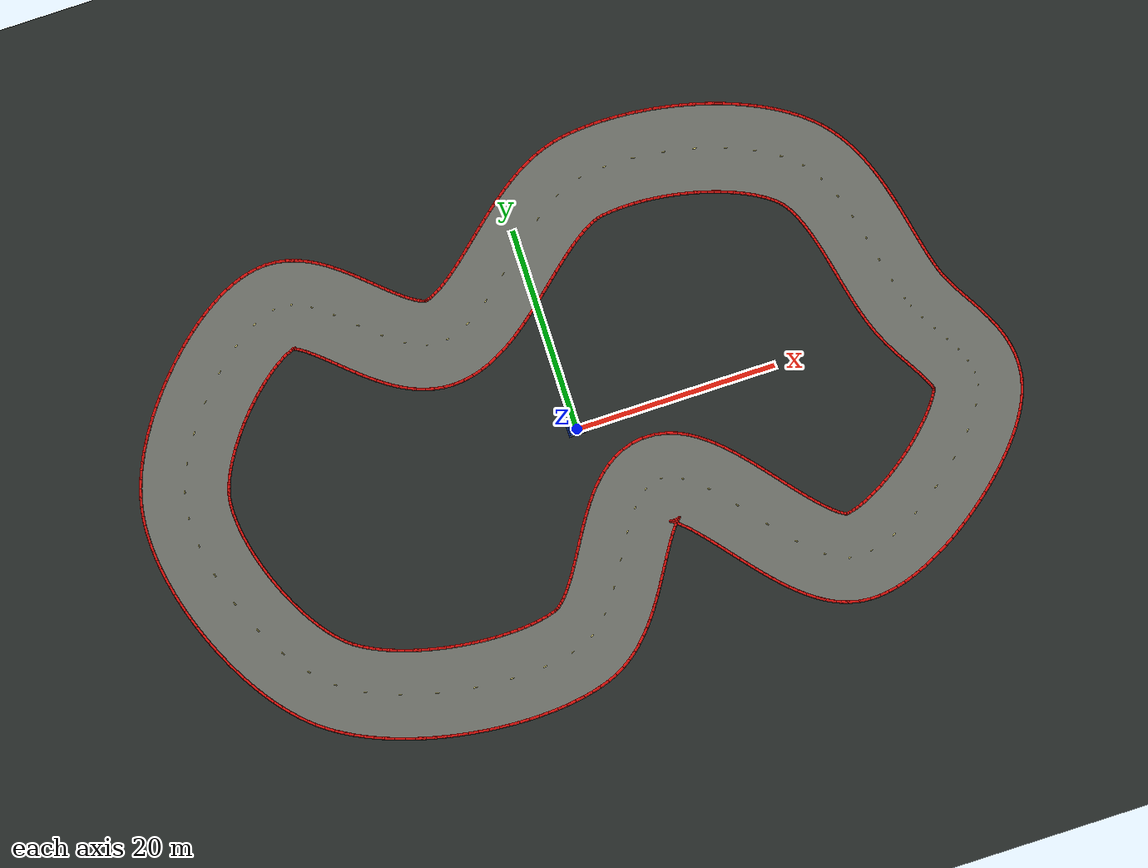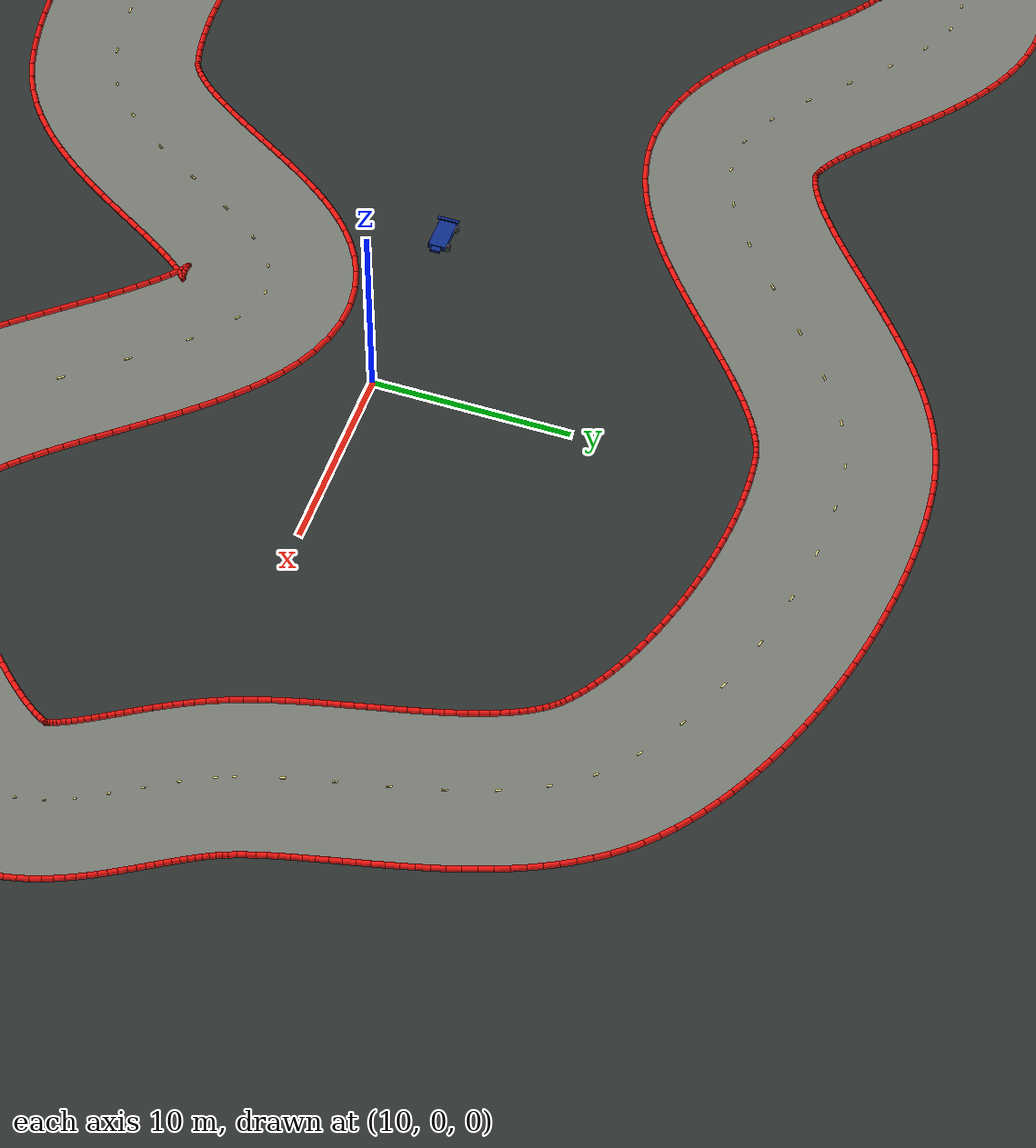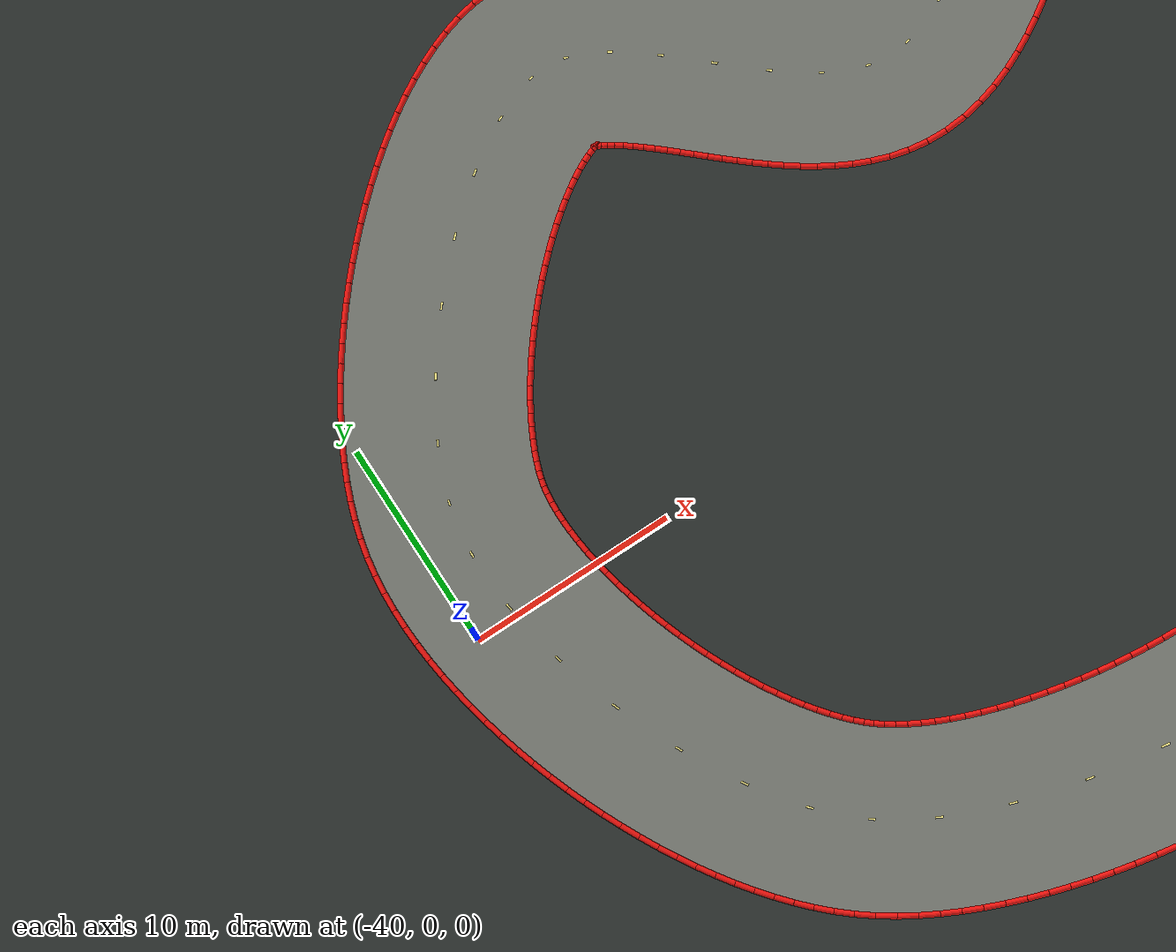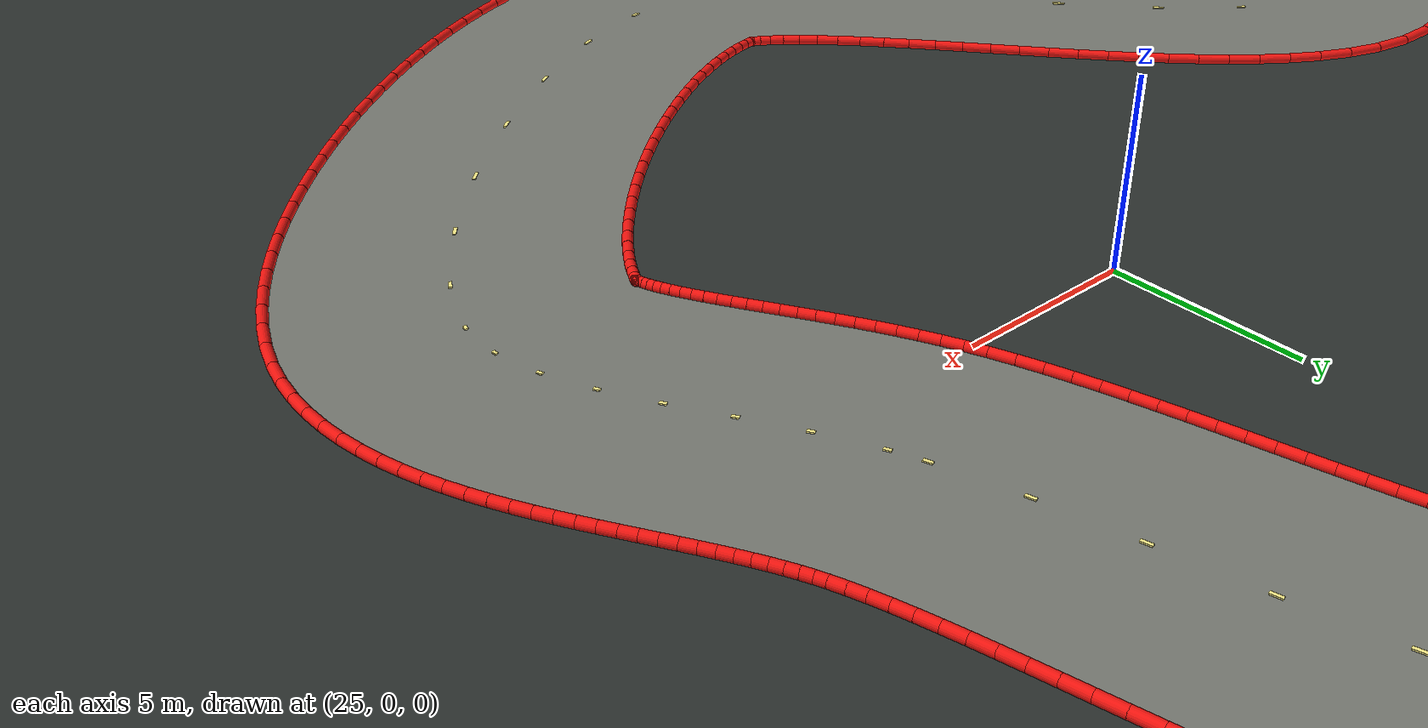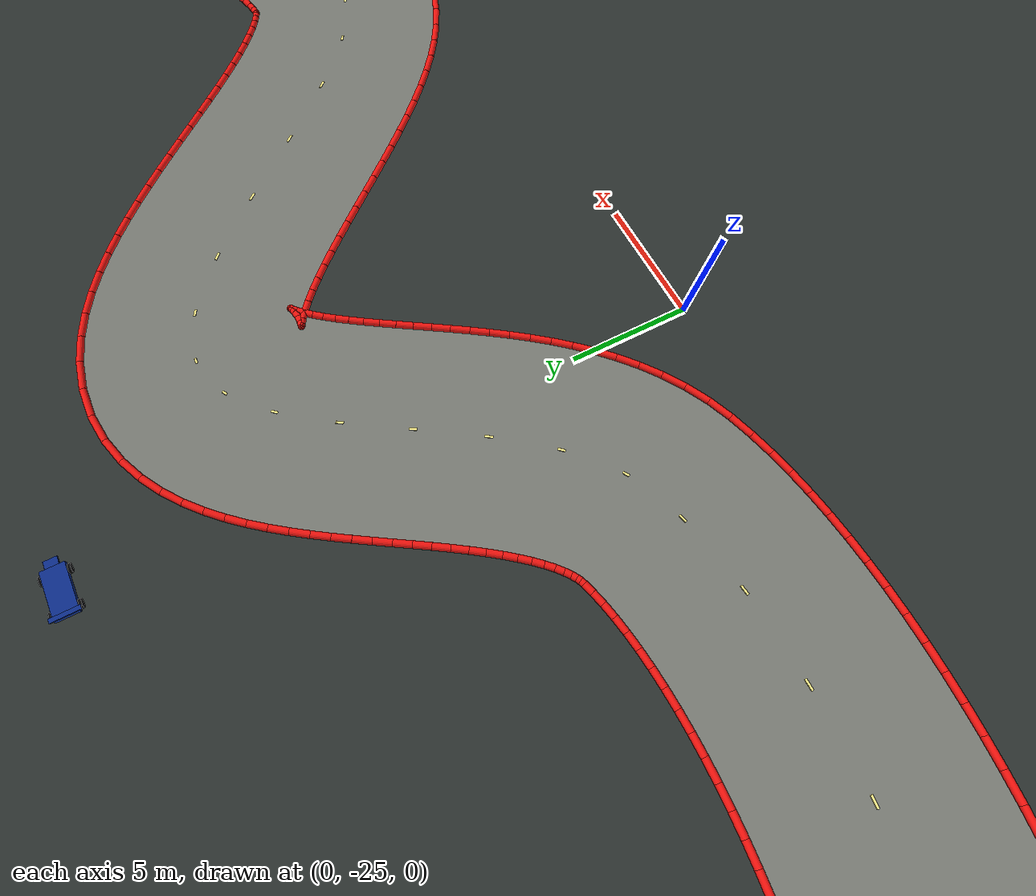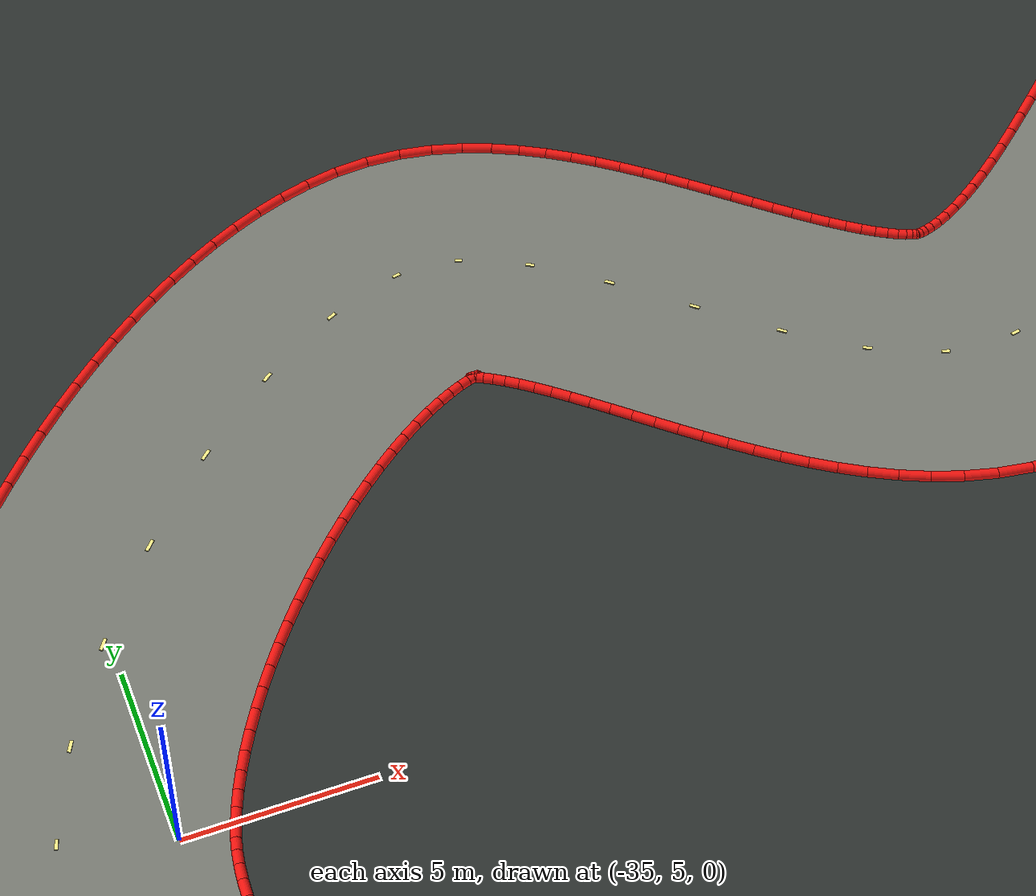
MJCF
<mujoco model="racesim_kidney_world">
  <compiler angle="degree" autolimits="true"/>
  <option timestep="0.02" gravity="0 0 -9.81"/>
  <visual>
    <global offwidth="1280" offheight="960"/>
    <headlight ambient="0.35 0.35 0.35" diffuse="0.8 0.8 0.8"/>
  </visual>

  <include file="car.xml"/>
  <include file="kidney_track.xml"/>

  <asset>
    <texture name="grid" type="2d" builtin="checker" width="512" height="512"
             rgb1="0.16 0.18 0.17" rgb2="0.20 0.22 0.21"/>
    <material name="ground" texture="grid" texrepeat="12 12" reflectance="0.05"/>
  </asset>

  <worldbody>
    <light name="sun" pos="0 0 30" dir="0 0 -1" diffuse="1.0 1.0 1.0" ambient="0.25 0.25 0.25"/>
    <geom name="ground" type="plane" size="90 90 0.1" material="ground"/>
    <camera name="topdown" pos="0 0 125" xyaxes="1 0 0 0 1 0" fovy="42"/>
    <camera name="follow" mode="trackcom" target="car" pos="-5 0 3" xyaxes="0 -1 0 0.5 0 0.866"/>
  </worldbody>
</mujoco>

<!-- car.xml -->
<mujoco model="simple_car">
  <default>
    <geom friction="1.2 0.02 0.001" density="600"/>
    <joint damping="0.1"/>
  </default>

  <asset>
    <material name="chassis_blue" rgba="0.05 0.18 0.55 1"/>
    <material name="wheel_dark" rgba="0.02 0.02 0.025 1"/>
  </asset>

  <worldbody>
    <body name="car" pos="0 0 0.28">
      <freejoint name="root"/>
      <geom name="chassis" type="box" size="0.9 0.45 0.12" material="chassis_blue"/>
      <geom name="nose" type="box" pos="0.75 0 0.02" size="0.45 0.25 0.06" material="chassis_blue"/>
      <geom name="rear_wing" type="box" pos="-0.85 0 0.22" size="0.08 0.55 0.04" material="chassis_blue"/>

      <body name="front_left_wheel" pos="0.65 0.48 -0.12">
        <joint name="front_left_spin" type="hinge" axis="0 1 0"/>
        <geom type="cylinder" size="0.18 0.08" euler="90 0 0" material="wheel_dark"/>
      </body>
      <body name="front_right_wheel" pos="0.65 -0.48 -0.12">
        <joint name="front_right_spin" type="hinge" axis="0 1 0"/>
        <geom type="cylinder" size="0.18 0.08" euler="90 0 0" material="wheel_dark"/>
      </body>
      <body name="rear_left_wheel" pos="-0.65 0.48 -0.12">
        <joint name="rear_left_spin" type="hinge" axis="0 1 0"/>
        <geom type="cylinder" size="0.18 0.08" euler="90 0 0" material="wheel_dark"/>
      </body>
      <body name="rear_right_wheel" pos="-0.65 -0.48 -0.12">
        <joint name="rear_right_spin" type="hinge" axis="0 1 0"/>
        <geom type="cylinder" size="0.18 0.08" euler="90 0 0" material="wheel_dark"/>
      </body>
    </body>
  </worldbody>
</mujoco>

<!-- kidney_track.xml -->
<mujoco model="kidney_track_visuals">
  <asset>
    <mesh name="track_surface_mesh" inertia="shell" vertex="30.03743 0.46361 0.02200 29.81446 1.06779 0.02200 29.61030 1.67497 0.02200 29.42246 2.28272 0.02200 29.24812 2.89078 0.02200 29.08482 3.49873 0.02200 28.93043 4.10597 0.02200 28.78306 4.71175 0.02200 28.64103 5.31514 0.02200 28.50281 5.91507 0.02200 28.36701 6.51031 0.02200 28.23238 7.09951 0.02200 28.09775 7.68118 0.02200 27.96206 8.25373 0.02200 27.82437 8.81546 0.02200 27.68383 9.36458 0.02200 27.53974 9.89918 0.02200 27.39150 10.41730 0.02200 27.23868 10.91689 0.02200 27.08103 11.39588 0.02200 26.91848 11.85216 0.02200 26.75122 12.28365 0.02200 26.57965 12.68835 0.02200 26.40446 13.06439 0.02200 26.22662 13.41020 0.02200 26.04730 13.72453 0.02200 25.86787 14.00672 0.02200 25.68973 14.25674 0.02200 25.51410 14.47545 0.02200 25.34175 14.66461 0.02200 25.15658 14.84129 0.02200 24.88577 15.06954 0.02200 24.56338 15.31601 0.02200 24.20288 15.56682 0.02200 23.80630 15.81909 0.02200 23.37586 16.07034 0.02200 22.91394 16.31846 0.02200 22.42296 16.56161 0.02200 21.90537 16.79824 0.02200 21.36363 17.02700 0.02200 20.80017 17.24673 0.02200 20.21742 17.45641 0.02200 19.61777 17.65514 0.02200 19.00360 17.84215 0.02200 18.37727 18.01674 0.02200 17.74111 18.17829 0.02200 17.09747 18.32625 0.02200 16.44867 18.46012 0.02200 15.79704 18.57947 0.02200 15.14493 18.68391 0.02200 14.49469 18.77309 0.02200 13.84871 18.84675 0.02200 13.20940 18.90464 0.02200 12.57922 18.94660 0.02200 11.96070 18.97253 0.02200 11.35639 18.98241 0.02200 10.76896 18.97633 0.02200 10.20114 18.95450 0.02200 9.65577 18.91728 0.02200 9.13580 18.86522 0.02200 8.69909 18.80789 0.02200 8.36752 18.74351 0.02200 8.05718 18.65341 0.02200 7.70603 18.52263 0.02200 7.31654 18.34787 0.02200 6.89257 18.12785 0.02200 6.43841 17.86300 0.02200 5.95824 17.55511 0.02200 5.45584 17.20695 0.02200 4.93444 16.82191 0.02200 4.39671 16.40383 0.02200 3.84477 15.95677 0.02200 3.28025 15.48492 0.02200 2.70431 14.99248 0.02200 2.11769 14.48365 0.02200 1.52073 13.96257 0.02200 0.91339 13.43332 0.02200 0.29520 12.89988 0.02200 -0.33474 12.36618 0.02200 -0.97779 11.83608 0.02200 -1.63591 11.31346 0.02200 -2.31169 10.80225 0.02200 -3.00845 10.30660 0.02200 -3.73042 9.83110 0.02200 -4.48272 9.38106 0.02200 -5.27131 8.96306 0.02200 -6.10274 8.58556 0.02200 -6.98328 8.25965 0.02200 -7.91756 7.99971 0.02200 -8.90624 7.82339 0.02200 -9.94071 7.75041 0.02200 -10.91163 7.79214 0.02200 -11.84404 7.93564 0.02200 -12.72015 8.16174 0.02200 -13.53786 8.45189 0.02200 -14.30011 8.79041 0.02200 -15.01247 9.16489 0.02200 -15.68135 9.56587 0.02200 -16.31290 9.98608 0.02200 -16.91253 10.41977 0.02200 -17.48473 10.86209 0.02200 -18.03308 11.30876 0.02200 -18.56029 11.75576 0.02200 -19.06835 12.19915 0.02200 -19.55853 12.63497 0.02200 -20.03153 13.05919 0.02200 -20.48740 13.46767 0.02200 -20.92562 13.85611 0.02200 -21.34500 14.22010 0.02200 -21.74363 14.55516 0.02200 -22.11872 14.85679 0.02200 -22.46647 15.12063 0.02200 -22.78188 15.34273 0.02200 -23.05856 15.51997 0.02200 -23.28878 15.65077 0.02200 -23.46373 15.73604 0.02200 -23.57461 15.78045 0.02200 -23.61486 15.79355 0.02200 -23.58385 15.78990 0.02200 -23.49123 15.78675 0.02200 -23.41226 15.79084 0.02200 -23.51124 15.76778 0.02200 -23.72400 15.70625 0.02200 -23.99869 15.60581 0.02200 -24.32486 15.46349 0.02200 -24.69321 15.27856 0.02200 -25.09561 15.05175 0.02200 -25.52508 14.78468 0.02200 -25.97557 14.47951 0.02200 -26.44179 14.13869 0.02200 -26.91904 13.76490 0.02200 -27.40313 13.36091 0.02200 -27.89021 12.92954 0.02200 -28.37673 12.47368 0.02200 -28.85938 11.99624 0.02200 -29.33500 11.50019 0.02200 -29.80061 10.98851 0.02200 -30.25331 10.46426 0.02200 -30.69031 9.93058 0.02200 -31.10888 9.39069 0.02200 -31.50639 8.84795 0.02200 -31.88025 8.30587 0.02200 -32.22795 7.76817 0.02200 -32.54708 7.23882 0.02200 -32.83536 6.72212 0.02200 -33.09068 6.22274 0.02200 -33.31122 5.74584 0.02200 -33.49554 5.29717 0.02200 -33.64286 4.88312 0.02200 -33.75330 4.51078 0.02200 -33.82997 4.17944 0.02200 -33.88949 3.81260 0.02200 -33.93270 3.39403 0.02200 -33.95627 2.92799 0.02200 -33.95783 2.41955 0.02200 -33.93584 1.87366 0.02200 -33.88942 1.29510 0.02200 -33.81817 0.68839 0.02200 -33.72209 0.05785 0.02200 -33.60143 -0.59243 0.02200 -33.45668 -1.25856 0.02200 -33.28850 -1.93680 0.02200 -33.09766 -2.62354 0.02200 -32.88508 -3.31530 0.02200 -32.65172 -4.00869 0.02200 -32.39868 -4.70038 0.02200 -32.12710 -5.38712 0.02200 -31.83823 -6.06568 0.02200 -31.53337 -6.73286 0.02200 -31.21395 -7.38550 0.02200 -30.88150 -8.02043 0.02200 -30.53766 -8.63449 0.02200 -30.18424 -9.22451 0.02200 -29.82323 -9.78733 0.02200 -29.45683 -10.31980 0.02200 -29.08753 -10.81878 0.02200 -28.71812 -11.28119 0.02200 -28.35179 -11.70405 0.02200 -27.99221 -12.08458 0.02200 -27.64355 -12.42029 0.02200 -27.31226 -12.70780 0.02200 -26.94912 -12.98682 0.02200 -26.53594 -13.26844 0.02200 -26.06833 -13.55365 0.02200 -25.55003 -13.83811 0.02200 -24.98507 -14.11826 0.02200 -24.37761 -14.39119 0.02200 -23.73179 -14.65453 0.02200 -23.05173 -14.90633 0.02200 -22.34149 -15.14497 0.02200 -21.60507 -15.36912 0.02200 -20.84639 -15.57765 0.02200 -20.06931 -15.76960 0.02200 -19.27766 -15.94416 0.02200 -18.47522 -16.10065 0.02200 -17.66575 -16.23846 0.02200 -16.85300 -16.35710 0.02200 -16.04074 -16.45614 0.02200 -15.23276 -16.53524 0.02200 -14.43289 -16.59413 0.02200 -13.64501 -16.63263 0.02200 -12.87311 -16.65068 0.02200 -12.12128 -16.64832 0.02200 -11.39374 -16.62575 0.02200 -10.69490 -16.58335 0.02200 -10.02937 -16.52178 0.02200 -9.40202 -16.44202 0.02200 -8.81797 -16.34552 0.02200 -8.28269 -16.23435 0.02200 -7.80193 -16.11144 0.02200 -7.43269 -15.99876 0.02200 -7.28144 -15.93963 0.02200 -7.15203 -15.86935 0.02200 -6.98168 -15.75566 0.02200 -6.77330 -15.59090 0.02200 -6.53246 -15.37127 0.02200 -6.26543 -15.09635 0.02200 -5.97807 -14.76814 0.02200 -5.67529 -14.39022 0.02200 -5.36090 -13.96709 0.02200 -5.03771 -13.50369 0.02200 -4.70757 -13.00512 0.02200 -4.37159 -12.47641 0.02200 -4.03019 -11.92247 0.02200 -3.68322 -11.34795 0.02200 -3.33001 -10.75725 0.02200 -2.96937 -10.15445 0.02200 -2.59959 -9.54331 0.02200 -2.21836 -8.92722 0.02200 -1.82262 -8.30921 0.02200 -1.40841 -7.69193 0.02200 -0.97057 -7.07773 0.02200 -0.50235 -6.46885 0.02200 0.00504 -5.86775 0.02200 0.56292 -5.27794 0.02200 1.18539 -4.70535 0.02200 1.88878 -4.16058 0.02200 2.68920 -3.66189 0.02200 3.59712 -3.23753 0.02200 4.60892 -2.92456 0.02200 5.72414 -2.75896 0.02200 6.93084 -2.78342 0.02200 8.07908 -3.00043 0.02200 9.10800 -3.35550 0.02200 10.02434 -3.80122 0.02200 10.84821 -4.30658 0.02200 11.60117 -4.85366 0.02200 12.30133 -5.43231 0.02200 12.96251 -6.03633 0.02200 13.59469 -6.66121 0.02200 14.20497 -7.30293 0.02200 14.79826 -7.95743 0.02200 15.37793 -8.62042 0.02200 15.94617 -9.28727 0.02200 16.50428 -9.95296 0.02200 17.05289 -10.61217 0.02200 17.59199 -11.25921 0.02200 18.12103 -11.88810 0.02200 18.63888 -12.49254 0.02200 19.14375 -13.06591 0.02200 19.63309 -13.60134 0.02200 20.10339 -14.09170 0.02200 20.54985 -14.52971 0.02200 20.96602 -14.90819 0.02200 21.34333 -15.22048 0.02200 21.67055 -15.46127 0.02200 21.93360 -15.62817 0.02200 22.11623 -15.72406 0.02200 22.20293 -15.76029 0.02200 22.18548 -15.75895 0.02200 22.14810 -15.75258 0.02200 22.23741 -15.74538 0.02200 22.46625 -15.71788 0.02200 22.76742 -15.65937 0.02200 23.13004 -15.56477 0.02200 23.54395 -15.43185 0.02200 24.00001 -15.26033 0.02200 24.49021 -15.05115 0.02200 25.00748 -14.80603 0.02200 25.54556 -14.52718 0.02200 26.09881 -14.21713 0.02200 26.66213 -13.87861 0.02200 27.23079 -13.51448 0.02200 27.80039 -13.12769 0.02200 28.36675 -12.72127 0.02200 28.92584 -12.29834 0.02200 29.47380 -11.86208 0.02200 30.00683 -11.41581 0.02200 30.52119 -10.96294 0.02200 31.01315 -10.50708 0.02200 31.47899 -10.05204 0.02200 31.91497 -9.60196 0.02200 32.31730 -9.16138 0.02200 32.68213 -8.73540 0.02200 33.00559 -8.32992 0.02200 33.28385 -7.95191 0.02200 33.51321 -7.60989 0.02200 33.69050 -7.31451 0.02200 33.81367 -7.07937 0.02200 33.88319 -6.92198 0.02200 33.91229 -6.83677 0.02200 33.90080 -6.88229 0.02200 33.89606 -6.91280 0.02200 33.89432 -6.93452 0.02200 33.89400 -6.93970 0.02200 33.89213 -6.92238 0.02200 33.88500 -6.87868 0.02200 33.86891 -6.80665 0.02200 33.84062 -6.70588 0.02200 33.79757 -6.57712 0.02200 33.73802 -6.42178 0.02200 33.66098 -6.24164 0.02200 33.56609 -6.03858 0.02200 33.45353 -5.81442 0.02200 33.32391 -5.57080 0.02200 33.17811 -5.30915 0.02200 33.01726 -5.03066 0.02200 32.84263 -4.73629 0.02200 32.65561 -4.42674 0.02200 32.45768 -4.10253 0.02200 32.25035 -3.76394 0.02200 32.03519 -3.41107 0.02200 31.81384 -3.04384 0.02200 31.58794 -2.66202 0.02200 31.35922 -2.26522 0.02200 31.12948 -1.85291 0.02200 30.90060 -1.42443 0.02200 30.67458 -0.97904 0.02200 30.45358 -0.51592 0.02200 30.23992 -0.03422 0.02200 37.96257 3.53639 0.02200 37.83143 3.89238 0.02200 37.70023 4.28322 0.02200 37.56910 4.70807 0.02200 37.43853 5.16392 0.02200 37.30862 5.64793 0.02200 37.17916 6.15741 0.02200 37.04968 6.68986 0.02200 36.91953 7.24294 0.02200 36.78788 7.81445 0.02200 36.65376 8.40235 0.02200 36.51611 9.00473 0.02200 36.37372 9.61980 0.02200 36.22531 10.24588 0.02200 36.06948 10.88141 0.02200 35.90472 11.52493 0.02200 35.72939 12.17504 0.02200 35.54175 12.83047 0.02200 35.33987 13.48998 0.02200 35.12166 14.15238 0.02200 34.88483 14.81651 0.02200 34.62686 15.48119 0.02200 34.34499 16.14515 0.02200 34.03618 16.80697 0.02200 33.69714 17.46498 0.02200 33.32431 18.11715 0.02200 32.91400 18.76087 0.02200 32.46246 19.39290 0.02200 31.96611 20.00912 0.02200 31.42185 20.60451 0.02200 30.84342 21.15871 0.02200 30.21581 21.69077 0.02200 29.57612 22.18059 0.02200 28.91449 22.64147 0.02200 28.23250 23.07572 0.02200 27.53152 23.48523 0.02200 26.81280 23.87153 0.02200 26.07751 24.23587 0.02200 25.32681 24.57923 0.02200 24.56186 24.90237 0.02200 23.78382 25.20587 0.02200 22.99387 25.49017 0.02200 22.19323 25.75558 0.02200 21.38313 26.00229 0.02200 20.56482 26.23043 0.02200 19.73956 26.44003 0.02200 18.90862 26.63105 0.02200 18.07330 26.80342 0.02200 17.23485 26.95698 0.02200 16.39454 27.09155 0.02200 15.55363 27.20687 0.02200 14.71333 27.30266 0.02200 13.87484 27.37855 0.02200 13.03931 27.43414 0.02200 12.20782 27.46893 0.02200 11.38141 27.48237 0.02200 10.56104 27.47379 0.02200 9.74756 27.44239 0.02200 8.94177 27.38724 0.02200 8.14431 27.30720 0.02200 7.30091 27.19211 0.02200 6.36030 27.00311 0.02200 5.40370 26.72863 0.02200 4.49312 26.39201 0.02200 3.62605 26.00491 0.02200 2.79862 25.57698 0.02200 2.00650 25.11615 0.02200 1.24549 24.62901 0.02200 0.51178 24.12115 0.02200 -0.19789 23.59754 0.02200 -0.88622 23.06271 0.02200 -1.55535 22.52098 0.02200 -2.20693 21.97652 0.02200 -2.84217 21.43349 0.02200 -3.46182 20.89606 0.02200 -4.06627 20.36846 0.02200 -4.65547 19.85498 0.02200 -5.22901 19.36000 0.02200 -5.78600 18.88796 0.02200 -6.32511 18.44337 0.02200 -6.84442 18.03071 0.02200 -7.34136 17.65443 0.02200 -7.81262 17.31873 0.02200 -8.25403 17.02741 0.02200 -8.66048 16.78351 0.02200 -9.02603 16.58881 0.02200 -9.34417 16.44324 0.02200 -9.60865 16.34405 0.02200 -9.81488 16.28525 0.02200 -9.96221 16.25754 0.02200 -10.05929 16.24959 0.02200 -10.07379 16.25075 0.02200 -10.12294 16.25957 0.02200 -10.22456 16.28713 0.02200 -10.38079 16.34385 0.02200 -10.58870 16.43733 0.02200 -10.84276 16.57187 0.02200 -11.13659 16.74884 0.02200 -11.46406 16.96740 0.02200 -11.81980 17.22521 0.02200 -12.19933 17.51901 0.02200 -12.59912 17.84498 0.02200 -13.01646 18.19905 0.02200 -13.44942 18.57705 0.02200 -13.89673 18.97484 0.02200 -14.35774 19.38835 0.02200 -14.83242 19.81363 0.02200 -15.32132 20.24687 0.02200 -15.82565 20.68437 0.02200 -16.34736 21.12253 0.02200 -16.88926 21.55774 0.02200 -17.45518 21.98626 0.02200 -18.05016 22.40395 0.02200 -18.68059 22.80580 0.02200 -19.35425 23.18532 0.02200 -20.07998 23.53349 0.02200 -20.86660 23.83754 0.02200 -21.72070 24.07981 0.02200 -22.64294 24.23766 0.02200 -23.62370 24.28572 0.02200 -24.58774 24.20916 0.02200 -25.50401 24.03088 0.02200 -26.34078 23.79343 0.02200 -27.14563 23.50181 0.02200 -27.92471 23.16356 0.02200 -28.68306 22.78396 0.02200 -29.42453 22.36684 0.02200 -30.15181 21.91514 0.02200 -30.86669 21.43126 0.02200 -31.57018 20.91731 0.02200 -32.26268 20.37517 0.02200 -32.94412 19.80664 0.02200 -33.61407 19.21344 0.02200 -34.27181 18.59725 0.02200 -34.91635 17.95972 0.02200 -35.54659 17.30244 0.02200 -36.16122 16.62699 0.02200 -36.75888 15.93487 0.02200 -37.33806 15.22750 0.02200 -37.89721 14.50621 0.02200 -38.43471 13.77221 0.02200 -38.94885 13.02655 0.02200 -39.43787 12.27006 0.02200 -39.89990 11.50334 0.02200 -40.33294 10.72666 0.02200 -40.73481 9.93989 0.02200 -41.10308 9.14243 0.02200 -41.43489 8.33310 0.02200 -41.72675 7.51007 0.02200 -41.97426 6.67080 0.02200 -42.17003 5.82056 0.02200 -42.31463 4.93824 0.02200 -42.40726 4.05113 0.02200 -42.45311 3.15990 0.02200 -42.45642 2.26444 0.02200 -42.42059 1.36472 0.02200 -42.34839 0.46091 0.02200 -42.24206 -0.44657 0.02200 -42.10349 -1.35709 0.02200 -41.93428 -2.26979 0.02200 -41.73581 -3.18365 0.02200 -41.50930 -4.09745 0.02200 -41.25582 -5.00985 0.02200 -40.97634 -5.91940 0.02200 -40.67176 -6.82455 0.02200 -40.34284 -7.72367 0.02200 -39.99032 -8.61510 0.02200 -39.61481 -9.49710 0.02200 -39.21688 -10.36793 0.02200 -38.79695 -11.22583 0.02200 -38.35539 -12.06901 0.02200 -37.89239 -12.89569 0.02200 -37.40803 -13.70411 0.02200 -36.90219 -14.49247 0.02200 -36.37451 -15.25900 0.02200 -35.82440 -16.00188 0.02200 -35.25091 -16.71926 0.02200 -34.65273 -17.40916 0.02200 -34.02806 -18.06944 0.02200 -33.37459 -18.69764 0.02200 -32.68774 -19.29220 0.02200 -31.93734 -19.86924 0.02200 -31.14804 -20.40837 0.02200 -30.33018 -20.90801 0.02200 -29.48594 -21.37194 0.02200 -28.61722 -21.80315 0.02200 -27.72581 -22.20397 0.02200 -26.81350 -22.57622 0.02200 -25.88210 -22.92126 0.02200 -24.93347 -23.24014 0.02200 -23.96957 -23.53363 0.02200 -22.99241 -23.80228 0.02200 -22.00404 -24.04648 0.02200 -21.00660 -24.26647 0.02200 -20.00221 -24.46236 0.02200 -18.99307 -24.63419 0.02200 -17.98135 -24.78187 0.02200 -16.96922 -24.90528 0.02200 -15.95882 -25.00417 0.02200 -14.95226 -25.07824 0.02200 -13.95159 -25.12710 0.02200 -12.95875 -25.15025 0.02200 -11.97559 -25.14707 0.02200 -11.00382 -25.11680 0.02200 -10.04497 -25.05847 0.02200 -9.10036 -24.97086 0.02200 -8.17106 -24.85242 0.02200 -7.25787 -24.70113 0.02200 -6.36127 -24.51434 0.02200 -5.48144 -24.28856 0.02200 -4.56731 -24.00124 0.02200 -3.67876 -23.63837 0.02200 -2.80670 -23.17469 0.02200 -2.01158 -22.65117 0.02200 -1.28814 -22.08420 0.02200 -0.62848 -21.48626 0.02200 -0.02401 -20.86650 0.02200 0.53348 -20.23163 0.02200 1.05122 -19.58677 0.02200 1.53538 -18.93613 0.02200 1.99107 -18.28347 0.02200 2.42250 -17.63243 0.02200 2.83311 -16.98665 0.02200 3.22566 -16.34997 0.02200 3.60232 -15.72641 0.02200 3.96477 -15.12031 0.02200 4.31414 -14.53628 0.02200 4.65107 -13.97928 0.02200 4.97557 -13.45462 0.02200 5.28693 -12.96799 0.02200 5.58352 -12.52545 0.02200 5.86250 -12.13334 0.02200 6.11947 -11.79816 0.02200 6.34797 -11.52613 0.02200 6.53901 -11.32247 0.02200 6.68084 -11.18995 0.02200 6.75946 -11.12668 0.02200 6.76108 -11.12311 0.02200 6.67758 -11.15970 0.02200 6.51491 -11.20811 0.02200 6.27586 -11.24104 0.02200 6.03705 -11.23629 0.02200 5.86955 -11.20823 0.02200 5.83360 -11.19950 0.02200 5.92179 -11.24561 0.02200 6.11336 -11.36570 0.02200 6.38612 -11.56583 0.02200 6.72129 -11.84426 0.02200 7.10443 -12.19530 0.02200 7.52487 -12.61162 0.02200 7.97490 -13.08534 0.02200 8.44895 -13.60864 0.02200 8.94300 -14.17395 0.02200 9.45421 -14.77403 0.02200 9.98063 -15.40199 0.02200 10.52099 -16.05131 0.02200 11.07464 -16.71579 0.02200 11.64150 -17.38953 0.02200 12.22205 -18.06697 0.02200 12.81741 -18.74284 0.02200 13.42949 -19.41214 0.02200 14.06117 -20.07012 0.02200 14.71658 -20.71219 0.02200 15.40153 -21.33364 0.02200 16.12395 -21.92928 0.02200 16.89441 -22.49253 0.02200 17.72635 -23.01390 0.02200 18.63536 -23.47864 0.02200 19.63632 -23.86353 0.02200 20.73679 -24.13459 0.02200 21.85190 -24.24742 0.02200 22.84839 -24.22339 0.02200 23.75586 -24.11948 0.02200 24.63593 -23.95146 0.02200 25.49394 -23.72945 0.02200 26.33451 -23.46072 0.02200 27.16121 -23.15063 0.02200 27.97652 -22.80329 0.02200 28.78194 -22.42203 0.02200 29.57819 -22.00968 0.02200 30.36534 -21.56878 0.02200 31.14296 -21.10164 0.02200 31.91021 -20.61047 0.02200 32.66595 -20.09736 0.02200 33.40882 -19.56433 0.02200 34.13727 -19.01332 0.02200 34.84962 -18.44620 0.02200 35.54413 -17.86471 0.02200 36.21898 -17.27049 0.02200 36.87234 -16.66499 0.02200 37.50239 -16.04944 0.02200 38.10731 -15.42476 0.02200 38.68535 -14.79147 0.02200 39.23479 -14.14951 0.02200 39.75396 -13.49804 0.02200 40.24115 -12.83514 0.02200 40.69448 -12.15734 0.02200 41.11159 -11.45906 0.02200 41.48897 -10.73174 0.02200 41.82061 -9.96292 0.02200 42.08771 -9.16323 0.02200 42.24831 -8.48510 0.02200 42.34724 -7.82249 0.02200 42.39108 -7.16887 0.02200 42.38421 -6.53171 0.02200 42.33242 -5.91663 0.02200 42.24221 -5.32723 0.02200 42.12011 -4.76514 0.02200 41.97218 -4.23046 0.02200 41.80376 -3.72215 0.02200 41.61943 -3.23847 0.02200 41.42298 -2.77735 0.02200 41.21757 -2.33659 0.02200 41.00584 -1.91407 0.02200 40.79000 -1.50785 0.02200 40.57197 -1.11619 0.02200 40.35343 -0.73758 0.02200 40.13593 -0.37077 0.02200 39.92088 -0.01473 0.02200 39.70963 0.33134 0.02200 39.50346 0.66803 0.02200 39.30361 0.99577 0.02200 39.11127 1.31477 0.02200 38.92759 1.62511 0.02200 38.75367 1.92670 0.02200 38.59051 2.21932 0.02200 38.43904 2.50263 0.02200 38.30008 2.77619 0.02200 38.17427 3.03948 0.02200 38.06210 3.29196 0.02200" face="0 331 1 0 330 331 1 332 2 1 331 332 2 333 3 2 332 333 3 334 4 3 333 334 4 335 5 4 334 335 5 336 6 5 335 336 6 337 7 6 336 337 7 338 8 7 337 338 8 339 9 8 338 339 9 340 10 9 339 340 10 341 11 10 340 341 11 342 12 11 341 342 12 343 13 12 342 343 13 344 14 13 343 344 14 345 15 14 344 345 15 346 16 15 345 346 16 347 17 16 346 347 17 348 18 17 347 348 18 349 19 18 348 349 19 350 20 19 349 350 20 351 21 20 350 351 21 352 22 21 351 352 22 353 23 22 352 353 23 354 24 23 353 354 24 355 25 24 354 355 25 356 26 25 355 356 26 357 27 26 356 357 27 358 28 27 357 358 28 359 29 28 358 359 29 360 30 29 359 360 30 361 31 30 360 361 31 362 32 31 361 362 32 363 33 32 362 363 33 364 34 33 363 364 34 365 35 34 364 365 35 366 36 35 365 366 36 367 37 36 366 367 37 368 38 37 367 368 38 369 39 38 368 369 39 370 40 39 369 370 40 371 41 40 370 371 41 372 42 41 371 372 42 373 43 42 372 373 43 374 44 43 373 374 44 375 45 44 374 375 45 376 46 45 375 376 46 377 47 46 376 377 47 378 48 47 377 378 48 379 49 48 378 379 49 380 50 49 379 380 50 381 51 50 380 381 51 382 52 51 381 382 52 383 53 52 382 383 53 384 54 53 383 384 54 385 55 54 384 385 55 386 56 55 385 386 56 387 57 56 386 387 57 388 58 57 387 388 58 389 59 58 388 389 59 390 60 59 389 390 60 391 61 60 390 391 61 392 62 61 391 392 62 393 63 62 392 393 63 394 64 63 393 394 64 395 65 64 394 395 65 396 66 65 395 396 66 397 67 66 396 397 67 398 68 67 397 398 68 399 69 68 398 399 69 400 70 69 399 400 70 401 71 70 400 401 71 402 72 71 401 402 72 403 73 72 402 403 73 404 74 73 403 404 74 405 75 74 404 405 75 406 76 75 405 406 76 407 77 76 406 407 77 408 78 77 407 408 78 409 79 78 408 409 79 410 80 79 409 410 80 411 81 80 410 411 81 412 82 81 411 412 82 413 83 82 412 413 83 414 84 83 413 414 84 415 85 84 414 415 85 416 86 85 415 416 86 417 87 86 416 417 87 418 88 87 417 418 88 419 89 88 418 419 89 420 90 89 419 420 90 421 91 90 420 421 91 422 92 91 421 422 92 423 93 92 422 423 93 424 94 93 423 424 94 425 95 94 424 425 95 426 96 95 425 426 96 427 97 96 426 427 97 428 98 97 427 428 98 429 99 98 428 429 99 430 100 99 429 430 100 431 101 100 430 431 101 432 102 101 431 432 102 433 103 102 432 433 103 434 104 103 433 434 104 435 105 104 434 435 105 436 106 105 435 436 106 437 107 106 436 437 107 438 108 107 437 438 108 439 109 108 438 439 109 440 110 109 439 440 110 441 111 110 440 441 111 442 112 111 441 442 112 443 113 112 442 443 113 444 114 113 443 444 114 445 115 114 444 445 115 446 116 115 445 446 116 447 117 116 446 447 117 448 118 117 447 448 118 449 119 118 448 449 119 450 120 119 449 450 120 451 121 120 450 451 121 452 122 121 451 452 122 453 123 122 452 453 123 454 124 123 453 454 124 455 125 124 454 455 125 456 126 125 455 456 126 457 127 126 456 457 127 458 128 127 457 458 128 459 129 128 458 459 129 460 130 129 459 460 130 461 131 130 460 461 131 462 132 131 461 462 132 463 133 132 462 463 133 464 134 133 463 464 134 465 135 134 464 465 135 466 136 135 465 466 136 467 137 136 466 467 137 468 138 137 467 468 138 469 139 138 468 469 139 470 140 139 469 470 140 471 141 140 470 471 141 472 142 141 471 472 142 473 143 142 472 473 143 474 144 143 473 474 144 475 145 144 474 475 145 476 146 145 475 476 146 477 147 146 476 477 147 478 148 147 477 478 148 479 149 148 478 479 149 480 150 149 479 480 150 481 151 150 480 481 151 482 152 151 481 482 152 483 153 152 482 483 153 484 154 153 483 484 154 485 155 154 484 485 155 486 156 155 485 486 156 487 157 156 486 487 157 488 158 157 487 488 158 489 159 158 488 489 159 490 160 159 489 490 160 491 161 160 490 491 161 492 162 161 491 492 162 493 163 162 492 493 163 494 164 163 493 494 164 495 165 164 494 495 165 496 166 165 495 496 166 497 167 166 496 497 167 498 168 167 497 498 168 499 169 168 498 499 169 500 170 169 499 500 170 501 171 170 500 501 171 502 172 171 501 502 172 503 173 172 502 503 173 504 174 173 503 504 174 505 175 174 504 505 175 506 176 175 505 506 176 507 177 176 506 507 177 508 178 177 507 508 178 509 179 178 508 509 179 510 180 179 509 510 180 511 181 180 510 511 181 512 182 181 511 512 182 513 183 182 512 513 183 514 184 183 513 514 184 515 185 184 514 515 185 516 186 185 515 516 186 517 187 186 516 517 187 518 188 187 517 518 188 519 189 188 518 519 189 520 190 189 519 520 190 521 191 190 520 521 191 522 192 191 521 522 192 523 193 192 522 523 193 524 194 193 523 524 194 525 195 194 524 525 195 526 196 195 525 526 196 527 197 196 526 527 197 528 198 197 527 528 198 529 199 198 528 529 199 530 200 199 529 530 200 531 201 200 530 531 201 532 202 201 531 532 202 533 203 202 532 533 203 534 204 203 533 534 204 535 205 204 534 535 205 536 206 205 535 536 206 537 207 206 536 537 207 538 208 207 537 538 208 539 209 208 538 539 209 540 210 209 539 540 210 541 211 210 540 541 211 542 212 211 541 542 212 543 213 212 542 543 213 544 214 213 543 544 214 545 215 214 544 545 215 546 216 215 545 546 216 547 217 216 546 547 217 548 218 217 547 548 218 549 219 218 548 549 219 550 220 219 549 550 220 551 221 220 550 551 221 552 222 221 551 552 222 553 223 222 552 553 223 554 224 223 553 554 224 555 225 224 554 555 225 556 226 225 555 556 226 557 227 226 556 557 227 558 228 227 557 558 228 559 229 228 558 559 229 560 230 229 559 560 230 561 231 230 560 561 231 562 232 231 561 562 232 563 233 232 562 563 233 564 234 233 563 564 234 565 235 234 564 565 235 566 236 235 565 566 236 567 237 236 566 567 237 568 238 237 567 568 238 569 239 238 568 569 239 570 240 239 569 570 240 571 241 240 570 571 241 572 242 241 571 572 242 573 243 242 572 573 243 574 244 243 573 574 244 575 245 244 574 575 245 576 246 245 575 576 246 577 247 246 576 577 247 578 248 247 577 578 248 579 249 248 578 579 249 580 250 249 579 580 250 581 251 250 580 581 251 582 252 251 581 582 252 583 253 252 582 583 253 584 254 253 583 584 254 585 255 254 584 585 255 586 256 255 585 586 256 587 257 256 586 587 257 588 258 257 587 588 258 589 259 258 588 589 259 590 260 259 589 590 260 591 261 260 590 591 261 592 262 261 591 592 262 593 263 262 592 593 263 594 264 263 593 594 264 595 265 264 594 595 265 596 266 265 595 596 266 597 267 266 596 597 267 598 268 267 597 598 268 599 269 268 598 599 269 600 270 269 599 600 270 601 271 270 600 601 271 602 272 271 601 602 272 603 273 272 602 603 273 604 274 273 603 604 274 605 275 274 604 605 275 606 276 275 605 606 276 607 277 276 606 607 277 608 278 277 607 608 278 609 279 278 608 609 279 610 280 279 609 610 280 611 281 280 610 611 281 612 282 281 611 612 282 613 283 282 612 613 283 614 284 283 613 614 284 615 285 284 614 615 285 616 286 285 615 616 286 617 287 286 616 617 287 618 288 287 617 618 288 619 289 288 618 619 289 620 290 289 619 620 290 621 291 290 620 621 291 622 292 291 621 622 292 623 293 292 622 623 293 624 294 293 623 624 294 625 295 294 624 625 295 626 296 295 625 626 296 627 297 296 626 627 297 628 298 297 627 628 298 629 299 298 628 629 299 630 300 299 629 630 300 631 301 300 630 631 301 632 302 301 631 632 302 633 303 302 632 633 303 634 304 303 633 634 304 635 305 304 634 635 305 636 306 305 635 636 306 637 307 306 636 637 307 638 308 307 637 638 308 639 309 308 638 639 309 640 310 309 639 640 310 641 311 310 640 641 311 642 312 311 641 642 312 643 313 312 642 643 313 644 314 313 643 644 314 645 315 314 644 645 315 646 316 315 645 646 316 647 317 316 646 647 317 648 318 317 647 648 318 649 319 318 648 649 319 650 320 319 649 650 320 651 321 320 650 651 321 652 322 321 651 652 322 653 323 322 652 653 323 654 324 323 653 654 324 655 325 324 654 655 325 656 326 325 655 656 326 657 327 326 656 657 327 658 328 327 657 658 328 659 329 328 658 659 329 330 0 329 659 330"/>
    <material name="track_asphalt" rgba="0.48 0.49 0.46 1" emission="0.08"/>
    <material name="track_boundary" rgba="0.95 0.08 0.06 1" emission="0.05"/>
    <material name="track_centerline" rgba="1.0 0.95 0.55 1" emission="0.15"/>
  </asset>
  <worldbody>
    <geom name="track_surface" type="mesh" mesh="track_surface_mesh" material="track_asphalt" contype="0" conaffinity="0"/>
    <geom name="track_left_boundary_000" type="capsule" fromto="30.03743 0.46361 0.09 29.81446 1.06779 0.09" size="0.14" material="track_boundary" contype="0" conaffinity="0"/>
    <geom name="track_left_boundary_001" type="capsule" fromto="29.81446 1.06779 0.09 29.61030 1.67497 0.09" size="0.14" material="track_boundary" contype="0" conaffinity="0"/>
    <geom name="track_left_boundary_002" type="capsule" fromto="29.61030 1.67497 0.09 29.42246 2.28272 0.09" size="0.14" material="track_boundary" contype="0" conaffinity="0"/>
    <geom name="track_left_boundary_003" type="capsule" fromto="29.42246 2.28272 0.09 29.24812 2.89078 0.09" size="0.14" material="track_boundary" contype="0" conaffinity="0"/>
    <geom name="track_left_boundary_004" type="capsule" fromto="29.24812 2.89078 0.09 29.08482 3.49873 0.09" size="0.14" material="track_boundary" contype="0" conaffinity="0"/>
    <geom name="track_left_boundary_005" type="capsule" fromto="29.08482 3.49873 0.09 28.93043 4.10597 0.09" size="0.14" material="track_boundary" contype="0" conaffinity="0"/>
    <geom name="track_left_boundary_006" type="capsule" fromto="28.93043 4.10597 0.09 28.78306 4.71175 0.09" size="0.14" material="track_boundary" contype="0" conaffinity="0"/>
    <geom name="track_left_boundary_007" type="capsule" fromto="28.78306 4.71175 0.09 28.64103 5.31514 0.09" size="0.14" material="track_boundary" contype="0" conaffinity="0"/>
    <geom name="track_left_boundary_008" type="capsule" fromto="28.64103 5.31514 0.09 28.50281 5.91507 0.09" size="0.14" material="track_boundary" contype="0" conaffinity="0"/>
    <geom name="track_left_boundary_009" type="capsule" fromto="28.50281 5.91507 0.09 28.36701 6.51031 0.09" size="0.14" material="track_boundary" contype="0" conaffinity="0"/>
    <geom name="track_left_boundary_010" type="capsule" fromto="28.36701 6.51031 0.09 28.23238 7.09951 0.09" size="0.14" material="track_boundary" contype="0" conaffinity="0"/>
    <geom name="track_left_boundary_011" type="capsule" fromto="28.23238 7.09951 0.09 28.09775 7.68118 0.09" size="0.14" material="track_boundary" contype="0" conaffinity="0"/>
    <geom name="track_left_boundary_012" type="capsule" fromto="28.09775 7.68118 0.09 27.96206 8.25373 0.09" size="0.14" material="track_boundary" contype="0" conaffinity="0"/>
    <geom name="track_left_boundary_013" type="capsule" fromto="27.96206 8.25373 0.09 27.82437 8.81546 0.09" size="0.14" material="track_boundary" contype="0" conaffinity="0"/>
    <geom name="track_left_boundary_014" type="capsule" fromto="27.82437 8.81546 0.09 27.68383 9.36458 0.09" size="0.14" material="track_boundary" contype="0" conaffinity="0"/>
    <geom name="track_left_boundary_015" type="capsule" fromto="27.68383 9.36458 0.09 27.53974 9.89918 0.09" size="0.14" material="track_boundary" contype="0" conaffinity="0"/>
    <geom name="track_left_boundary_016" type="capsule" fromto="27.53974 9.89918 0.09 27.39150 10.41730 0.09" size="0.14" material="track_boundary" contype="0" conaffinity="0"/>
    <geom name="track_left_boundary_017" type="capsule" fromto="27.39150 10.41730 0.09 27.23868 10.91689 0.09" size="0.14" material="track_boundary" contype="0" conaffinity="0"/>
    <geom name="track_left_boundary_018" type="capsule" fromto="27.23868 10.91689 0.09 27.08103 11.39588 0.09" size="0.14" material="track_boundary" contype="0" conaffinity="0"/>
    <geom name="track_left_boundary_019" type="capsule" fromto="27.08103 11.39588 0.09 26.91848 11.85216 0.09" size="0.14" material="track_boundary" contype="0" conaffinity="0"/>
    <geom name="track_left_boundary_020" type="capsule" fromto="26.91848 11.85216 0.09 26.75122 12.28365 0.09" size="0.14" material="track_boundary" contype="0" conaffinity="0"/>
    <geom name="track_left_boundary_021" type="capsule" fromto="26.75122 12.28365 0.09 26.57965 12.68835 0.09" size="0.14" material="track_boundary" contype="0" conaffinity="0"/>
    <geom name="track_left_boundary_022" type="capsule" fromto="26.57965 12.68835 0.09 26.40446 13.06439 0.09" size="0.14" material="track_boundary" contype="0" conaffinity="0"/>
    <geom name="track_left_boundary_023" type="capsule" fromto="26.40446 13.06439 0.09 26.22662 13.41020 0.09" size="0.14" material="track_boundary" contype="0" conaffinity="0"/>
    <geom name="track_left_boundary_024" type="capsule" fromto="26.22662 13.41020 0.09 26.04730 13.72453 0.09" size="0.14" material="track_boundary" contype="0" conaffinity="0"/>
    <geom name="track_left_boundary_025" type="capsule" fromto="26.04730 13.72453 0.09 25.86787 14.00672 0.09" size="0.14" material="track_boundary" contype="0" conaffinity="0"/>
    <geom name="track_left_boundary_026" type="capsule" fromto="25.86787 14.00672 0.09 25.68973 14.25674 0.09" size="0.14" material="track_boundary" contype="0" conaffinity="0"/>
    <geom name="track_left_boundary_027" type="capsule" fromto="25.68973 14.25674 0.09 25.51410 14.47545 0.09" size="0.14" material="track_boundary" contype="0" conaffinity="0"/>
    <geom name="track_left_boundary_028" type="capsule" fromto="25.51410 14.47545 0.09 25.34175 14.66461 0.09" size="0.14" material="track_boundary" contype="0" conaffinity="0"/>
    <geom name="track_left_boundary_029" type="capsule" fromto="25.34175 14.66461 0.09 25.15658 14.84129 0.09" size="0.14" material="track_boundary" contype="0" conaffinity="0"/>
    <geom name="track_left_boundary_030" type="capsule" fromto="25.15658 14.84129 0.09 24.88577 15.06954 0.09" size="0.14" material="track_boundary" contype="0" conaffinity="0"/>
    <geom name="track_left_boundary_031" type="capsule" fromto="24.88577 15.06954 0.09 24.56338 15.31601 0.09" size="0.14" material="track_boundary" contype="0" conaffinity="0"/>
    <geom name="track_left_boundary_032" type="capsule" fromto="24.56338 15.31601 0.09 24.20288 15.56682 0.09" size="0.14" material="track_boundary" contype="0" conaffinity="0"/>
    <geom name="track_left_boundary_033" type="capsule" fromto="24.20288 15.56682 0.09 23.80630 15.81909 0.09" size="0.14" material="track_boundary" contype="0" conaffinity="0"/>
    <geom name="track_left_boundary_034" type="capsule" fromto="23.80630 15.81909 0.09 23.37586 16.07034 0.09" size="0.14" material="track_boundary" contype="0" conaffinity="0"/>
    <geom name="track_left_boundary_035" type="capsule" fromto="23.37586 16.07034 0.09 22.91394 16.31846 0.09" size="0.14" material="track_boundary" contype="0" conaffinity="0"/>
    <geom name="track_left_boundary_036" type="capsule" fromto="22.91394 16.31846 0.09 22.42296 16.56161 0.09" size="0.14" material="track_boundary" contype="0" conaffinity="0"/>
    <geom name="track_left_boundary_037" type="capsule" fromto="22.42296 16.56161 0.09 21.90537 16.79824 0.09" size="0.14" material="track_boundary" contype="0" conaffinity="0"/>
    <geom name="track_left_boundary_038" type="capsule" fromto="21.90537 16.79824 0.09 21.36363 17.02700 0.09" size="0.14" material="track_boundary" contype="0" conaffinity="0"/>
    <geom name="track_left_boundary_039" type="capsule" fromto="21.36363 17.02700 0.09 20.80017 17.24673 0.09" size="0.14" material="track_boundary" contype="0" conaffinity="0"/>
    <geom name="track_left_boundary_040" type="capsule" fromto="20.80017 17.24673 0.09 20.21742 17.45641 0.09" size="0.14" material="track_boundary" contype="0" conaffinity="0"/>
    <geom name="track_left_boundary_041" type="capsule" fromto="20.21742 17.45641 0.09 19.61777 17.65514 0.09" size="0.14" material="track_boundary" contype="0" conaffinity="0"/>
    <geom name="track_left_boundary_042" type="capsule" fromto="19.61777 17.65514 0.09 19.00360 17.84215 0.09" size="0.14" material="track_boundary" contype="0" conaffinity="0"/>
    <geom name="track_left_boundary_043" type="capsule" fromto="19.00360 17.84215 0.09 18.37727 18.01674 0.09" size="0.14" material="track_boundary" contype="0" conaffinity="0"/>
    <geom name="track_left_boundary_044" type="capsule" fromto="18.37727 18.01674 0.09 17.74111 18.17829 0.09" size="0.14" material="track_boundary" contype="0" conaffinity="0"/>
    <geom name="track_left_boundary_045" type="capsule" fromto="17.74111 18.17829 0.09 17.09747 18.32625 0.09" size="0.14" material="track_boundary" contype="0" conaffinity="0"/>
    <geom name="track_left_boundary_046" type="capsule" fromto="17.09747 18.32625 0.09 16.44867 18.46012 0.09" size="0.14" material="track_boundary" contype="0" conaffinity="0"/>
    <geom name="track_left_boundary_047" type="capsule" fromto="16.44867 18.46012 0.09 15.79704 18.57947 0.09" size="0.14" material="track_boundary" contype="0" conaffinity="0"/>
    <geom name="track_left_boundary_048" type="capsule" fromto="15.79704 18.57947 0.09 15.14493 18.68391 0.09" size="0.14" material="track_boundary" contype="0" conaffinity="0"/>
    <geom name="track_left_boundary_049" type="capsule" fromto="15.14493 18.68391 0.09 14.49469 18.77309 0.09" size="0.14" material="track_boundary" contype="0" conaffinity="0"/>
    <geom name="track_left_boundary_050" type="capsule" fromto="14.49469 18.77309 0.09 13.84871 18.84675 0.09" size="0.14" material="track_boundary" contype="0" conaffinity="0"/>
    <geom name="track_left_boundary_051" type="capsule" fromto="13.84871 18.84675 0.09 13.20940 18.90464 0.09" size="0.14" material="track_boundary" contype="0" conaffinity="0"/>
    <geom name="track_left_boundary_052" type="capsule" fromto="13.20940 18.90464 0.09 12.57922 18.94660 0.09" size="0.14" material="track_boundary" contype="0" conaffinity="0"/>
    <geom name="track_left_boundary_053" type="capsule" fromto="12.57922 18.94660 0.09 11.96070 18.97253 0.09" size="0.14" material="track_boundary" contype="0" conaffinity="0"/>
    <geom name="track_left_boundary_054" type="capsule" fromto="11.96070 18.97253 0.09 11.35639 18.98241 0.09" size="0.14" material="track_boundary" contype="0" conaffinity="0"/>
    <geom name="track_left_boundary_055" type="capsule" fromto="11.35639 18.98241 0.09 10.76896 18.97633 0.09" size="0.14" material="track_boundary" contype="0" conaffinity="0"/>
    <geom name="track_left_boundary_056" type="capsule" fromto="10.76896 18.97633 0.09 10.20114 18.95450 0.09" size="0.14" material="track_boundary" contype="0" conaffinity="0"/>
    <geom name="track_left_boundary_057" type="capsule" fromto="10.20114 18.95450 0.09 9.65577 18.91728 0.09" size="0.14" material="track_boundary" contype="0" conaffinity="0"/>
    <geom name="track_left_boundary_058" type="capsule" fromto="9.65577 18.91728 0.09 9.13580 18.86522 0.09" size="0.14" material="track_boundary" contype="0" conaffinity="0"/>
    <geom name="track_left_boundary_059" type="capsule" fromto="9.13580 18.86522 0.09 8.69909 18.80789 0.09" size="0.14" material="track_boundary" contype="0" conaffinity="0"/>
    <geom name="track_left_boundary_060" type="capsule" fromto="8.69909 18.80789 0.09 8.36752 18.74351 0.09" size="0.14" material="track_boundary" contype="0" conaffinity="0"/>
    <geom name="track_left_boundary_061" type="capsule" fromto="8.36752 18.74351 0.09 8.05718 18.65341 0.09" size="0.14" material="track_boundary" contype="0" conaffinity="0"/>
    <geom name="track_left_boundary_062" type="capsule" fromto="8.05718 18.65341 0.09 7.70603 18.52263 0.09" size="0.14" material="track_boundary" contype="0" conaffinity="0"/>
    <geom name="track_left_boundary_063" type="capsule" fromto="7.70603 18.52263 0.09 7.31654 18.34787 0.09" size="0.14" material="track_boundary" contype="0" conaffinity="0"/>
    <geom name="track_left_boundary_064" type="capsule" fromto="7.31654 18.34787 0.09 6.89257 18.12785 0.09" size="0.14" material="track_boundary" contype="0" conaffinity="0"/>
    <geom name="track_left_boundary_065" type="capsule" fromto="6.89257 18.12785 0.09 6.43841 17.86300 0.09" size="0.14" material="track_boundary" contype="0" conaffinity="0"/>
    <geom name="track_left_boundary_066" type="capsule" fromto="6.43841 17.86300 0.09 5.95824 17.55511 0.09" size="0.14" material="track_boundary" contype="0" conaffinity="0"/>
    <geom name="track_left_boundary_067" type="capsule" fromto="5.95824 17.55511 0.09 5.45584 17.20695 0.09" size="0.14" material="track_boundary" contype="0" conaffinity="0"/>
    <geom name="track_left_boundary_068" type="capsule" fromto="5.45584 17.20695 0.09 4.93444 16.82191 0.09" size="0.14" material="track_boundary" contype="0" conaffinity="0"/>
    <geom name="track_left_boundary_069" type="capsule" fromto="4.93444 16.82191 0.09 4.39671 16.40383 0.09" size="0.14" material="track_boundary" contype="0" conaffinity="0"/>
    <geom name="track_left_boundary_070" type="capsule" fromto="4.39671 16.40383 0.09 3.84477 15.95677 0.09" size="0.14" material="track_boundary" contype="0" conaffinity="0"/>
    <geom name="track_left_boundary_071" type="capsule" fromto="3.84477 15.95677 0.09 3.28025 15.48492 0.09" size="0.14" material="track_boundary" contype="0" conaffinity="0"/>
    <geom name="track_left_boundary_072" type="capsule" fromto="3.28025 15.48492 0.09 2.70431 14.99248 0.09" size="0.14" material="track_boundary" contype="0" conaffinity="0"/>
    <geom name="track_left_boundary_073" type="capsule" fromto="2.70431 14.99248 0.09 2.11769 14.48365 0.09" size="0.14" material="track_boundary" contype="0" conaffinity="0"/>
    <geom name="track_left_boundary_074" type="capsule" fromto="2.11769 14.48365 0.09 1.52073 13.96257 0.09" size="0.14" material="track_boundary" contype="0" conaffinity="0"/>
    <geom name="track_left_boundary_075" type="capsule" fromto="1.52073 13.96257 0.09 0.91339 13.43332 0.09" size="0.14" material="track_boundary" contype="0" conaffinity="0"/>
    <geom name="track_left_boundary_076" type="capsule" fromto="0.91339 13.43332 0.09 0.29520 12.89988 0.09" size="0.14" material="track_boundary" contype="0" conaffinity="0"/>
    <geom name="track_left_boundary_077" type="capsule" fromto="0.29520 12.89988 0.09 -0.33474 12.36618 0.09" size="0.14" material="track_boundary" contype="0" conaffinity="0"/>
    <geom name="track_left_boundary_078" type="capsule" fromto="-0.33474 12.36618 0.09 -0.97779 11.83608 0.09" size="0.14" material="track_boundary" contype="0" conaffinity="0"/>
    <geom name="track_left_boundary_079" type="capsule" fromto="-0.97779 11.83608 0.09 -1.63591 11.31346 0.09" size="0.14" material="track_boundary" contype="0" conaffinity="0"/>
    <geom name="track_left_boundary_080" type="capsule" fromto="-1.63591 11.31346 0.09 -2.31169 10.80225 0.09" size="0.14" material="track_boundary" contype="0" conaffinity="0"/>
    <geom name="track_left_boundary_081" type="capsule" fromto="-2.31169 10.80225 0.09 -3.00845 10.30660 0.09" size="0.14" material="track_boundary" contype="0" conaffinity="0"/>
    <geom name="track_left_boundary_082" type="capsule" fromto="-3.00845 10.30660 0.09 -3.73042 9.83110 0.09" size="0.14" material="track_boundary" contype="0" conaffinity="0"/>
    <geom name="track_left_boundary_083" type="capsule" fromto="-3.73042 9.83110 0.09 -4.48272 9.38106 0.09" size="0.14" material="track_boundary" contype="0" conaffinity="0"/>
    <geom name="track_left_boundary_084" type="capsule" fromto="-4.48272 9.38106 0.09 -5.27131 8.96306 0.09" size="0.14" material="track_boundary" contype="0" conaffinity="0"/>
    <geom name="track_left_boundary_085" type="capsule" fromto="-5.27131 8.96306 0.09 -6.10274 8.58556 0.09" size="0.14" material="track_boundary" contype="0" conaffinity="0"/>
    <geom name="track_left_boundary_086" type="capsule" fromto="-6.10274 8.58556 0.09 -6.98328 8.25965 0.09" size="0.14" material="track_boundary" contype="0" conaffinity="0"/>
    <geom name="track_left_boundary_087" type="capsule" fromto="-6.98328 8.25965 0.09 -7.91756 7.99971 0.09" size="0.14" material="track_boundary" contype="0" conaffinity="0"/>
    <geom name="track_left_boundary_088" type="capsule" fromto="-7.91756 7.99971 0.09 -8.90624 7.82339 0.09" size="0.14" material="track_boundary" contype="0" conaffinity="0"/>
    <geom name="track_left_boundary_089" type="capsule" fromto="-8.90624 7.82339 0.09 -9.94071 7.75041 0.09" size="0.14" material="track_boundary" contype="0" conaffinity="0"/>
    <geom name="track_left_boundary_090" type="capsule" fromto="-9.94071 7.75041 0.09 -10.91163 7.79214 0.09" size="0.14" material="track_boundary" contype="0" conaffinity="0"/>
    <geom name="track_left_boundary_091" type="capsule" fromto="-10.91163 7.79214 0.09 -11.84404 7.93564 0.09" size="0.14" material="track_boundary" contype="0" conaffinity="0"/>
    <geom name="track_left_boundary_092" type="capsule" fromto="-11.84404 7.93564 0.09 -12.72015 8.16174 0.09" size="0.14" material="track_boundary" contype="0" conaffinity="0"/>
    <geom name="track_left_boundary_093" type="capsule" fromto="-12.72015 8.16174 0.09 -13.53786 8.45189 0.09" size="0.14" material="track_boundary" contype="0" conaffinity="0"/>
    <geom name="track_left_boundary_094" type="capsule" fromto="-13.53786 8.45189 0.09 -14.30011 8.79041 0.09" size="0.14" material="track_boundary" contype="0" conaffinity="0"/>
    <geom name="track_left_boundary_095" type="capsule" fromto="-14.30011 8.79041 0.09 -15.01247 9.16489 0.09" size="0.14" material="track_boundary" contype="0" conaffinity="0"/>
    <geom name="track_left_boundary_096" type="capsule" fromto="-15.01247 9.16489 0.09 -15.68135 9.56587 0.09" size="0.14" material="track_boundary" contype="0" conaffinity="0"/>
    <geom name="track_left_boundary_097" type="capsule" fromto="-15.68135 9.56587 0.09 -16.31290 9.98608 0.09" size="0.14" material="track_boundary" contype="0" conaffinity="0"/>
    <geom name="track_left_boundary_098" type="capsule" fromto="-16.31290 9.98608 0.09 -16.91253 10.41977 0.09" size="0.14" material="track_boundary" contype="0" conaffinity="0"/>
    <geom name="track_left_boundary_099" type="capsule" fromto="-16.91253 10.41977 0.09 -17.48473 10.86209 0.09" size="0.14" material="track_boundary" contype="0" conaffinity="0"/>
    <geom name="track_left_boundary_100" type="capsule" fromto="-17.48473 10.86209 0.09 -18.03308 11.30876 0.09" size="0.14" material="track_boundary" contype="0" conaffinity="0"/>
    <geom name="track_left_boundary_101" type="capsule" fromto="-18.03308 11.30876 0.09 -18.56029 11.75576 0.09" size="0.14" material="track_boundary" contype="0" conaffinity="0"/>
    <geom name="track_left_boundary_102" type="capsule" fromto="-18.56029 11.75576 0.09 -19.06835 12.19915 0.09" size="0.14" material="track_boundary" contype="0" conaffinity="0"/>
    <geom name="track_left_boundary_103" type="capsule" fromto="-19.06835 12.19915 0.09 -19.55853 12.63497 0.09" size="0.14" material="track_boundary" contype="0" conaffinity="0"/>
    <geom name="track_left_boundary_104" type="capsule" fromto="-19.55853 12.63497 0.09 -20.03153 13.05919 0.09" size="0.14" material="track_boundary" contype="0" conaffinity="0"/>
    <geom name="track_left_boundary_105" type="capsule" fromto="-20.03153 13.05919 0.09 -20.48740 13.46767 0.09" size="0.14" material="track_boundary" contype="0" conaffinity="0"/>
    <geom name="track_left_boundary_106" type="capsule" fromto="-20.48740 13.46767 0.09 -20.92562 13.85611 0.09" size="0.14" material="track_boundary" contype="0" conaffinity="0"/>
    <geom name="track_left_boundary_107" type="capsule" fromto="-20.92562 13.85611 0.09 -21.34500 14.22010 0.09" size="0.14" material="track_boundary" contype="0" conaffinity="0"/>
    <geom name="track_left_boundary_108" type="capsule" fromto="-21.34500 14.22010 0.09 -21.74363 14.55516 0.09" size="0.14" material="track_boundary" contype="0" conaffinity="0"/>
    <geom name="track_left_boundary_109" type="capsule" fromto="-21.74363 14.55516 0.09 -22.11872 14.85679 0.09" size="0.14" material="track_boundary" contype="0" conaffinity="0"/>
    <geom name="track_left_boundary_110" type="capsule" fromto="-22.11872 14.85679 0.09 -22.46647 15.12063 0.09" size="0.14" material="track_boundary" contype="0" conaffinity="0"/>
    <geom name="track_left_boundary_111" type="capsule" fromto="-22.46647 15.12063 0.09 -22.78188 15.34273 0.09" size="0.14" material="track_boundary" contype="0" conaffinity="0"/>
    <geom name="track_left_boundary_112" type="capsule" fromto="-22.78188 15.34273 0.09 -23.05856 15.51997 0.09" size="0.14" material="track_boundary" contype="0" conaffinity="0"/>
    <geom name="track_left_boundary_113" type="capsule" fromto="-23.05856 15.51997 0.09 -23.28878 15.65077 0.09" size="0.14" material="track_boundary" contype="0" conaffinity="0"/>
    <geom name="track_left_boundary_114" type="capsule" fromto="-23.28878 15.65077 0.09 -23.46373 15.73604 0.09" size="0.14" material="track_boundary" contype="0" conaffinity="0"/>
    <geom name="track_left_boundary_115" type="capsule" fromto="-23.46373 15.73604 0.09 -23.57461 15.78045 0.09" size="0.14" material="track_boundary" contype="0" conaffinity="0"/>
    <geom name="track_left_boundary_116" type="capsule" fromto="-23.57461 15.78045 0.09 -23.61486 15.79355 0.09" size="0.14" material="track_boundary" contype="0" conaffinity="0"/>
    <geom name="track_left_boundary_117" type="capsule" fromto="-23.61486 15.79355 0.09 -23.58385 15.78990 0.09" size="0.14" material="track_boundary" contype="0" conaffinity="0"/>
    <geom name="track_left_boundary_118" type="capsule" fromto="-23.58385 15.78990 0.09 -23.49123 15.78675 0.09" size="0.14" material="track_boundary" contype="0" conaffinity="0"/>
    <geom name="track_left_boundary_119" type="capsule" fromto="-23.49123 15.78675 0.09 -23.41226 15.79084 0.09" size="0.14" material="track_boundary" contype="0" conaffinity="0"/>
    <geom name="track_left_boundary_120" type="capsule" fromto="-23.41226 15.79084 0.09 -23.51124 15.76778 0.09" size="0.14" material="track_boundary" contype="0" conaffinity="0"/>
    <geom name="track_left_boundary_121" type="capsule" fromto="-23.51124 15.76778 0.09 -23.72400 15.70625 0.09" size="0.14" material="track_boundary" contype="0" conaffinity="0"/>
    <geom name="track_left_boundary_122" type="capsule" fromto="-23.72400 15.70625 0.09 -23.99869 15.60581 0.09" size="0.14" material="track_boundary" contype="0" conaffinity="0"/>
    <geom name="track_left_boundary_123" type="capsule" fromto="-23.99869 15.60581 0.09 -24.32486 15.46349 0.09" size="0.14" material="track_boundary" contype="0" conaffinity="0"/>
    <geom name="track_left_boundary_124" type="capsule" fromto="-24.32486 15.46349 0.09 -24.69321 15.27856 0.09" size="0.14" material="track_boundary" contype="0" conaffinity="0"/>
    <geom name="track_left_boundary_125" type="capsule" fromto="-24.69321 15.27856 0.09 -25.09561 15.05175 0.09" size="0.14" material="track_boundary" contype="0" conaffinity="0"/>
    <geom name="track_left_boundary_126" type="capsule" fromto="-25.09561 15.05175 0.09 -25.52508 14.78468 0.09" size="0.14" material="track_boundary" contype="0" conaffinity="0"/>
    <geom name="track_left_boundary_127" type="capsule" fromto="-25.52508 14.78468 0.09 -25.97557 14.47951 0.09" size="0.14" material="track_boundary" contype="0" conaffinity="0"/>
    <geom name="track_left_boundary_128" type="capsule" fromto="-25.97557 14.47951 0.09 -26.44179 14.13869 0.09" size="0.14" material="track_boundary" contype="0" conaffinity="0"/>
    <geom name="track_left_boundary_129" type="capsule" fromto="-26.44179 14.13869 0.09 -26.91904 13.76490 0.09" size="0.14" material="track_boundary" contype="0" conaffinity="0"/>
    <geom name="track_left_boundary_130" type="capsule" fromto="-26.91904 13.76490 0.09 -27.40313 13.36091 0.09" size="0.14" material="track_boundary" contype="0" conaffinity="0"/>
    <geom name="track_left_boundary_131" type="capsule" fromto="-27.40313 13.36091 0.09 -27.89021 12.92954 0.09" size="0.14" material="track_boundary" contype="0" conaffinity="0"/>
    <geom name="track_left_boundary_132" type="capsule" fromto="-27.89021 12.92954 0.09 -28.37673 12.47368 0.09" size="0.14" material="track_boundary" contype="0" conaffinity="0"/>
    <geom name="track_left_boundary_133" type="capsule" fromto="-28.37673 12.47368 0.09 -28.85938 11.99624 0.09" size="0.14" material="track_boundary" contype="0" conaffinity="0"/>
    <geom name="track_left_boundary_134" type="capsule" fromto="-28.85938 11.99624 0.09 -29.33500 11.50019 0.09" size="0.14" material="track_boundary" contype="0" conaffinity="0"/>
    <geom name="track_left_boundary_135" type="capsule" fromto="-29.33500 11.50019 0.09 -29.80061 10.98851 0.09" size="0.14" material="track_boundary" contype="0" conaffinity="0"/>
    <geom name="track_left_boundary_136" type="capsule" fromto="-29.80061 10.98851 0.09 -30.25331 10.46426 0.09" size="0.14" material="track_boundary" contype="0" conaffinity="0"/>
    <geom name="track_left_boundary_137" type="capsule" fromto="-30.25331 10.46426 0.09 -30.69031 9.93058 0.09" size="0.14" material="track_boundary" contype="0" conaffinity="0"/>
    <geom name="track_left_boundary_138" type="capsule" fromto="-30.69031 9.93058 0.09 -31.10888 9.39069 0.09" size="0.14" material="track_boundary" contype="0" conaffinity="0"/>
    <geom name="track_left_boundary_139" type="capsule" fromto="-31.10888 9.39069 0.09 -31.50639 8.84795 0.09" size="0.14" material="track_boundary" contype="0" conaffinity="0"/>
    <geom name="track_left_boundary_140" type="capsule" fromto="-31.50639 8.84795 0.09 -31.88025 8.30587 0.09" size="0.14" material="track_boundary" contype="0" conaffinity="0"/>
    <geom name="track_left_boundary_141" type="capsule" fromto="-31.88025 8.30587 0.09 -32.22795 7.76817 0.09" size="0.14" material="track_boundary" contype="0" conaffinity="0"/>
    <geom name="track_left_boundary_142" type="capsule" fromto="-32.22795 7.76817 0.09 -32.54708 7.23882 0.09" size="0.14" material="track_boundary" contype="0" conaffinity="0"/>
    <geom name="track_left_boundary_143" type="capsule" fromto="-32.54708 7.23882 0.09 -32.83536 6.72212 0.09" size="0.14" material="track_boundary" contype="0" conaffinity="0"/>
    <geom name="track_left_boundary_144" type="capsule" fromto="-32.83536 6.72212 0.09 -33.09068 6.22274 0.09" size="0.14" material="track_boundary" contype="0" conaffinity="0"/>
    <geom name="track_left_boundary_145" type="capsule" fromto="-33.09068 6.22274 0.09 -33.31122 5.74584 0.09" size="0.14" material="track_boundary" contype="0" conaffinity="0"/>
    <geom name="track_left_boundary_146" type="capsule" fromto="-33.31122 5.74584 0.09 -33.49554 5.29717 0.09" size="0.14" material="track_boundary" contype="0" conaffinity="0"/>
    <geom name="track_left_boundary_147" type="capsule" fromto="-33.49554 5.29717 0.09 -33.64286 4.88312 0.09" size="0.14" material="track_boundary" contype="0" conaffinity="0"/>
    <geom name="track_left_boundary_148" type="capsule" fromto="-33.64286 4.88312 0.09 -33.75330 4.51078 0.09" size="0.14" material="track_boundary" contype="0" conaffinity="0"/>
    <geom name="track_left_boundary_149" type="capsule" fromto="-33.75330 4.51078 0.09 -33.82997 4.17944 0.09" size="0.14" material="track_boundary" contype="0" conaffinity="0"/>
    <geom name="track_left_boundary_150" type="capsule" fromto="-33.82997 4.17944 0.09 -33.88949 3.81260 0.09" size="0.14" material="track_boundary" contype="0" conaffinity="0"/>
    <geom name="track_left_boundary_151" type="capsule" fromto="-33.88949 3.81260 0.09 -33.93270 3.39403 0.09" size="0.14" material="track_boundary" contype="0" conaffinity="0"/>
    <geom name="track_left_boundary_152" type="capsule" fromto="-33.93270 3.39403 0.09 -33.95627 2.92799 0.09" size="0.14" material="track_boundary" contype="0" conaffinity="0"/>
    <geom name="track_left_boundary_153" type="capsule" fromto="-33.95627 2.92799 0.09 -33.95783 2.41955 0.09" size="0.14" material="track_boundary" contype="0" conaffinity="0"/>
    <geom name="track_left_boundary_154" type="capsule" fromto="-33.95783 2.41955 0.09 -33.93584 1.87366 0.09" size="0.14" material="track_boundary" contype="0" conaffinity="0"/>
    <geom name="track_left_boundary_155" type="capsule" fromto="-33.93584 1.87366 0.09 -33.88942 1.29510 0.09" size="0.14" material="track_boundary" contype="0" conaffinity="0"/>
    <geom name="track_left_boundary_156" type="capsule" fromto="-33.88942 1.29510 0.09 -33.81817 0.68839 0.09" size="0.14" material="track_boundary" contype="0" conaffinity="0"/>
    <geom name="track_left_boundary_157" type="capsule" fromto="-33.81817 0.68839 0.09 -33.72209 0.05785 0.09" size="0.14" material="track_boundary" contype="0" conaffinity="0"/>
    <geom name="track_left_boundary_158" type="capsule" fromto="-33.72209 0.05785 0.09 -33.60143 -0.59243 0.09" size="0.14" material="track_boundary" contype="0" conaffinity="0"/>
    <geom name="track_left_boundary_159" type="capsule" fromto="-33.60143 -0.59243 0.09 -33.45668 -1.25856 0.09" size="0.14" material="track_boundary" contype="0" conaffinity="0"/>
    <geom name="track_left_boundary_160" type="capsule" fromto="-33.45668 -1.25856 0.09 -33.28850 -1.93680 0.09" size="0.14" material="track_boundary" contype="0" conaffinity="0"/>
    <geom name="track_left_boundary_161" type="capsule" fromto="-33.28850 -1.93680 0.09 -33.09766 -2.62354 0.09" size="0.14" material="track_boundary" contype="0" conaffinity="0"/>
    <geom name="track_left_boundary_162" type="capsule" fromto="-33.09766 -2.62354 0.09 -32.88508 -3.31530 0.09" size="0.14" material="track_boundary" contype="0" conaffinity="0"/>
    <geom name="track_left_boundary_163" type="capsule" fromto="-32.88508 -3.31530 0.09 -32.65172 -4.00869 0.09" size="0.14" material="track_boundary" contype="0" conaffinity="0"/>
    <geom name="track_left_boundary_164" type="capsule" fromto="-32.65172 -4.00869 0.09 -32.39868 -4.70038 0.09" size="0.14" material="track_boundary" contype="0" conaffinity="0"/>
    <geom name="track_left_boundary_165" type="capsule" fromto="-32.39868 -4.70038 0.09 -32.12710 -5.38712 0.09" size="0.14" material="track_boundary" contype="0" conaffinity="0"/>
    <geom name="track_left_boundary_166" type="capsule" fromto="-32.12710 -5.38712 0.09 -31.83823 -6.06568 0.09" size="0.14" material="track_boundary" contype="0" conaffinity="0"/>
    <geom name="track_left_boundary_167" type="capsule" fromto="-31.83823 -6.06568 0.09 -31.53337 -6.73286 0.09" size="0.14" material="track_boundary" contype="0" conaffinity="0"/>
    <geom name="track_left_boundary_168" type="capsule" fromto="-31.53337 -6.73286 0.09 -31.21395 -7.38550 0.09" size="0.14" material="track_boundary" contype="0" conaffinity="0"/>
    <geom name="track_left_boundary_169" type="capsule" fromto="-31.21395 -7.38550 0.09 -30.88150 -8.02043 0.09" size="0.14" material="track_boundary" contype="0" conaffinity="0"/>
    <geom name="track_left_boundary_170" type="capsule" fromto="-30.88150 -8.02043 0.09 -30.53766 -8.63449 0.09" size="0.14" material="track_boundary" contype="0" conaffinity="0"/>
    <geom name="track_left_boundary_171" type="capsule" fromto="-30.53766 -8.63449 0.09 -30.18424 -9.22451 0.09" size="0.14" material="track_boundary" contype="0" conaffinity="0"/>
    <geom name="track_left_boundary_172" type="capsule" fromto="-30.18424 -9.22451 0.09 -29.82323 -9.78733 0.09" size="0.14" material="track_boundary" contype="0" conaffinity="0"/>
    <geom name="track_left_boundary_173" type="capsule" fromto="-29.82323 -9.78733 0.09 -29.45683 -10.31980 0.09" size="0.14" material="track_boundary" contype="0" conaffinity="0"/>
    <geom name="track_left_boundary_174" type="capsule" fromto="-29.45683 -10.31980 0.09 -29.08753 -10.81878 0.09" size="0.14" material="track_boundary" contype="0" conaffinity="0"/>
    <geom name="track_left_boundary_175" type="capsule" fromto="-29.08753 -10.81878 0.09 -28.71812 -11.28119 0.09" size="0.14" material="track_boundary" contype="0" conaffinity="0"/>
    <geom name="track_left_boundary_176" type="capsule" fromto="-28.71812 -11.28119 0.09 -28.35179 -11.70405 0.09" size="0.14" material="track_boundary" contype="0" conaffinity="0"/>
    <geom name="track_left_boundary_177" type="capsule" fromto="-28.35179 -11.70405 0.09 -27.99221 -12.08458 0.09" size="0.14" material="track_boundary" contype="0" conaffinity="0"/>
    <geom name="track_left_boundary_178" type="capsule" fromto="-27.99221 -12.08458 0.09 -27.64355 -12.42029 0.09" size="0.14" material="track_boundary" contype="0" conaffinity="0"/>
    <geom name="track_left_boundary_179" type="capsule" fromto="-27.64355 -12.42029 0.09 -27.31226 -12.70780 0.09" size="0.14" material="track_boundary" contype="0" conaffinity="0"/>
    <geom name="track_left_boundary_180" type="capsule" fromto="-27.31226 -12.70780 0.09 -26.94912 -12.98682 0.09" size="0.14" material="track_boundary" contype="0" conaffinity="0"/>
    <geom name="track_left_boundary_181" type="capsule" fromto="-26.94912 -12.98682 0.09 -26.53594 -13.26844 0.09" size="0.14" material="track_boundary" contype="0" conaffinity="0"/>
    <geom name="track_left_boundary_182" type="capsule" fromto="-26.53594 -13.26844 0.09 -26.06833 -13.55365 0.09" size="0.14" material="track_boundary" contype="0" conaffinity="0"/>
    <geom name="track_left_boundary_183" type="capsule" fromto="-26.06833 -13.55365 0.09 -25.55003 -13.83811 0.09" size="0.14" material="track_boundary" contype="0" conaffinity="0"/>
    <geom name="track_left_boundary_184" type="capsule" fromto="-25.55003 -13.83811 0.09 -24.98507 -14.11826 0.09" size="0.14" material="track_boundary" contype="0" conaffinity="0"/>
    <geom name="track_left_boundary_185" type="capsule" fromto="-24.98507 -14.11826 0.09 -24.37761 -14.39119 0.09" size="0.14" material="track_boundary" contype="0" conaffinity="0"/>
    <geom name="track_left_boundary_186" type="capsule" fromto="-24.37761 -14.39119 0.09 -23.73179 -14.65453 0.09" size="0.14" material="track_boundary" contype="0" conaffinity="0"/>
    <geom name="track_left_boundary_187" type="capsule" fromto="-23.73179 -14.65453 0.09 -23.05173 -14.90633 0.09" size="0.14" material="track_boundary" contype="0" conaffinity="0"/>
    <geom name="track_left_boundary_188" type="capsule" fromto="-23.05173 -14.90633 0.09 -22.34149 -15.14497 0.09" size="0.14" material="track_boundary" contype="0" conaffinity="0"/>
    <geom name="track_left_boundary_189" type="capsule" fromto="-22.34149 -15.14497 0.09 -21.60507 -15.36912 0.09" size="0.14" material="track_boundary" contype="0" conaffinity="0"/>
    <geom name="track_left_boundary_190" type="capsule" fromto="-21.60507 -15.36912 0.09 -20.84639 -15.57765 0.09" size="0.14" material="track_boundary" contype="0" conaffinity="0"/>
    <geom name="track_left_boundary_191" type="capsule" fromto="-20.84639 -15.57765 0.09 -20.06931 -15.76960 0.09" size="0.14" material="track_boundary" contype="0" conaffinity="0"/>
    <geom name="track_left_boundary_192" type="capsule" fromto="-20.06931 -15.76960 0.09 -19.27766 -15.94416 0.09" size="0.14" material="track_boundary" contype="0" conaffinity="0"/>
    <geom name="track_left_boundary_193" type="capsule" fromto="-19.27766 -15.94416 0.09 -18.47522 -16.10065 0.09" size="0.14" material="track_boundary" contype="0" conaffinity="0"/>
    <geom name="track_left_boundary_194" type="capsule" fromto="-18.47522 -16.10065 0.09 -17.66575 -16.23846 0.09" size="0.14" material="track_boundary" contype="0" conaffinity="0"/>
    <geom name="track_left_boundary_195" type="capsule" fromto="-17.66575 -16.23846 0.09 -16.85300 -16.35710 0.09" size="0.14" material="track_boundary" contype="0" conaffinity="0"/>
    <geom name="track_left_boundary_196" type="capsule" fromto="-16.85300 -16.35710 0.09 -16.04074 -16.45614 0.09" size="0.14" material="track_boundary" contype="0" conaffinity="0"/>
    <geom name="track_left_boundary_197" type="capsule" fromto="-16.04074 -16.45614 0.09 -15.23276 -16.53524 0.09" size="0.14" material="track_boundary" contype="0" conaffinity="0"/>
    <geom name="track_left_boundary_198" type="capsule" fromto="-15.23276 -16.53524 0.09 -14.43289 -16.59413 0.09" size="0.14" material="track_boundary" contype="0" conaffinity="0"/>
    <geom name="track_left_boundary_199" type="capsule" fromto="-14.43289 -16.59413 0.09 -13.64501 -16.63263 0.09" size="0.14" material="track_boundary" contype="0" conaffinity="0"/>
    <geom name="track_left_boundary_200" type="capsule" fromto="-13.64501 -16.63263 0.09 -12.87311 -16.65068 0.09" size="0.14" material="track_boundary" contype="0" conaffinity="0"/>
    <geom name="track_left_boundary_201" type="capsule" fromto="-12.87311 -16.65068 0.09 -12.12128 -16.64832 0.09" size="0.14" material="track_boundary" contype="0" conaffinity="0"/>
    <geom name="track_left_boundary_202" type="capsule" fromto="-12.12128 -16.64832 0.09 -11.39374 -16.62575 0.09" size="0.14" material="track_boundary" contype="0" conaffinity="0"/>
    <geom name="track_left_boundary_203" type="capsule" fromto="-11.39374 -16.62575 0.09 -10.69490 -16.58335 0.09" size="0.14" material="track_boundary" contype="0" conaffinity="0"/>
    <geom name="track_left_boundary_204" type="capsule" fromto="-10.69490 -16.58335 0.09 -10.02937 -16.52178 0.09" size="0.14" material="track_boundary" contype="0" conaffinity="0"/>
    <geom name="track_left_boundary_205" type="capsule" fromto="-10.02937 -16.52178 0.09 -9.40202 -16.44202 0.09" size="0.14" material="track_boundary" contype="0" conaffinity="0"/>
    <geom name="track_left_boundary_206" type="capsule" fromto="-9.40202 -16.44202 0.09 -8.81797 -16.34552 0.09" size="0.14" material="track_boundary" contype="0" conaffinity="0"/>
    <geom name="track_left_boundary_207" type="capsule" fromto="-8.81797 -16.34552 0.09 -8.28269 -16.23435 0.09" size="0.14" material="track_boundary" contype="0" conaffinity="0"/>
    <geom name="track_left_boundary_208" type="capsule" fromto="-8.28269 -16.23435 0.09 -7.80193 -16.11144 0.09" size="0.14" material="track_boundary" contype="0" conaffinity="0"/>
    <geom name="track_left_boundary_209" type="capsule" fromto="-7.80193 -16.11144 0.09 -7.43269 -15.99876 0.09" size="0.14" material="track_boundary" contype="0" conaffinity="0"/>
    <geom name="track_left_boundary_210" type="capsule" fromto="-7.43269 -15.99876 0.09 -7.28144 -15.93963 0.09" size="0.14" material="track_boundary" contype="0" conaffinity="0"/>
    <geom name="track_left_boundary_211" type="capsule" fromto="-7.28144 -15.93963 0.09 -7.15203 -15.86935 0.09" size="0.14" material="track_boundary" contype="0" conaffinity="0"/>
    <geom name="track_left_boundary_212" type="capsule" fromto="-7.15203 -15.86935 0.09 -6.98168 -15.75566 0.09" size="0.14" material="track_boundary" contype="0" conaffinity="0"/>
    <geom name="track_left_boundary_213" type="capsule" fromto="-6.98168 -15.75566 0.09 -6.77330 -15.59090 0.09" size="0.14" material="track_boundary" contype="0" conaffinity="0"/>
    <geom name="track_left_boundary_214" type="capsule" fromto="-6.77330 -15.59090 0.09 -6.53246 -15.37127 0.09" size="0.14" material="track_boundary" contype="0" conaffinity="0"/>
    <geom name="track_left_boundary_215" type="capsule" fromto="-6.53246 -15.37127 0.09 -6.26543 -15.09635 0.09" size="0.14" material="track_boundary" contype="0" conaffinity="0"/>
    <geom name="track_left_boundary_216" type="capsule" fromto="-6.26543 -15.09635 0.09 -5.97807 -14.76814 0.09" size="0.14" material="track_boundary" contype="0" conaffinity="0"/>
    <geom name="track_left_boundary_217" type="capsule" fromto="-5.97807 -14.76814 0.09 -5.67529 -14.39022 0.09" size="0.14" material="track_boundary" contype="0" conaffinity="0"/>
    <geom name="track_left_boundary_218" type="capsule" fromto="-5.67529 -14.39022 0.09 -5.36090 -13.96709 0.09" size="0.14" material="track_boundary" contype="0" conaffinity="0"/>
    <geom name="track_left_boundary_219" type="capsule" fromto="-5.36090 -13.96709 0.09 -5.03771 -13.50369 0.09" size="0.14" material="track_boundary" contype="0" conaffinity="0"/>
    <geom name="track_left_boundary_220" type="capsule" fromto="-5.03771 -13.50369 0.09 -4.70757 -13.00512 0.09" size="0.14" material="track_boundary" contype="0" conaffinity="0"/>
    <geom name="track_left_boundary_221" type="capsule" fromto="-4.70757 -13.00512 0.09 -4.37159 -12.47641 0.09" size="0.14" material="track_boundary" contype="0" conaffinity="0"/>
    <geom name="track_left_boundary_222" type="capsule" fromto="-4.37159 -12.47641 0.09 -4.03019 -11.92247 0.09" size="0.14" material="track_boundary" contype="0" conaffinity="0"/>
    <geom name="track_left_boundary_223" type="capsule" fromto="-4.03019 -11.92247 0.09 -3.68322 -11.34795 0.09" size="0.14" material="track_boundary" contype="0" conaffinity="0"/>
    <geom name="track_left_boundary_224" type="capsule" fromto="-3.68322 -11.34795 0.09 -3.33001 -10.75725 0.09" size="0.14" material="track_boundary" contype="0" conaffinity="0"/>
    <geom name="track_left_boundary_225" type="capsule" fromto="-3.33001 -10.75725 0.09 -2.96937 -10.15445 0.09" size="0.14" material="track_boundary" contype="0" conaffinity="0"/>
    <geom name="track_left_boundary_226" type="capsule" fromto="-2.96937 -10.15445 0.09 -2.59959 -9.54331 0.09" size="0.14" material="track_boundary" contype="0" conaffinity="0"/>
    <geom name="track_left_boundary_227" type="capsule" fromto="-2.59959 -9.54331 0.09 -2.21836 -8.92722 0.09" size="0.14" material="track_boundary" contype="0" conaffinity="0"/>
    <geom name="track_left_boundary_228" type="capsule" fromto="-2.21836 -8.92722 0.09 -1.82262 -8.30921 0.09" size="0.14" material="track_boundary" contype="0" conaffinity="0"/>
    <geom name="track_left_boundary_229" type="capsule" fromto="-1.82262 -8.30921 0.09 -1.40841 -7.69193 0.09" size="0.14" material="track_boundary" contype="0" conaffinity="0"/>
    <geom name="track_left_boundary_230" type="capsule" fromto="-1.40841 -7.69193 0.09 -0.97057 -7.07773 0.09" size="0.14" material="track_boundary" contype="0" conaffinity="0"/>
    <geom name="track_left_boundary_231" type="capsule" fromto="-0.97057 -7.07773 0.09 -0.50235 -6.46885 0.09" size="0.14" material="track_boundary" contype="0" conaffinity="0"/>
    <geom name="track_left_boundary_232" type="capsule" fromto="-0.50235 -6.46885 0.09 0.00504 -5.86775 0.09" size="0.14" material="track_boundary" contype="0" conaffinity="0"/>
    <geom name="track_left_boundary_233" type="capsule" fromto="0.00504 -5.86775 0.09 0.56292 -5.27794 0.09" size="0.14" material="track_boundary" contype="0" conaffinity="0"/>
    <geom name="track_left_boundary_234" type="capsule" fromto="0.56292 -5.27794 0.09 1.18539 -4.70535 0.09" size="0.14" material="track_boundary" contype="0" conaffinity="0"/>
    <geom name="track_left_boundary_235" type="capsule" fromto="1.18539 -4.70535 0.09 1.88878 -4.16058 0.09" size="0.14" material="track_boundary" contype="0" conaffinity="0"/>
    <geom name="track_left_boundary_236" type="capsule" fromto="1.88878 -4.16058 0.09 2.68920 -3.66189 0.09" size="0.14" material="track_boundary" contype="0" conaffinity="0"/>
    <geom name="track_left_boundary_237" type="capsule" fromto="2.68920 -3.66189 0.09 3.59712 -3.23753 0.09" size="0.14" material="track_boundary" contype="0" conaffinity="0"/>
    <geom name="track_left_boundary_238" type="capsule" fromto="3.59712 -3.23753 0.09 4.60892 -2.92456 0.09" size="0.14" material="track_boundary" contype="0" conaffinity="0"/>
    <geom name="track_left_boundary_239" type="capsule" fromto="4.60892 -2.92456 0.09 5.72414 -2.75896 0.09" size="0.14" material="track_boundary" contype="0" conaffinity="0"/>
    <geom name="track_left_boundary_240" type="capsule" fromto="5.72414 -2.75896 0.09 6.93084 -2.78342 0.09" size="0.14" material="track_boundary" contype="0" conaffinity="0"/>
    <geom name="track_left_boundary_241" type="capsule" fromto="6.93084 -2.78342 0.09 8.07908 -3.00043 0.09" size="0.14" material="track_boundary" contype="0" conaffinity="0"/>
    <geom name="track_left_boundary_242" type="capsule" fromto="8.07908 -3.00043 0.09 9.10800 -3.35550 0.09" size="0.14" material="track_boundary" contype="0" conaffinity="0"/>
    <geom name="track_left_boundary_243" type="capsule" fromto="9.10800 -3.35550 0.09 10.02434 -3.80122 0.09" size="0.14" material="track_boundary" contype="0" conaffinity="0"/>
    <geom name="track_left_boundary_244" type="capsule" fromto="10.02434 -3.80122 0.09 10.84821 -4.30658 0.09" size="0.14" material="track_boundary" contype="0" conaffinity="0"/>
    <geom name="track_left_boundary_245" type="capsule" fromto="10.84821 -4.30658 0.09 11.60117 -4.85366 0.09" size="0.14" material="track_boundary" contype="0" conaffinity="0"/>
    <geom name="track_left_boundary_246" type="capsule" fromto="11.60117 -4.85366 0.09 12.30133 -5.43231 0.09" size="0.14" material="track_boundary" contype="0" conaffinity="0"/>
    <geom name="track_left_boundary_247" type="capsule" fromto="12.30133 -5.43231 0.09 12.96251 -6.03633 0.09" size="0.14" material="track_boundary" contype="0" conaffinity="0"/>
    <geom name="track_left_boundary_248" type="capsule" fromto="12.96251 -6.03633 0.09 13.59469 -6.66121 0.09" size="0.14" material="track_boundary" contype="0" conaffinity="0"/>
    <geom name="track_left_boundary_249" type="capsule" fromto="13.59469 -6.66121 0.09 14.20497 -7.30293 0.09" size="0.14" material="track_boundary" contype="0" conaffinity="0"/>
    <geom name="track_left_boundary_250" type="capsule" fromto="14.20497 -7.30293 0.09 14.79826 -7.95743 0.09" size="0.14" material="track_boundary" contype="0" conaffinity="0"/>
    <geom name="track_left_boundary_251" type="capsule" fromto="14.79826 -7.95743 0.09 15.37793 -8.62042 0.09" size="0.14" material="track_boundary" contype="0" conaffinity="0"/>
    <geom name="track_left_boundary_252" type="capsule" fromto="15.37793 -8.62042 0.09 15.94617 -9.28727 0.09" size="0.14" material="track_boundary" contype="0" conaffinity="0"/>
    <geom name="track_left_boundary_253" type="capsule" fromto="15.94617 -9.28727 0.09 16.50428 -9.95296 0.09" size="0.14" material="track_boundary" contype="0" conaffinity="0"/>
    <geom name="track_left_boundary_254" type="capsule" fromto="16.50428 -9.95296 0.09 17.05289 -10.61217 0.09" size="0.14" material="track_boundary" contype="0" conaffinity="0"/>
    <geom name="track_left_boundary_255" type="capsule" fromto="17.05289 -10.61217 0.09 17.59199 -11.25921 0.09" size="0.14" material="track_boundary" contype="0" conaffinity="0"/>
    <geom name="track_left_boundary_256" type="capsule" fromto="17.59199 -11.25921 0.09 18.12103 -11.88810 0.09" size="0.14" material="track_boundary" contype="0" conaffinity="0"/>
    <geom name="track_left_boundary_257" type="capsule" fromto="18.12103 -11.88810 0.09 18.63888 -12.49254 0.09" size="0.14" material="track_boundary" contype="0" conaffinity="0"/>
    <geom name="track_left_boundary_258" type="capsule" fromto="18.63888 -12.49254 0.09 19.14375 -13.06591 0.09" size="0.14" material="track_boundary" contype="0" conaffinity="0"/>
    <geom name="track_left_boundary_259" type="capsule" fromto="19.14375 -13.06591 0.09 19.63309 -13.60134 0.09" size="0.14" material="track_boundary" contype="0" conaffinity="0"/>
    <geom name="track_left_boundary_260" type="capsule" fromto="19.63309 -13.60134 0.09 20.10339 -14.09170 0.09" size="0.14" material="track_boundary" contype="0" conaffinity="0"/>
    <geom name="track_left_boundary_261" type="capsule" fromto="20.10339 -14.09170 0.09 20.54985 -14.52971 0.09" size="0.14" material="track_boundary" contype="0" conaffinity="0"/>
    <geom name="track_left_boundary_262" type="capsule" fromto="20.54985 -14.52971 0.09 20.96602 -14.90819 0.09" size="0.14" material="track_boundary" contype="0" conaffinity="0"/>
    <geom name="track_left_boundary_263" type="capsule" fromto="20.96602 -14.90819 0.09 21.34333 -15.22048 0.09" size="0.14" material="track_boundary" contype="0" conaffinity="0"/>
    <geom name="track_left_boundary_264" type="capsule" fromto="21.34333 -15.22048 0.09 21.67055 -15.46127 0.09" size="0.14" material="track_boundary" contype="0" conaffinity="0"/>
    <geom name="track_left_boundary_265" type="capsule" fromto="21.67055 -15.46127 0.09 21.93360 -15.62817 0.09" size="0.14" material="track_boundary" contype="0" conaffinity="0"/>
    <geom name="track_left_boundary_266" type="capsule" fromto="21.93360 -15.62817 0.09 22.11623 -15.72406 0.09" size="0.14" material="track_boundary" contype="0" conaffinity="0"/>
    <geom name="track_left_boundary_267" type="capsule" fromto="22.11623 -15.72406 0.09 22.20293 -15.76029 0.09" size="0.14" material="track_boundary" contype="0" conaffinity="0"/>
    <geom name="track_left_boundary_268" type="capsule" fromto="22.20293 -15.76029 0.09 22.18548 -15.75895 0.09" size="0.14" material="track_boundary" contype="0" conaffinity="0"/>
    <geom name="track_left_boundary_269" type="capsule" fromto="22.18548 -15.75895 0.09 22.14810 -15.75258 0.09" size="0.14" material="track_boundary" contype="0" conaffinity="0"/>
    <geom name="track_left_boundary_270" type="capsule" fromto="22.14810 -15.75258 0.09 22.23741 -15.74538 0.09" size="0.14" material="track_boundary" contype="0" conaffinity="0"/>
    <geom name="track_left_boundary_271" type="capsule" fromto="22.23741 -15.74538 0.09 22.46625 -15.71788 0.09" size="0.14" material="track_boundary" contype="0" conaffinity="0"/>
    <geom name="track_left_boundary_272" type="capsule" fromto="22.46625 -15.71788 0.09 22.76742 -15.65937 0.09" size="0.14" material="track_boundary" contype="0" conaffinity="0"/>
    <geom name="track_left_boundary_273" type="capsule" fromto="22.76742 -15.65937 0.09 23.13004 -15.56477 0.09" size="0.14" material="track_boundary" contype="0" conaffinity="0"/>
    <geom name="track_left_boundary_274" type="capsule" fromto="23.13004 -15.56477 0.09 23.54395 -15.43185 0.09" size="0.14" material="track_boundary" contype="0" conaffinity="0"/>
    <geom name="track_left_boundary_275" type="capsule" fromto="23.54395 -15.43185 0.09 24.00001 -15.26033 0.09" size="0.14" material="track_boundary" contype="0" conaffinity="0"/>
    <geom name="track_left_boundary_276" type="capsule" fromto="24.00001 -15.26033 0.09 24.49021 -15.05115 0.09" size="0.14" material="track_boundary" contype="0" conaffinity="0"/>
    <geom name="track_left_boundary_277" type="capsule" fromto="24.49021 -15.05115 0.09 25.00748 -14.80603 0.09" size="0.14" material="track_boundary" contype="0" conaffinity="0"/>
    <geom name="track_left_boundary_278" type="capsule" fromto="25.00748 -14.80603 0.09 25.54556 -14.52718 0.09" size="0.14" material="track_boundary" contype="0" conaffinity="0"/>
    <geom name="track_left_boundary_279" type="capsule" fromto="25.54556 -14.52718 0.09 26.09881 -14.21713 0.09" size="0.14" material="track_boundary" contype="0" conaffinity="0"/>
    <geom name="track_left_boundary_280" type="capsule" fromto="26.09881 -14.21713 0.09 26.66213 -13.87861 0.09" size="0.14" material="track_boundary" contype="0" conaffinity="0"/>
    <geom name="track_left_boundary_281" type="capsule" fromto="26.66213 -13.87861 0.09 27.23079 -13.51448 0.09" size="0.14" material="track_boundary" contype="0" conaffinity="0"/>
    <geom name="track_left_boundary_282" type="capsule" fromto="27.23079 -13.51448 0.09 27.80039 -13.12769 0.09" size="0.14" material="track_boundary" contype="0" conaffinity="0"/>
    <geom name="track_left_boundary_283" type="capsule" fromto="27.80039 -13.12769 0.09 28.36675 -12.72127 0.09" size="0.14" material="track_boundary" contype="0" conaffinity="0"/>
    <geom name="track_left_boundary_284" type="capsule" fromto="28.36675 -12.72127 0.09 28.92584 -12.29834 0.09" size="0.14" material="track_boundary" contype="0" conaffinity="0"/>
    <geom name="track_left_boundary_285" type="capsule" fromto="28.92584 -12.29834 0.09 29.47380 -11.86208 0.09" size="0.14" material="track_boundary" contype="0" conaffinity="0"/>
    <geom name="track_left_boundary_286" type="capsule" fromto="29.47380 -11.86208 0.09 30.00683 -11.41581 0.09" size="0.14" material="track_boundary" contype="0" conaffinity="0"/>
    <geom name="track_left_boundary_287" type="capsule" fromto="30.00683 -11.41581 0.09 30.52119 -10.96294 0.09" size="0.14" material="track_boundary" contype="0" conaffinity="0"/>
    <geom name="track_left_boundary_288" type="capsule" fromto="30.52119 -10.96294 0.09 31.01315 -10.50708 0.09" size="0.14" material="track_boundary" contype="0" conaffinity="0"/>
    <geom name="track_left_boundary_289" type="capsule" fromto="31.01315 -10.50708 0.09 31.47899 -10.05204 0.09" size="0.14" material="track_boundary" contype="0" conaffinity="0"/>
    <geom name="track_left_boundary_290" type="capsule" fromto="31.47899 -10.05204 0.09 31.91497 -9.60196 0.09" size="0.14" material="track_boundary" contype="0" conaffinity="0"/>
    <geom name="track_left_boundary_291" type="capsule" fromto="31.91497 -9.60196 0.09 32.31730 -9.16138 0.09" size="0.14" material="track_boundary" contype="0" conaffinity="0"/>
    <geom name="track_left_boundary_292" type="capsule" fromto="32.31730 -9.16138 0.09 32.68213 -8.73540 0.09" size="0.14" material="track_boundary" contype="0" conaffinity="0"/>
    <geom name="track_left_boundary_293" type="capsule" fromto="32.68213 -8.73540 0.09 33.00559 -8.32992 0.09" size="0.14" material="track_boundary" contype="0" conaffinity="0"/>
    <geom name="track_left_boundary_294" type="capsule" fromto="33.00559 -8.32992 0.09 33.28385 -7.95191 0.09" size="0.14" material="track_boundary" contype="0" conaffinity="0"/>
    <geom name="track_left_boundary_295" type="capsule" fromto="33.28385 -7.95191 0.09 33.51321 -7.60989 0.09" size="0.14" material="track_boundary" contype="0" conaffinity="0"/>
    <geom name="track_left_boundary_296" type="capsule" fromto="33.51321 -7.60989 0.09 33.69050 -7.31451 0.09" size="0.14" material="track_boundary" contype="0" conaffinity="0"/>
    <geom name="track_left_boundary_297" type="capsule" fromto="33.69050 -7.31451 0.09 33.81367 -7.07937 0.09" size="0.14" material="track_boundary" contype="0" conaffinity="0"/>
    <geom name="track_left_boundary_298" type="capsule" fromto="33.81367 -7.07937 0.09 33.88319 -6.92198 0.09" size="0.14" material="track_boundary" contype="0" conaffinity="0"/>
    <geom name="track_left_boundary_299" type="capsule" fromto="33.88319 -6.92198 0.09 33.91229 -6.83677 0.09" size="0.14" material="track_boundary" contype="0" conaffinity="0"/>
    <geom name="track_left_boundary_300" type="capsule" fromto="33.91229 -6.83677 0.09 33.90080 -6.88229 0.09" size="0.14" material="track_boundary" contype="0" conaffinity="0"/>
    <geom name="track_left_boundary_301" type="capsule" fromto="33.90080 -6.88229 0.09 33.89606 -6.91280 0.09" size="0.14" material="track_boundary" contype="0" conaffinity="0"/>
    <geom name="track_left_boundary_302" type="capsule" fromto="33.89606 -6.91280 0.09 33.89432 -6.93452 0.09" size="0.14" material="track_boundary" contype="0" conaffinity="0"/>
    <geom name="track_left_boundary_303" type="capsule" fromto="33.89432 -6.93452 0.09 33.89400 -6.93970 0.09" size="0.14" material="track_boundary" contype="0" conaffinity="0"/>
    <geom name="track_left_boundary_304" type="capsule" fromto="33.89400 -6.93970 0.09 33.89213 -6.92238 0.09" size="0.14" material="track_boundary" contype="0" conaffinity="0"/>
    <geom name="track_left_boundary_305" type="capsule" fromto="33.89213 -6.92238 0.09 33.88500 -6.87868 0.09" size="0.14" material="track_boundary" contype="0" conaffinity="0"/>
    <geom name="track_left_boundary_306" type="capsule" fromto="33.88500 -6.87868 0.09 33.86891 -6.80665 0.09" size="0.14" material="track_boundary" contype="0" conaffinity="0"/>
    <geom name="track_left_boundary_307" type="capsule" fromto="33.86891 -6.80665 0.09 33.84062 -6.70588 0.09" size="0.14" material="track_boundary" contype="0" conaffinity="0"/>
    <geom name="track_left_boundary_308" type="capsule" fromto="33.84062 -6.70588 0.09 33.79757 -6.57712 0.09" size="0.14" material="track_boundary" contype="0" conaffinity="0"/>
    <geom name="track_left_boundary_309" type="capsule" fromto="33.79757 -6.57712 0.09 33.73802 -6.42178 0.09" size="0.14" material="track_boundary" contype="0" conaffinity="0"/>
    <geom name="track_left_boundary_310" type="capsule" fromto="33.73802 -6.42178 0.09 33.66098 -6.24164 0.09" size="0.14" material="track_boundary" contype="0" conaffinity="0"/>
    <geom name="track_left_boundary_311" type="capsule" fromto="33.66098 -6.24164 0.09 33.56609 -6.03858 0.09" size="0.14" material="track_boundary" contype="0" conaffinity="0"/>
    <geom name="track_left_boundary_312" type="capsule" fromto="33.56609 -6.03858 0.09 33.45353 -5.81442 0.09" size="0.14" material="track_boundary" contype="0" conaffinity="0"/>
    <geom name="track_left_boundary_313" type="capsule" fromto="33.45353 -5.81442 0.09 33.32391 -5.57080 0.09" size="0.14" material="track_boundary" contype="0" conaffinity="0"/>
    <geom name="track_left_boundary_314" type="capsule" fromto="33.32391 -5.57080 0.09 33.17811 -5.30915 0.09" size="0.14" material="track_boundary" contype="0" conaffinity="0"/>
    <geom name="track_left_boundary_315" type="capsule" fromto="33.17811 -5.30915 0.09 33.01726 -5.03066 0.09" size="0.14" material="track_boundary" contype="0" conaffinity="0"/>
    <geom name="track_left_boundary_316" type="capsule" fromto="33.01726 -5.03066 0.09 32.84263 -4.73629 0.09" size="0.14" material="track_boundary" contype="0" conaffinity="0"/>
    <geom name="track_left_boundary_317" type="capsule" fromto="32.84263 -4.73629 0.09 32.65561 -4.42674 0.09" size="0.14" material="track_boundary" contype="0" conaffinity="0"/>
    <geom name="track_left_boundary_318" type="capsule" fromto="32.65561 -4.42674 0.09 32.45768 -4.10253 0.09" size="0.14" material="track_boundary" contype="0" conaffinity="0"/>
    <geom name="track_left_boundary_319" type="capsule" fromto="32.45768 -4.10253 0.09 32.25035 -3.76394 0.09" size="0.14" material="track_boundary" contype="0" conaffinity="0"/>
    <geom name="track_left_boundary_320" type="capsule" fromto="32.25035 -3.76394 0.09 32.03519 -3.41107 0.09" size="0.14" material="track_boundary" contype="0" conaffinity="0"/>
    <geom name="track_left_boundary_321" type="capsule" fromto="32.03519 -3.41107 0.09 31.81384 -3.04384 0.09" size="0.14" material="track_boundary" contype="0" conaffinity="0"/>
    <geom name="track_left_boundary_322" type="capsule" fromto="31.81384 -3.04384 0.09 31.58794 -2.66202 0.09" size="0.14" material="track_boundary" contype="0" conaffinity="0"/>
    <geom name="track_left_boundary_323" type="capsule" fromto="31.58794 -2.66202 0.09 31.35922 -2.26522 0.09" size="0.14" material="track_boundary" contype="0" conaffinity="0"/>
    <geom name="track_left_boundary_324" type="capsule" fromto="31.35922 -2.26522 0.09 31.12948 -1.85291 0.09" size="0.14" material="track_boundary" contype="0" conaffinity="0"/>
    <geom name="track_left_boundary_325" type="capsule" fromto="31.12948 -1.85291 0.09 30.90060 -1.42443 0.09" size="0.14" material="track_boundary" contype="0" conaffinity="0"/>
    <geom name="track_left_boundary_326" type="capsule" fromto="30.90060 -1.42443 0.09 30.67458 -0.97904 0.09" size="0.14" material="track_boundary" contype="0" conaffinity="0"/>
    <geom name="track_left_boundary_327" type="capsule" fromto="30.67458 -0.97904 0.09 30.45358 -0.51592 0.09" size="0.14" material="track_boundary" contype="0" conaffinity="0"/>
    <geom name="track_left_boundary_328" type="capsule" fromto="30.45358 -0.51592 0.09 30.23992 -0.03422 0.09" size="0.14" material="track_boundary" contype="0" conaffinity="0"/>
    <geom name="track_left_boundary_329" type="capsule" fromto="30.23992 -0.03422 0.09 30.03743 0.46361 0.09" size="0.14" material="track_boundary" contype="0" conaffinity="0"/>
    <geom name="track_right_boundary_000" type="capsule" fromto="37.96257 3.53639 0.09 37.83143 3.89238 0.09" size="0.14" material="track_boundary" contype="0" conaffinity="0"/>
    <geom name="track_right_boundary_001" type="capsule" fromto="37.83143 3.89238 0.09 37.70023 4.28322 0.09" size="0.14" material="track_boundary" contype="0" conaffinity="0"/>
    <geom name="track_right_boundary_002" type="capsule" fromto="37.70023 4.28322 0.09 37.56910 4.70807 0.09" size="0.14" material="track_boundary" contype="0" conaffinity="0"/>
    <geom name="track_right_boundary_003" type="capsule" fromto="37.56910 4.70807 0.09 37.43853 5.16392 0.09" size="0.14" material="track_boundary" contype="0" conaffinity="0"/>
    <geom name="track_right_boundary_004" type="capsule" fromto="37.43853 5.16392 0.09 37.30862 5.64793 0.09" size="0.14" material="track_boundary" contype="0" conaffinity="0"/>
    <geom name="track_right_boundary_005" type="capsule" fromto="37.30862 5.64793 0.09 37.17916 6.15741 0.09" size="0.14" material="track_boundary" contype="0" conaffinity="0"/>
    <geom name="track_right_boundary_006" type="capsule" fromto="37.17916 6.15741 0.09 37.04968 6.68986 0.09" size="0.14" material="track_boundary" contype="0" conaffinity="0"/>
    <geom name="track_right_boundary_007" type="capsule" fromto="37.04968 6.68986 0.09 36.91953 7.24294 0.09" size="0.14" material="track_boundary" contype="0" conaffinity="0"/>
    <geom name="track_right_boundary_008" type="capsule" fromto="36.91953 7.24294 0.09 36.78788 7.81445 0.09" size="0.14" material="track_boundary" contype="0" conaffinity="0"/>
    <geom name="track_right_boundary_009" type="capsule" fromto="36.78788 7.81445 0.09 36.65376 8.40235 0.09" size="0.14" material="track_boundary" contype="0" conaffinity="0"/>
    <geom name="track_right_boundary_010" type="capsule" fromto="36.65376 8.40235 0.09 36.51611 9.00473 0.09" size="0.14" material="track_boundary" contype="0" conaffinity="0"/>
    <geom name="track_right_boundary_011" type="capsule" fromto="36.51611 9.00473 0.09 36.37372 9.61980 0.09" size="0.14" material="track_boundary" contype="0" conaffinity="0"/>
    <geom name="track_right_boundary_012" type="capsule" fromto="36.37372 9.61980 0.09 36.22531 10.24588 0.09" size="0.14" material="track_boundary" contype="0" conaffinity="0"/>
    <geom name="track_right_boundary_013" type="capsule" fromto="36.22531 10.24588 0.09 36.06948 10.88141 0.09" size="0.14" material="track_boundary" contype="0" conaffinity="0"/>
    <geom name="track_right_boundary_014" type="capsule" fromto="36.06948 10.88141 0.09 35.90472 11.52493 0.09" size="0.14" material="track_boundary" contype="0" conaffinity="0"/>
    <geom name="track_right_boundary_015" type="capsule" fromto="35.90472 11.52493 0.09 35.72939 12.17504 0.09" size="0.14" material="track_boundary" contype="0" conaffinity="0"/>
    <geom name="track_right_boundary_016" type="capsule" fromto="35.72939 12.17504 0.09 35.54175 12.83047 0.09" size="0.14" material="track_boundary" contype="0" conaffinity="0"/>
    <geom name="track_right_boundary_017" type="capsule" fromto="35.54175 12.83047 0.09 35.33987 13.48998 0.09" size="0.14" material="track_boundary" contype="0" conaffinity="0"/>
    <geom name="track_right_boundary_018" type="capsule" fromto="35.33987 13.48998 0.09 35.12166 14.15238 0.09" size="0.14" material="track_boundary" contype="0" conaffinity="0"/>
    <geom name="track_right_boundary_019" type="capsule" fromto="35.12166 14.15238 0.09 34.88483 14.81651 0.09" size="0.14" material="track_boundary" contype="0" conaffinity="0"/>
    <geom name="track_right_boundary_020" type="capsule" fromto="34.88483 14.81651 0.09 34.62686 15.48119 0.09" size="0.14" material="track_boundary" contype="0" conaffinity="0"/>
    <geom name="track_right_boundary_021" type="capsule" fromto="34.62686 15.48119 0.09 34.34499 16.14515 0.09" size="0.14" material="track_boundary" contype="0" conaffinity="0"/>
    <geom name="track_right_boundary_022" type="capsule" fromto="34.34499 16.14515 0.09 34.03618 16.80697 0.09" size="0.14" material="track_boundary" contype="0" conaffinity="0"/>
    <geom name="track_right_boundary_023" type="capsule" fromto="34.03618 16.80697 0.09 33.69714 17.46498 0.09" size="0.14" material="track_boundary" contype="0" conaffinity="0"/>
    <geom name="track_right_boundary_024" type="capsule" fromto="33.69714 17.46498 0.09 33.32431 18.11715 0.09" size="0.14" material="track_boundary" contype="0" conaffinity="0"/>
    <geom name="track_right_boundary_025" type="capsule" fromto="33.32431 18.11715 0.09 32.91400 18.76087 0.09" size="0.14" material="track_boundary" contype="0" conaffinity="0"/>
    <geom name="track_right_boundary_026" type="capsule" fromto="32.91400 18.76087 0.09 32.46246 19.39290 0.09" size="0.14" material="track_boundary" contype="0" conaffinity="0"/>
    <geom name="track_right_boundary_027" type="capsule" fromto="32.46246 19.39290 0.09 31.96611 20.00912 0.09" size="0.14" material="track_boundary" contype="0" conaffinity="0"/>
    <geom name="track_right_boundary_028" type="capsule" fromto="31.96611 20.00912 0.09 31.42185 20.60451 0.09" size="0.14" material="track_boundary" contype="0" conaffinity="0"/>
    <geom name="track_right_boundary_029" type="capsule" fromto="31.42185 20.60451 0.09 30.84342 21.15871 0.09" size="0.14" material="track_boundary" contype="0" conaffinity="0"/>
    <geom name="track_right_boundary_030" type="capsule" fromto="30.84342 21.15871 0.09 30.21581 21.69077 0.09" size="0.14" material="track_boundary" contype="0" conaffinity="0"/>
    <geom name="track_right_boundary_031" type="capsule" fromto="30.21581 21.69077 0.09 29.57612 22.18059 0.09" size="0.14" material="track_boundary" contype="0" conaffinity="0"/>
    <geom name="track_right_boundary_032" type="capsule" fromto="29.57612 22.18059 0.09 28.91449 22.64147 0.09" size="0.14" material="track_boundary" contype="0" conaffinity="0"/>
    <geom name="track_right_boundary_033" type="capsule" fromto="28.91449 22.64147 0.09 28.23250 23.07572 0.09" size="0.14" material="track_boundary" contype="0" conaffinity="0"/>
    <geom name="track_right_boundary_034" type="capsule" fromto="28.23250 23.07572 0.09 27.53152 23.48523 0.09" size="0.14" material="track_boundary" contype="0" conaffinity="0"/>
    <geom name="track_right_boundary_035" type="capsule" fromto="27.53152 23.48523 0.09 26.81280 23.87153 0.09" size="0.14" material="track_boundary" contype="0" conaffinity="0"/>
    <geom name="track_right_boundary_036" type="capsule" fromto="26.81280 23.87153 0.09 26.07751 24.23587 0.09" size="0.14" material="track_boundary" contype="0" conaffinity="0"/>
    <geom name="track_right_boundary_037" type="capsule" fromto="26.07751 24.23587 0.09 25.32681 24.57923 0.09" size="0.14" material="track_boundary" contype="0" conaffinity="0"/>
    <geom name="track_right_boundary_038" type="capsule" fromto="25.32681 24.57923 0.09 24.56186 24.90237 0.09" size="0.14" material="track_boundary" contype="0" conaffinity="0"/>
    <geom name="track_right_boundary_039" type="capsule" fromto="24.56186 24.90237 0.09 23.78382 25.20587 0.09" size="0.14" material="track_boundary" contype="0" conaffinity="0"/>
    <geom name="track_right_boundary_040" type="capsule" fromto="23.78382 25.20587 0.09 22.99387 25.49017 0.09" size="0.14" material="track_boundary" contype="0" conaffinity="0"/>
    <geom name="track_right_boundary_041" type="capsule" fromto="22.99387 25.49017 0.09 22.19323 25.75558 0.09" size="0.14" material="track_boundary" contype="0" conaffinity="0"/>
    <geom name="track_right_boundary_042" type="capsule" fromto="22.19323 25.75558 0.09 21.38313 26.00229 0.09" size="0.14" material="track_boundary" contype="0" conaffinity="0"/>
    <geom name="track_right_boundary_043" type="capsule" fromto="21.38313 26.00229 0.09 20.56482 26.23043 0.09" size="0.14" material="track_boundary" contype="0" conaffinity="0"/>
    <geom name="track_right_boundary_044" type="capsule" fromto="20.56482 26.23043 0.09 19.73956 26.44003 0.09" size="0.14" material="track_boundary" contype="0" conaffinity="0"/>
    <geom name="track_right_boundary_045" type="capsule" fromto="19.73956 26.44003 0.09 18.90862 26.63105 0.09" size="0.14" material="track_boundary" contype="0" conaffinity="0"/>
    <geom name="track_right_boundary_046" type="capsule" fromto="18.90862 26.63105 0.09 18.07330 26.80342 0.09" size="0.14" material="track_boundary" contype="0" conaffinity="0"/>
    <geom name="track_right_boundary_047" type="capsule" fromto="18.07330 26.80342 0.09 17.23485 26.95698 0.09" size="0.14" material="track_boundary" contype="0" conaffinity="0"/>
    <geom name="track_right_boundary_048" type="capsule" fromto="17.23485 26.95698 0.09 16.39454 27.09155 0.09" size="0.14" material="track_boundary" contype="0" conaffinity="0"/>
    <geom name="track_right_boundary_049" type="capsule" fromto="16.39454 27.09155 0.09 15.55363 27.20687 0.09" size="0.14" material="track_boundary" contype="0" conaffinity="0"/>
    <geom name="track_right_boundary_050" type="capsule" fromto="15.55363 27.20687 0.09 14.71333 27.30266 0.09" size="0.14" material="track_boundary" contype="0" conaffinity="0"/>
    <geom name="track_right_boundary_051" type="capsule" fromto="14.71333 27.30266 0.09 13.87484 27.37855 0.09" size="0.14" material="track_boundary" contype="0" conaffinity="0"/>
    <geom name="track_right_boundary_052" type="capsule" fromto="13.87484 27.37855 0.09 13.03931 27.43414 0.09" size="0.14" material="track_boundary" contype="0" conaffinity="0"/>
    <geom name="track_right_boundary_053" type="capsule" fromto="13.03931 27.43414 0.09 12.20782 27.46893 0.09" size="0.14" material="track_boundary" contype="0" conaffinity="0"/>
    <geom name="track_right_boundary_054" type="capsule" fromto="12.20782 27.46893 0.09 11.38141 27.48237 0.09" size="0.14" material="track_boundary" contype="0" conaffinity="0"/>
    <geom name="track_right_boundary_055" type="capsule" fromto="11.38141 27.48237 0.09 10.56104 27.47379 0.09" size="0.14" material="track_boundary" contype="0" conaffinity="0"/>
    <geom name="track_right_boundary_056" type="capsule" fromto="10.56104 27.47379 0.09 9.74756 27.44239 0.09" size="0.14" material="track_boundary" contype="0" conaffinity="0"/>
    <geom name="track_right_boundary_057" type="capsule" fromto="9.74756 27.44239 0.09 8.94177 27.38724 0.09" size="0.14" material="track_boundary" contype="0" conaffinity="0"/>
    <geom name="track_right_boundary_058" type="capsule" fromto="8.94177 27.38724 0.09 8.14431 27.30720 0.09" size="0.14" material="track_boundary" contype="0" conaffinity="0"/>
    <geom name="track_right_boundary_059" type="capsule" fromto="8.14431 27.30720 0.09 7.30091 27.19211 0.09" size="0.14" material="track_boundary" contype="0" conaffinity="0"/>
    <geom name="track_right_boundary_060" type="capsule" fromto="7.30091 27.19211 0.09 6.36030 27.00311 0.09" size="0.14" material="track_boundary" contype="0" conaffinity="0"/>
    <geom name="track_right_boundary_061" type="capsule" fromto="6.36030 27.00311 0.09 5.40370 26.72863 0.09" size="0.14" material="track_boundary" contype="0" conaffinity="0"/>
    <geom name="track_right_boundary_062" type="capsule" fromto="5.40370 26.72863 0.09 4.49312 26.39201 0.09" size="0.14" material="track_boundary" contype="0" conaffinity="0"/>
    <geom name="track_right_boundary_063" type="capsule" fromto="4.49312 26.39201 0.09 3.62605 26.00491 0.09" size="0.14" material="track_boundary" contype="0" conaffinity="0"/>
    <geom name="track_right_boundary_064" type="capsule" fromto="3.62605 26.00491 0.09 2.79862 25.57698 0.09" size="0.14" material="track_boundary" contype="0" conaffinity="0"/>
    <geom name="track_right_boundary_065" type="capsule" fromto="2.79862 25.57698 0.09 2.00650 25.11615 0.09" size="0.14" material="track_boundary" contype="0" conaffinity="0"/>
    <geom name="track_right_boundary_066" type="capsule" fromto="2.00650 25.11615 0.09 1.24549 24.62901 0.09" size="0.14" material="track_boundary" contype="0" conaffinity="0"/>
    <geom name="track_right_boundary_067" type="capsule" fromto="1.24549 24.62901 0.09 0.51178 24.12115 0.09" size="0.14" material="track_boundary" contype="0" conaffinity="0"/>
    <geom name="track_right_boundary_068" type="capsule" fromto="0.51178 24.12115 0.09 -0.19789 23.59754 0.09" size="0.14" material="track_boundary" contype="0" conaffinity="0"/>
    <geom name="track_right_boundary_069" type="capsule" fromto="-0.19789 23.59754 0.09 -0.88622 23.06271 0.09" size="0.14" material="track_boundary" contype="0" conaffinity="0"/>
    <geom name="track_right_boundary_070" type="capsule" fromto="-0.88622 23.06271 0.09 -1.55535 22.52098 0.09" size="0.14" material="track_boundary" contype="0" conaffinity="0"/>
    <geom name="track_right_boundary_071" type="capsule" fromto="-1.55535 22.52098 0.09 -2.20693 21.97652 0.09" size="0.14" material="track_boundary" contype="0" conaffinity="0"/>
    <geom name="track_right_boundary_072" type="capsule" fromto="-2.20693 21.97652 0.09 -2.84217 21.43349 0.09" size="0.14" material="track_boundary" contype="0" conaffinity="0"/>
    <geom name="track_right_boundary_073" type="capsule" fromto="-2.84217 21.43349 0.09 -3.46182 20.89606 0.09" size="0.14" material="track_boundary" contype="0" conaffinity="0"/>
    <geom name="track_right_boundary_074" type="capsule" fromto="-3.46182 20.89606 0.09 -4.06627 20.36846 0.09" size="0.14" material="track_boundary" contype="0" conaffinity="0"/>
    <geom name="track_right_boundary_075" type="capsule" fromto="-4.06627 20.36846 0.09 -4.65547 19.85498 0.09" size="0.14" material="track_boundary" contype="0" conaffinity="0"/>
    <geom name="track_right_boundary_076" type="capsule" fromto="-4.65547 19.85498 0.09 -5.22901 19.36000 0.09" size="0.14" material="track_boundary" contype="0" conaffinity="0"/>
    <geom name="track_right_boundary_077" type="capsule" fromto="-5.22901 19.36000 0.09 -5.78600 18.88796 0.09" size="0.14" material="track_boundary" contype="0" conaffinity="0"/>
    <geom name="track_right_boundary_078" type="capsule" fromto="-5.78600 18.88796 0.09 -6.32511 18.44337 0.09" size="0.14" material="track_boundary" contype="0" conaffinity="0"/>
    <geom name="track_right_boundary_079" type="capsule" fromto="-6.32511 18.44337 0.09 -6.84442 18.03071 0.09" size="0.14" material="track_boundary" contype="0" conaffinity="0"/>
    <geom name="track_right_boundary_080" type="capsule" fromto="-6.84442 18.03071 0.09 -7.34136 17.65443 0.09" size="0.14" material="track_boundary" contype="0" conaffinity="0"/>
    <geom name="track_right_boundary_081" type="capsule" fromto="-7.34136 17.65443 0.09 -7.81262 17.31873 0.09" size="0.14" material="track_boundary" contype="0" conaffinity="0"/>
    <geom name="track_right_boundary_082" type="capsule" fromto="-7.81262 17.31873 0.09 -8.25403 17.02741 0.09" size="0.14" material="track_boundary" contype="0" conaffinity="0"/>
    <geom name="track_right_boundary_083" type="capsule" fromto="-8.25403 17.02741 0.09 -8.66048 16.78351 0.09" size="0.14" material="track_boundary" contype="0" conaffinity="0"/>
    <geom name="track_right_boundary_084" type="capsule" fromto="-8.66048 16.78351 0.09 -9.02603 16.58881 0.09" size="0.14" material="track_boundary" contype="0" conaffinity="0"/>
    <geom name="track_right_boundary_085" type="capsule" fromto="-9.02603 16.58881 0.09 -9.34417 16.44324 0.09" size="0.14" material="track_boundary" contype="0" conaffinity="0"/>
    <geom name="track_right_boundary_086" type="capsule" fromto="-9.34417 16.44324 0.09 -9.60865 16.34405 0.09" size="0.14" material="track_boundary" contype="0" conaffinity="0"/>
    <geom name="track_right_boundary_087" type="capsule" fromto="-9.60865 16.34405 0.09 -9.81488 16.28525 0.09" size="0.14" material="track_boundary" contype="0" conaffinity="0"/>
    <geom name="track_right_boundary_088" type="capsule" fromto="-9.81488 16.28525 0.09 -9.96221 16.25754 0.09" size="0.14" material="track_boundary" contype="0" conaffinity="0"/>
    <geom name="track_right_boundary_089" type="capsule" fromto="-9.96221 16.25754 0.09 -10.05929 16.24959 0.09" size="0.14" material="track_boundary" contype="0" conaffinity="0"/>
    <geom name="track_right_boundary_090" type="capsule" fromto="-10.05929 16.24959 0.09 -10.07379 16.25075 0.09" size="0.14" material="track_boundary" contype="0" conaffinity="0"/>
    <geom name="track_right_boundary_091" type="capsule" fromto="-10.07379 16.25075 0.09 -10.12294 16.25957 0.09" size="0.14" material="track_boundary" contype="0" conaffinity="0"/>
    <geom name="track_right_boundary_092" type="capsule" fromto="-10.12294 16.25957 0.09 -10.22456 16.28713 0.09" size="0.14" material="track_boundary" contype="0" conaffinity="0"/>
    <geom name="track_right_boundary_093" type="capsule" fromto="-10.22456 16.28713 0.09 -10.38079 16.34385 0.09" size="0.14" material="track_boundary" contype="0" conaffinity="0"/>
    <geom name="track_right_boundary_094" type="capsule" fromto="-10.38079 16.34385 0.09 -10.58870 16.43733 0.09" size="0.14" material="track_boundary" contype="0" conaffinity="0"/>
    <geom name="track_right_boundary_095" type="capsule" fromto="-10.58870 16.43733 0.09 -10.84276 16.57187 0.09" size="0.14" material="track_boundary" contype="0" conaffinity="0"/>
    <geom name="track_right_boundary_096" type="capsule" fromto="-10.84276 16.57187 0.09 -11.13659 16.74884 0.09" size="0.14" material="track_boundary" contype="0" conaffinity="0"/>
    <geom name="track_right_boundary_097" type="capsule" fromto="-11.13659 16.74884 0.09 -11.46406 16.96740 0.09" size="0.14" material="track_boundary" contype="0" conaffinity="0"/>
    <geom name="track_right_boundary_098" type="capsule" fromto="-11.46406 16.96740 0.09 -11.81980 17.22521 0.09" size="0.14" material="track_boundary" contype="0" conaffinity="0"/>
    <geom name="track_right_boundary_099" type="capsule" fromto="-11.81980 17.22521 0.09 -12.19933 17.51901 0.09" size="0.14" material="track_boundary" contype="0" conaffinity="0"/>
    <geom name="track_right_boundary_100" type="capsule" fromto="-12.19933 17.51901 0.09 -12.59912 17.84498 0.09" size="0.14" material="track_boundary" contype="0" conaffinity="0"/>
    <geom name="track_right_boundary_101" type="capsule" fromto="-12.59912 17.84498 0.09 -13.01646 18.19905 0.09" size="0.14" material="track_boundary" contype="0" conaffinity="0"/>
    <geom name="track_right_boundary_102" type="capsule" fromto="-13.01646 18.19905 0.09 -13.44942 18.57705 0.09" size="0.14" material="track_boundary" contype="0" conaffinity="0"/>
    <geom name="track_right_boundary_103" type="capsule" fromto="-13.44942 18.57705 0.09 -13.89673 18.97484 0.09" size="0.14" material="track_boundary" contype="0" conaffinity="0"/>
    <geom name="track_right_boundary_104" type="capsule" fromto="-13.89673 18.97484 0.09 -14.35774 19.38835 0.09" size="0.14" material="track_boundary" contype="0" conaffinity="0"/>
    <geom name="track_right_boundary_105" type="capsule" fromto="-14.35774 19.38835 0.09 -14.83242 19.81363 0.09" size="0.14" material="track_boundary" contype="0" conaffinity="0"/>
    <geom name="track_right_boundary_106" type="capsule" fromto="-14.83242 19.81363 0.09 -15.32132 20.24687 0.09" size="0.14" material="track_boundary" contype="0" conaffinity="0"/>
    <geom name="track_right_boundary_107" type="capsule" fromto="-15.32132 20.24687 0.09 -15.82565 20.68437 0.09" size="0.14" material="track_boundary" contype="0" conaffinity="0"/>
    <geom name="track_right_boundary_108" type="capsule" fromto="-15.82565 20.68437 0.09 -16.34736 21.12253 0.09" size="0.14" material="track_boundary" contype="0" conaffinity="0"/>
    <geom name="track_right_boundary_109" type="capsule" fromto="-16.34736 21.12253 0.09 -16.88926 21.55774 0.09" size="0.14" material="track_boundary" contype="0" conaffinity="0"/>
    <geom name="track_right_boundary_110" type="capsule" fromto="-16.88926 21.55774 0.09 -17.45518 21.98626 0.09" size="0.14" material="track_boundary" contype="0" conaffinity="0"/>
    <geom name="track_right_boundary_111" type="capsule" fromto="-17.45518 21.98626 0.09 -18.05016 22.40395 0.09" size="0.14" material="track_boundary" contype="0" conaffinity="0"/>
    <geom name="track_right_boundary_112" type="capsule" fromto="-18.05016 22.40395 0.09 -18.68059 22.80580 0.09" size="0.14" material="track_boundary" contype="0" conaffinity="0"/>
    <geom name="track_right_boundary_113" type="capsule" fromto="-18.68059 22.80580 0.09 -19.35425 23.18532 0.09" size="0.14" material="track_boundary" contype="0" conaffinity="0"/>
    <geom name="track_right_boundary_114" type="capsule" fromto="-19.35425 23.18532 0.09 -20.07998 23.53349 0.09" size="0.14" material="track_boundary" contype="0" conaffinity="0"/>
    <geom name="track_right_boundary_115" type="capsule" fromto="-20.07998 23.53349 0.09 -20.86660 23.83754 0.09" size="0.14" material="track_boundary" contype="0" conaffinity="0"/>
    <geom name="track_right_boundary_116" type="capsule" fromto="-20.86660 23.83754 0.09 -21.72070 24.07981 0.09" size="0.14" material="track_boundary" contype="0" conaffinity="0"/>
    <geom name="track_right_boundary_117" type="capsule" fromto="-21.72070 24.07981 0.09 -22.64294 24.23766 0.09" size="0.14" material="track_boundary" contype="0" conaffinity="0"/>
    <geom name="track_right_boundary_118" type="capsule" fromto="-22.64294 24.23766 0.09 -23.62370 24.28572 0.09" size="0.14" material="track_boundary" contype="0" conaffinity="0"/>
    <geom name="track_right_boundary_119" type="capsule" fromto="-23.62370 24.28572 0.09 -24.58774 24.20916 0.09" size="0.14" material="track_boundary" contype="0" conaffinity="0"/>
    <geom name="track_right_boundary_120" type="capsule" fromto="-24.58774 24.20916 0.09 -25.50401 24.03088 0.09" size="0.14" material="track_boundary" contype="0" conaffinity="0"/>
    <geom name="track_right_boundary_121" type="capsule" fromto="-25.50401 24.03088 0.09 -26.34078 23.79343 0.09" size="0.14" material="track_boundary" contype="0" conaffinity="0"/>
    <geom name="track_right_boundary_122" type="capsule" fromto="-26.34078 23.79343 0.09 -27.14563 23.50181 0.09" size="0.14" material="track_boundary" contype="0" conaffinity="0"/>
    <geom name="track_right_boundary_123" type="capsule" fromto="-27.14563 23.50181 0.09 -27.92471 23.16356 0.09" size="0.14" material="track_boundary" contype="0" conaffinity="0"/>
    <geom name="track_right_boundary_124" type="capsule" fromto="-27.92471 23.16356 0.09 -28.68306 22.78396 0.09" size="0.14" material="track_boundary" contype="0" conaffinity="0"/>
    <geom name="track_right_boundary_125" type="capsule" fromto="-28.68306 22.78396 0.09 -29.42453 22.36684 0.09" size="0.14" material="track_boundary" contype="0" conaffinity="0"/>
    <geom name="track_right_boundary_126" type="capsule" fromto="-29.42453 22.36684 0.09 -30.15181 21.91514 0.09" size="0.14" material="track_boundary" contype="0" conaffinity="0"/>
    <geom name="track_right_boundary_127" type="capsule" fromto="-30.15181 21.91514 0.09 -30.86669 21.43126 0.09" size="0.14" material="track_boundary" contype="0" conaffinity="0"/>
    <geom name="track_right_boundary_128" type="capsule" fromto="-30.86669 21.43126 0.09 -31.57018 20.91731 0.09" size="0.14" material="track_boundary" contype="0" conaffinity="0"/>
    <geom name="track_right_boundary_129" type="capsule" fromto="-31.57018 20.91731 0.09 -32.26268 20.37517 0.09" size="0.14" material="track_boundary" contype="0" conaffinity="0"/>
    <geom name="track_right_boundary_130" type="capsule" fromto="-32.26268 20.37517 0.09 -32.94412 19.80664 0.09" size="0.14" material="track_boundary" contype="0" conaffinity="0"/>
    <geom name="track_right_boundary_131" type="capsule" fromto="-32.94412 19.80664 0.09 -33.61407 19.21344 0.09" size="0.14" material="track_boundary" contype="0" conaffinity="0"/>
    <geom name="track_right_boundary_132" type="capsule" fromto="-33.61407 19.21344 0.09 -34.27181 18.59725 0.09" size="0.14" material="track_boundary" contype="0" conaffinity="0"/>
    <geom name="track_right_boundary_133" type="capsule" fromto="-34.27181 18.59725 0.09 -34.91635 17.95972 0.09" size="0.14" material="track_boundary" contype="0" conaffinity="0"/>
    <geom name="track_right_boundary_134" type="capsule" fromto="-34.91635 17.95972 0.09 -35.54659 17.30244 0.09" size="0.14" material="track_boundary" contype="0" conaffinity="0"/>
    <geom name="track_right_boundary_135" type="capsule" fromto="-35.54659 17.30244 0.09 -36.16122 16.62699 0.09" size="0.14" material="track_boundary" contype="0" conaffinity="0"/>
    <geom name="track_right_boundary_136" type="capsule" fromto="-36.16122 16.62699 0.09 -36.75888 15.93487 0.09" size="0.14" material="track_boundary" contype="0" conaffinity="0"/>
    <geom name="track_right_boundary_137" type="capsule" fromto="-36.75888 15.93487 0.09 -37.33806 15.22750 0.09" size="0.14" material="track_boundary" contype="0" conaffinity="0"/>
    <geom name="track_right_boundary_138" type="capsule" fromto="-37.33806 15.22750 0.09 -37.89721 14.50621 0.09" size="0.14" material="track_boundary" contype="0" conaffinity="0"/>
    <geom name="track_right_boundary_139" type="capsule" fromto="-37.89721 14.50621 0.09 -38.43471 13.77221 0.09" size="0.14" material="track_boundary" contype="0" conaffinity="0"/>
    <geom name="track_right_boundary_140" type="capsule" fromto="-38.43471 13.77221 0.09 -38.94885 13.02655 0.09" size="0.14" material="track_boundary" contype="0" conaffinity="0"/>
    <geom name="track_right_boundary_141" type="capsule" fromto="-38.94885 13.02655 0.09 -39.43787 12.27006 0.09" size="0.14" material="track_boundary" contype="0" conaffinity="0"/>
    <geom name="track_right_boundary_142" type="capsule" fromto="-39.43787 12.27006 0.09 -39.89990 11.50334 0.09" size="0.14" material="track_boundary" contype="0" conaffinity="0"/>
    <geom name="track_right_boundary_143" type="capsule" fromto="-39.89990 11.50334 0.09 -40.33294 10.72666 0.09" size="0.14" material="track_boundary" contype="0" conaffinity="0"/>
    <geom name="track_right_boundary_144" type="capsule" fromto="-40.33294 10.72666 0.09 -40.73481 9.93989 0.09" size="0.14" material="track_boundary" contype="0" conaffinity="0"/>
    <geom name="track_right_boundary_145" type="capsule" fromto="-40.73481 9.93989 0.09 -41.10308 9.14243 0.09" size="0.14" material="track_boundary" contype="0" conaffinity="0"/>
    <geom name="track_right_boundary_146" type="capsule" fromto="-41.10308 9.14243 0.09 -41.43489 8.33310 0.09" size="0.14" material="track_boundary" contype="0" conaffinity="0"/>
    <geom name="track_right_boundary_147" type="capsule" fromto="-41.43489 8.33310 0.09 -41.72675 7.51007 0.09" size="0.14" material="track_boundary" contype="0" conaffinity="0"/>
    <geom name="track_right_boundary_148" type="capsule" fromto="-41.72675 7.51007 0.09 -41.97426 6.67080 0.09" size="0.14" material="track_boundary" contype="0" conaffinity="0"/>
    <geom name="track_right_boundary_149" type="capsule" fromto="-41.97426 6.67080 0.09 -42.17003 5.82056 0.09" size="0.14" material="track_boundary" contype="0" conaffinity="0"/>
    <geom name="track_right_boundary_150" type="capsule" fromto="-42.17003 5.82056 0.09 -42.31463 4.93824 0.09" size="0.14" material="track_boundary" contype="0" conaffinity="0"/>
    <geom name="track_right_boundary_151" type="capsule" fromto="-42.31463 4.93824 0.09 -42.40726 4.05113 0.09" size="0.14" material="track_boundary" contype="0" conaffinity="0"/>
    <geom name="track_right_boundary_152" type="capsule" fromto="-42.40726 4.05113 0.09 -42.45311 3.15990 0.09" size="0.14" material="track_boundary" contype="0" conaffinity="0"/>
    <geom name="track_right_boundary_153" type="capsule" fromto="-42.45311 3.15990 0.09 -42.45642 2.26444 0.09" size="0.14" material="track_boundary" contype="0" conaffinity="0"/>
    <geom name="track_right_boundary_154" type="capsule" fromto="-42.45642 2.26444 0.09 -42.42059 1.36472 0.09" size="0.14" material="track_boundary" contype="0" conaffinity="0"/>
    <geom name="track_right_boundary_155" type="capsule" fromto="-42.42059 1.36472 0.09 -42.34839 0.46091 0.09" size="0.14" material="track_boundary" contype="0" conaffinity="0"/>
    <geom name="track_right_boundary_156" type="capsule" fromto="-42.34839 0.46091 0.09 -42.24206 -0.44657 0.09" size="0.14" material="track_boundary" contype="0" conaffinity="0"/>
    <geom name="track_right_boundary_157" type="capsule" fromto="-42.24206 -0.44657 0.09 -42.10349 -1.35709 0.09" size="0.14" material="track_boundary" contype="0" conaffinity="0"/>
    <geom name="track_right_boundary_158" type="capsule" fromto="-42.10349 -1.35709 0.09 -41.93428 -2.26979 0.09" size="0.14" material="track_boundary" contype="0" conaffinity="0"/>
    <geom name="track_right_boundary_159" type="capsule" fromto="-41.93428 -2.26979 0.09 -41.73581 -3.18365 0.09" size="0.14" material="track_boundary" contype="0" conaffinity="0"/>
    <geom name="track_right_boundary_160" type="capsule" fromto="-41.73581 -3.18365 0.09 -41.50930 -4.09745 0.09" size="0.14" material="track_boundary" contype="0" conaffinity="0"/>
    <geom name="track_right_boundary_161" type="capsule" fromto="-41.50930 -4.09745 0.09 -41.25582 -5.00985 0.09" size="0.14" material="track_boundary" contype="0" conaffinity="0"/>
    <geom name="track_right_boundary_162" type="capsule" fromto="-41.25582 -5.00985 0.09 -40.97634 -5.91940 0.09" size="0.14" material="track_boundary" contype="0" conaffinity="0"/>
    <geom name="track_right_boundary_163" type="capsule" fromto="-40.97634 -5.91940 0.09 -40.67176 -6.82455 0.09" size="0.14" material="track_boundary" contype="0" conaffinity="0"/>
    <geom name="track_right_boundary_164" type="capsule" fromto="-40.67176 -6.82455 0.09 -40.34284 -7.72367 0.09" size="0.14" material="track_boundary" contype="0" conaffinity="0"/>
    <geom name="track_right_boundary_165" type="capsule" fromto="-40.34284 -7.72367 0.09 -39.99032 -8.61510 0.09" size="0.14" material="track_boundary" contype="0" conaffinity="0"/>
    <geom name="track_right_boundary_166" type="capsule" fromto="-39.99032 -8.61510 0.09 -39.61481 -9.49710 0.09" size="0.14" material="track_boundary" contype="0" conaffinity="0"/>
    <geom name="track_right_boundary_167" type="capsule" fromto="-39.61481 -9.49710 0.09 -39.21688 -10.36793 0.09" size="0.14" material="track_boundary" contype="0" conaffinity="0"/>
    <geom name="track_right_boundary_168" type="capsule" fromto="-39.21688 -10.36793 0.09 -38.79695 -11.22583 0.09" size="0.14" material="track_boundary" contype="0" conaffinity="0"/>
    <geom name="track_right_boundary_169" type="capsule" fromto="-38.79695 -11.22583 0.09 -38.35539 -12.06901 0.09" size="0.14" material="track_boundary" contype="0" conaffinity="0"/>
    <geom name="track_right_boundary_170" type="capsule" fromto="-38.35539 -12.06901 0.09 -37.89239 -12.89569 0.09" size="0.14" material="track_boundary" contype="0" conaffinity="0"/>
    <geom name="track_right_boundary_171" type="capsule" fromto="-37.89239 -12.89569 0.09 -37.40803 -13.70411 0.09" size="0.14" material="track_boundary" contype="0" conaffinity="0"/>
    <geom name="track_right_boundary_172" type="capsule" fromto="-37.40803 -13.70411 0.09 -36.90219 -14.49247 0.09" size="0.14" material="track_boundary" contype="0" conaffinity="0"/>
    <geom name="track_right_boundary_173" type="capsule" fromto="-36.90219 -14.49247 0.09 -36.37451 -15.25900 0.09" size="0.14" material="track_boundary" contype="0" conaffinity="0"/>
    <geom name="track_right_boundary_174" type="capsule" fromto="-36.37451 -15.25900 0.09 -35.82440 -16.00188 0.09" size="0.14" material="track_boundary" contype="0" conaffinity="0"/>
    <geom name="track_right_boundary_175" type="capsule" fromto="-35.82440 -16.00188 0.09 -35.25091 -16.71926 0.09" size="0.14" material="track_boundary" contype="0" conaffinity="0"/>
    <geom name="track_right_boundary_176" type="capsule" fromto="-35.25091 -16.71926 0.09 -34.65273 -17.40916 0.09" size="0.14" material="track_boundary" contype="0" conaffinity="0"/>
    <geom name="track_right_boundary_177" type="capsule" fromto="-34.65273 -17.40916 0.09 -34.02806 -18.06944 0.09" size="0.14" material="track_boundary" contype="0" conaffinity="0"/>
    <geom name="track_right_boundary_178" type="capsule" fromto="-34.02806 -18.06944 0.09 -33.37459 -18.69764 0.09" size="0.14" material="track_boundary" contype="0" conaffinity="0"/>
    <geom name="track_right_boundary_179" type="capsule" fromto="-33.37459 -18.69764 0.09 -32.68774 -19.29220 0.09" size="0.14" material="track_boundary" contype="0" conaffinity="0"/>
    <geom name="track_right_boundary_180" type="capsule" fromto="-32.68774 -19.29220 0.09 -31.93734 -19.86924 0.09" size="0.14" material="track_boundary" contype="0" conaffinity="0"/>
    <geom name="track_right_boundary_181" type="capsule" fromto="-31.93734 -19.86924 0.09 -31.14804 -20.40837 0.09" size="0.14" material="track_boundary" contype="0" conaffinity="0"/>
    <geom name="track_right_boundary_182" type="capsule" fromto="-31.14804 -20.40837 0.09 -30.33018 -20.90801 0.09" size="0.14" material="track_boundary" contype="0" conaffinity="0"/>
    <geom name="track_right_boundary_183" type="capsule" fromto="-30.33018 -20.90801 0.09 -29.48594 -21.37194 0.09" size="0.14" material="track_boundary" contype="0" conaffinity="0"/>
    <geom name="track_right_boundary_184" type="capsule" fromto="-29.48594 -21.37194 0.09 -28.61722 -21.80315 0.09" size="0.14" material="track_boundary" contype="0" conaffinity="0"/>
    <geom name="track_right_boundary_185" type="capsule" fromto="-28.61722 -21.80315 0.09 -27.72581 -22.20397 0.09" size="0.14" material="track_boundary" contype="0" conaffinity="0"/>
    <geom name="track_right_boundary_186" type="capsule" fromto="-27.72581 -22.20397 0.09 -26.81350 -22.57622 0.09" size="0.14" material="track_boundary" contype="0" conaffinity="0"/>
    <geom name="track_right_boundary_187" type="capsule" fromto="-26.81350 -22.57622 0.09 -25.88210 -22.92126 0.09" size="0.14" material="track_boundary" contype="0" conaffinity="0"/>
    <geom name="track_right_boundary_188" type="capsule" fromto="-25.88210 -22.92126 0.09 -24.93347 -23.24014 0.09" size="0.14" material="track_boundary" contype="0" conaffinity="0"/>
    <geom name="track_right_boundary_189" type="capsule" fromto="-24.93347 -23.24014 0.09 -23.96957 -23.53363 0.09" size="0.14" material="track_boundary" contype="0" conaffinity="0"/>
    <geom name="track_right_boundary_190" type="capsule" fromto="-23.96957 -23.53363 0.09 -22.99241 -23.80228 0.09" size="0.14" material="track_boundary" contype="0" conaffinity="0"/>
    <geom name="track_right_boundary_191" type="capsule" fromto="-22.99241 -23.80228 0.09 -22.00404 -24.04648 0.09" size="0.14" material="track_boundary" contype="0" conaffinity="0"/>
    <geom name="track_right_boundary_192" type="capsule" fromto="-22.00404 -24.04648 0.09 -21.00660 -24.26647 0.09" size="0.14" material="track_boundary" contype="0" conaffinity="0"/>
    <geom name="track_right_boundary_193" type="capsule" fromto="-21.00660 -24.26647 0.09 -20.00221 -24.46236 0.09" size="0.14" material="track_boundary" contype="0" conaffinity="0"/>
    <geom name="track_right_boundary_194" type="capsule" fromto="-20.00221 -24.46236 0.09 -18.99307 -24.63419 0.09" size="0.14" material="track_boundary" contype="0" conaffinity="0"/>
    <geom name="track_right_boundary_195" type="capsule" fromto="-18.99307 -24.63419 0.09 -17.98135 -24.78187 0.09" size="0.14" material="track_boundary" contype="0" conaffinity="0"/>
    <geom name="track_right_boundary_196" type="capsule" fromto="-17.98135 -24.78187 0.09 -16.96922 -24.90528 0.09" size="0.14" material="track_boundary" contype="0" conaffinity="0"/>
    <geom name="track_right_boundary_197" type="capsule" fromto="-16.96922 -24.90528 0.09 -15.95882 -25.00417 0.09" size="0.14" material="track_boundary" contype="0" conaffinity="0"/>
    <geom name="track_right_boundary_198" type="capsule" fromto="-15.95882 -25.00417 0.09 -14.95226 -25.07824 0.09" size="0.14" material="track_boundary" contype="0" conaffinity="0"/>
    <geom name="track_right_boundary_199" type="capsule" fromto="-14.95226 -25.07824 0.09 -13.95159 -25.12710 0.09" size="0.14" material="track_boundary" contype="0" conaffinity="0"/>
    <geom name="track_right_boundary_200" type="capsule" fromto="-13.95159 -25.12710 0.09 -12.95875 -25.15025 0.09" size="0.14" material="track_boundary" contype="0" conaffinity="0"/>
    <geom name="track_right_boundary_201" type="capsule" fromto="-12.95875 -25.15025 0.09 -11.97559 -25.14707 0.09" size="0.14" material="track_boundary" contype="0" conaffinity="0"/>
    <geom name="track_right_boundary_202" type="capsule" fromto="-11.97559 -25.14707 0.09 -11.00382 -25.11680 0.09" size="0.14" material="track_boundary" contype="0" conaffinity="0"/>
    <geom name="track_right_boundary_203" type="capsule" fromto="-11.00382 -25.11680 0.09 -10.04497 -25.05847 0.09" size="0.14" material="track_boundary" contype="0" conaffinity="0"/>
    <geom name="track_right_boundary_204" type="capsule" fromto="-10.04497 -25.05847 0.09 -9.10036 -24.97086 0.09" size="0.14" material="track_boundary" contype="0" conaffinity="0"/>
    <geom name="track_right_boundary_205" type="capsule" fromto="-9.10036 -24.97086 0.09 -8.17106 -24.85242 0.09" size="0.14" material="track_boundary" contype="0" conaffinity="0"/>
    <geom name="track_right_boundary_206" type="capsule" fromto="-8.17106 -24.85242 0.09 -7.25787 -24.70113 0.09" size="0.14" material="track_boundary" contype="0" conaffinity="0"/>
    <geom name="track_right_boundary_207" type="capsule" fromto="-7.25787 -24.70113 0.09 -6.36127 -24.51434 0.09" size="0.14" material="track_boundary" contype="0" conaffinity="0"/>
    <geom name="track_right_boundary_208" type="capsule" fromto="-6.36127 -24.51434 0.09 -5.48144 -24.28856 0.09" size="0.14" material="track_boundary" contype="0" conaffinity="0"/>
    <geom name="track_right_boundary_209" type="capsule" fromto="-5.48144 -24.28856 0.09 -4.56731 -24.00124 0.09" size="0.14" material="track_boundary" contype="0" conaffinity="0"/>
    <geom name="track_right_boundary_210" type="capsule" fromto="-4.56731 -24.00124 0.09 -3.67876 -23.63837 0.09" size="0.14" material="track_boundary" contype="0" conaffinity="0"/>
    <geom name="track_right_boundary_211" type="capsule" fromto="-3.67876 -23.63837 0.09 -2.80670 -23.17469 0.09" size="0.14" material="track_boundary" contype="0" conaffinity="0"/>
    <geom name="track_right_boundary_212" type="capsule" fromto="-2.80670 -23.17469 0.09 -2.01158 -22.65117 0.09" size="0.14" material="track_boundary" contype="0" conaffinity="0"/>
    <geom name="track_right_boundary_213" type="capsule" fromto="-2.01158 -22.65117 0.09 -1.28814 -22.08420 0.09" size="0.14" material="track_boundary" contype="0" conaffinity="0"/>
    <geom name="track_right_boundary_214" type="capsule" fromto="-1.28814 -22.08420 0.09 -0.62848 -21.48626 0.09" size="0.14" material="track_boundary" contype="0" conaffinity="0"/>
    <geom name="track_right_boundary_215" type="capsule" fromto="-0.62848 -21.48626 0.09 -0.02401 -20.86650 0.09" size="0.14" material="track_boundary" contype="0" conaffinity="0"/>
    <geom name="track_right_boundary_216" type="capsule" fromto="-0.02401 -20.86650 0.09 0.53348 -20.23163 0.09" size="0.14" material="track_boundary" contype="0" conaffinity="0"/>
    <geom name="track_right_boundary_217" type="capsule" fromto="0.53348 -20.23163 0.09 1.05122 -19.58677 0.09" size="0.14" material="track_boundary" contype="0" conaffinity="0"/>
    <geom name="track_right_boundary_218" type="capsule" fromto="1.05122 -19.58677 0.09 1.53538 -18.93613 0.09" size="0.14" material="track_boundary" contype="0" conaffinity="0"/>
    <geom name="track_right_boundary_219" type="capsule" fromto="1.53538 -18.93613 0.09 1.99107 -18.28347 0.09" size="0.14" material="track_boundary" contype="0" conaffinity="0"/>
    <geom name="track_right_boundary_220" type="capsule" fromto="1.99107 -18.28347 0.09 2.42250 -17.63243 0.09" size="0.14" material="track_boundary" contype="0" conaffinity="0"/>
    <geom name="track_right_boundary_221" type="capsule" fromto="2.42250 -17.63243 0.09 2.83311 -16.98665 0.09" size="0.14" material="track_boundary" contype="0" conaffinity="0"/>
    <geom name="track_right_boundary_222" type="capsule" fromto="2.83311 -16.98665 0.09 3.22566 -16.34997 0.09" size="0.14" material="track_boundary" contype="0" conaffinity="0"/>
    <geom name="track_right_boundary_223" type="capsule" fromto="3.22566 -16.34997 0.09 3.60232 -15.72641 0.09" size="0.14" material="track_boundary" contype="0" conaffinity="0"/>
    <geom name="track_right_boundary_224" type="capsule" fromto="3.60232 -15.72641 0.09 3.96477 -15.12031 0.09" size="0.14" material="track_boundary" contype="0" conaffinity="0"/>
    <geom name="track_right_boundary_225" type="capsule" fromto="3.96477 -15.12031 0.09 4.31414 -14.53628 0.09" size="0.14" material="track_boundary" contype="0" conaffinity="0"/>
    <geom name="track_right_boundary_226" type="capsule" fromto="4.31414 -14.53628 0.09 4.65107 -13.97928 0.09" size="0.14" material="track_boundary" contype="0" conaffinity="0"/>
    <geom name="track_right_boundary_227" type="capsule" fromto="4.65107 -13.97928 0.09 4.97557 -13.45462 0.09" size="0.14" material="track_boundary" contype="0" conaffinity="0"/>
    <geom name="track_right_boundary_228" type="capsule" fromto="4.97557 -13.45462 0.09 5.28693 -12.96799 0.09" size="0.14" material="track_boundary" contype="0" conaffinity="0"/>
    <geom name="track_right_boundary_229" type="capsule" fromto="5.28693 -12.96799 0.09 5.58352 -12.52545 0.09" size="0.14" material="track_boundary" contype="0" conaffinity="0"/>
    <geom name="track_right_boundary_230" type="capsule" fromto="5.58352 -12.52545 0.09 5.86250 -12.13334 0.09" size="0.14" material="track_boundary" contype="0" conaffinity="0"/>
    <geom name="track_right_boundary_231" type="capsule" fromto="5.86250 -12.13334 0.09 6.11947 -11.79816 0.09" size="0.14" material="track_boundary" contype="0" conaffinity="0"/>
    <geom name="track_right_boundary_232" type="capsule" fromto="6.11947 -11.79816 0.09 6.34797 -11.52613 0.09" size="0.14" material="track_boundary" contype="0" conaffinity="0"/>
    <geom name="track_right_boundary_233" type="capsule" fromto="6.34797 -11.52613 0.09 6.53901 -11.32247 0.09" size="0.14" material="track_boundary" contype="0" conaffinity="0"/>
    <geom name="track_right_boundary_234" type="capsule" fromto="6.53901 -11.32247 0.09 6.68084 -11.18995 0.09" size="0.14" material="track_boundary" contype="0" conaffinity="0"/>
    <geom name="track_right_boundary_235" type="capsule" fromto="6.68084 -11.18995 0.09 6.75946 -11.12668 0.09" size="0.14" material="track_boundary" contype="0" conaffinity="0"/>
    <geom name="track_right_boundary_236" type="capsule" fromto="6.75946 -11.12668 0.09 6.76108 -11.12311 0.09" size="0.14" material="track_boundary" contype="0" conaffinity="0"/>
    <geom name="track_right_boundary_237" type="capsule" fromto="6.76108 -11.12311 0.09 6.67758 -11.15970 0.09" size="0.14" material="track_boundary" contype="0" conaffinity="0"/>
    <geom name="track_right_boundary_238" type="capsule" fromto="6.67758 -11.15970 0.09 6.51491 -11.20811 0.09" size="0.14" material="track_boundary" contype="0" conaffinity="0"/>
    <geom name="track_right_boundary_239" type="capsule" fromto="6.51491 -11.20811 0.09 6.27586 -11.24104 0.09" size="0.14" material="track_boundary" contype="0" conaffinity="0"/>
    <geom name="track_right_boundary_240" type="capsule" fromto="6.27586 -11.24104 0.09 6.03705 -11.23629 0.09" size="0.14" material="track_boundary" contype="0" conaffinity="0"/>
    <geom name="track_right_boundary_241" type="capsule" fromto="6.03705 -11.23629 0.09 5.86955 -11.20823 0.09" size="0.14" material="track_boundary" contype="0" conaffinity="0"/>
    <geom name="track_right_boundary_242" type="capsule" fromto="5.86955 -11.20823 0.09 5.83360 -11.19950 0.09" size="0.14" material="track_boundary" contype="0" conaffinity="0"/>
    <geom name="track_right_boundary_243" type="capsule" fromto="5.83360 -11.19950 0.09 5.92179 -11.24561 0.09" size="0.14" material="track_boundary" contype="0" conaffinity="0"/>
    <geom name="track_right_boundary_244" type="capsule" fromto="5.92179 -11.24561 0.09 6.11336 -11.36570 0.09" size="0.14" material="track_boundary" contype="0" conaffinity="0"/>
    <geom name="track_right_boundary_245" type="capsule" fromto="6.11336 -11.36570 0.09 6.38612 -11.56583 0.09" size="0.14" material="track_boundary" contype="0" conaffinity="0"/>
    <geom name="track_right_boundary_246" type="capsule" fromto="6.38612 -11.56583 0.09 6.72129 -11.84426 0.09" size="0.14" material="track_boundary" contype="0" conaffinity="0"/>
    <geom name="track_right_boundary_247" type="capsule" fromto="6.72129 -11.84426 0.09 7.10443 -12.19530 0.09" size="0.14" material="track_boundary" contype="0" conaffinity="0"/>
    <geom name="track_right_boundary_248" type="capsule" fromto="7.10443 -12.19530 0.09 7.52487 -12.61162 0.09" size="0.14" material="track_boundary" contype="0" conaffinity="0"/>
    <geom name="track_right_boundary_249" type="capsule" fromto="7.52487 -12.61162 0.09 7.97490 -13.08534 0.09" size="0.14" material="track_boundary" contype="0" conaffinity="0"/>
    <geom name="track_right_boundary_250" type="capsule" fromto="7.97490 -13.08534 0.09 8.44895 -13.60864 0.09" size="0.14" material="track_boundary" contype="0" conaffinity="0"/>
    <geom name="track_right_boundary_251" type="capsule" fromto="8.44895 -13.60864 0.09 8.94300 -14.17395 0.09" size="0.14" material="track_boundary" contype="0" conaffinity="0"/>
    <geom name="track_right_boundary_252" type="capsule" fromto="8.94300 -14.17395 0.09 9.45421 -14.77403 0.09" size="0.14" material="track_boundary" contype="0" conaffinity="0"/>
    <geom name="track_right_boundary_253" type="capsule" fromto="9.45421 -14.77403 0.09 9.98063 -15.40199 0.09" size="0.14" material="track_boundary" contype="0" conaffinity="0"/>
    <geom name="track_right_boundary_254" type="capsule" fromto="9.98063 -15.40199 0.09 10.52099 -16.05131 0.09" size="0.14" material="track_boundary" contype="0" conaffinity="0"/>
    <geom name="track_right_boundary_255" type="capsule" fromto="10.52099 -16.05131 0.09 11.07464 -16.71579 0.09" size="0.14" material="track_boundary" contype="0" conaffinity="0"/>
    <geom name="track_right_boundary_256" type="capsule" fromto="11.07464 -16.71579 0.09 11.64150 -17.38953 0.09" size="0.14" material="track_boundary" contype="0" conaffinity="0"/>
    <geom name="track_right_boundary_257" type="capsule" fromto="11.64150 -17.38953 0.09 12.22205 -18.06697 0.09" size="0.14" material="track_boundary" contype="0" conaffinity="0"/>
    <geom name="track_right_boundary_258" type="capsule" fromto="12.22205 -18.06697 0.09 12.81741 -18.74284 0.09" size="0.14" material="track_boundary" contype="0" conaffinity="0"/>
    <geom name="track_right_boundary_259" type="capsule" fromto="12.81741 -18.74284 0.09 13.42949 -19.41214 0.09" size="0.14" material="track_boundary" contype="0" conaffinity="0"/>
    <geom name="track_right_boundary_260" type="capsule" fromto="13.42949 -19.41214 0.09 14.06117 -20.07012 0.09" size="0.14" material="track_boundary" contype="0" conaffinity="0"/>
    <geom name="track_right_boundary_261" type="capsule" fromto="14.06117 -20.07012 0.09 14.71658 -20.71219 0.09" size="0.14" material="track_boundary" contype="0" conaffinity="0"/>
    <geom name="track_right_boundary_262" type="capsule" fromto="14.71658 -20.71219 0.09 15.40153 -21.33364 0.09" size="0.14" material="track_boundary" contype="0" conaffinity="0"/>
    <geom name="track_right_boundary_263" type="capsule" fromto="15.40153 -21.33364 0.09 16.12395 -21.92928 0.09" size="0.14" material="track_boundary" contype="0" conaffinity="0"/>
    <geom name="track_right_boundary_264" type="capsule" fromto="16.12395 -21.92928 0.09 16.89441 -22.49253 0.09" size="0.14" material="track_boundary" contype="0" conaffinity="0"/>
    <geom name="track_right_boundary_265" type="capsule" fromto="16.89441 -22.49253 0.09 17.72635 -23.01390 0.09" size="0.14" material="track_boundary" contype="0" conaffinity="0"/>
    <geom name="track_right_boundary_266" type="capsule" fromto="17.72635 -23.01390 0.09 18.63536 -23.47864 0.09" size="0.14" material="track_boundary" contype="0" conaffinity="0"/>
    <geom name="track_right_boundary_267" type="capsule" fromto="18.63536 -23.47864 0.09 19.63632 -23.86353 0.09" size="0.14" material="track_boundary" contype="0" conaffinity="0"/>
    <geom name="track_right_boundary_268" type="capsule" fromto="19.63632 -23.86353 0.09 20.73679 -24.13459 0.09" size="0.14" material="track_boundary" contype="0" conaffinity="0"/>
    <geom name="track_right_boundary_269" type="capsule" fromto="20.73679 -24.13459 0.09 21.85190 -24.24742 0.09" size="0.14" material="track_boundary" contype="0" conaffinity="0"/>
    <geom name="track_right_boundary_270" type="capsule" fromto="21.85190 -24.24742 0.09 22.84839 -24.22339 0.09" size="0.14" material="track_boundary" contype="0" conaffinity="0"/>
    <geom name="track_right_boundary_271" type="capsule" fromto="22.84839 -24.22339 0.09 23.75586 -24.11948 0.09" size="0.14" material="track_boundary" contype="0" conaffinity="0"/>
    <geom name="track_right_boundary_272" type="capsule" fromto="23.75586 -24.11948 0.09 24.63593 -23.95146 0.09" size="0.14" material="track_boundary" contype="0" conaffinity="0"/>
    <geom name="track_right_boundary_273" type="capsule" fromto="24.63593 -23.95146 0.09 25.49394 -23.72945 0.09" size="0.14" material="track_boundary" contype="0" conaffinity="0"/>
    <geom name="track_right_boundary_274" type="capsule" fromto="25.49394 -23.72945 0.09 26.33451 -23.46072 0.09" size="0.14" material="track_boundary" contype="0" conaffinity="0"/>
    <geom name="track_right_boundary_275" type="capsule" fromto="26.33451 -23.46072 0.09 27.16121 -23.15063 0.09" size="0.14" material="track_boundary" contype="0" conaffinity="0"/>
    <geom name="track_right_boundary_276" type="capsule" fromto="27.16121 -23.15063 0.09 27.97652 -22.80329 0.09" size="0.14" material="track_boundary" contype="0" conaffinity="0"/>
    <geom name="track_right_boundary_277" type="capsule" fromto="27.97652 -22.80329 0.09 28.78194 -22.42203 0.09" size="0.14" material="track_boundary" contype="0" conaffinity="0"/>
    <geom name="track_right_boundary_278" type="capsule" fromto="28.78194 -22.42203 0.09 29.57819 -22.00968 0.09" size="0.14" material="track_boundary" contype="0" conaffinity="0"/>
    <geom name="track_right_boundary_279" type="capsule" fromto="29.57819 -22.00968 0.09 30.36534 -21.56878 0.09" size="0.14" material="track_boundary" contype="0" conaffinity="0"/>
    <geom name="track_right_boundary_280" type="capsule" fromto="30.36534 -21.56878 0.09 31.14296 -21.10164 0.09" size="0.14" material="track_boundary" contype="0" conaffinity="0"/>
    <geom name="track_right_boundary_281" type="capsule" fromto="31.14296 -21.10164 0.09 31.91021 -20.61047 0.09" size="0.14" material="track_boundary" contype="0" conaffinity="0"/>
    <geom name="track_right_boundary_282" type="capsule" fromto="31.91021 -20.61047 0.09 32.66595 -20.09736 0.09" size="0.14" material="track_boundary" contype="0" conaffinity="0"/>
    <geom name="track_right_boundary_283" type="capsule" fromto="32.66595 -20.09736 0.09 33.40882 -19.56433 0.09" size="0.14" material="track_boundary" contype="0" conaffinity="0"/>
    <geom name="track_right_boundary_284" type="capsule" fromto="33.40882 -19.56433 0.09 34.13727 -19.01332 0.09" size="0.14" material="track_boundary" contype="0" conaffinity="0"/>
    <geom name="track_right_boundary_285" type="capsule" fromto="34.13727 -19.01332 0.09 34.84962 -18.44620 0.09" size="0.14" material="track_boundary" contype="0" conaffinity="0"/>
    <geom name="track_right_boundary_286" type="capsule" fromto="34.84962 -18.44620 0.09 35.54413 -17.86471 0.09" size="0.14" material="track_boundary" contype="0" conaffinity="0"/>
    <geom name="track_right_boundary_287" type="capsule" fromto="35.54413 -17.86471 0.09 36.21898 -17.27049 0.09" size="0.14" material="track_boundary" contype="0" conaffinity="0"/>
    <geom name="track_right_boundary_288" type="capsule" fromto="36.21898 -17.27049 0.09 36.87234 -16.66499 0.09" size="0.14" material="track_boundary" contype="0" conaffinity="0"/>
    <geom name="track_right_boundary_289" type="capsule" fromto="36.87234 -16.66499 0.09 37.50239 -16.04944 0.09" size="0.14" material="track_boundary" contype="0" conaffinity="0"/>
    <geom name="track_right_boundary_290" type="capsule" fromto="37.50239 -16.04944 0.09 38.10731 -15.42476 0.09" size="0.14" material="track_boundary" contype="0" conaffinity="0"/>
    <geom name="track_right_boundary_291" type="capsule" fromto="38.10731 -15.42476 0.09 38.68535 -14.79147 0.09" size="0.14" material="track_boundary" contype="0" conaffinity="0"/>
    <geom name="track_right_boundary_292" type="capsule" fromto="38.68535 -14.79147 0.09 39.23479 -14.14951 0.09" size="0.14" material="track_boundary" contype="0" conaffinity="0"/>
    <geom name="track_right_boundary_293" type="capsule" fromto="39.23479 -14.14951 0.09 39.75396 -13.49804 0.09" size="0.14" material="track_boundary" contype="0" conaffinity="0"/>
    <geom name="track_right_boundary_294" type="capsule" fromto="39.75396 -13.49804 0.09 40.24115 -12.83514 0.09" size="0.14" material="track_boundary" contype="0" conaffinity="0"/>
    <geom name="track_right_boundary_295" type="capsule" fromto="40.24115 -12.83514 0.09 40.69448 -12.15734 0.09" size="0.14" material="track_boundary" contype="0" conaffinity="0"/>
    <geom name="track_right_boundary_296" type="capsule" fromto="40.69448 -12.15734 0.09 41.11159 -11.45906 0.09" size="0.14" material="track_boundary" contype="0" conaffinity="0"/>
    <geom name="track_right_boundary_297" type="capsule" fromto="41.11159 -11.45906 0.09 41.48897 -10.73174 0.09" size="0.14" material="track_boundary" contype="0" conaffinity="0"/>
    <geom name="track_right_boundary_298" type="capsule" fromto="41.48897 -10.73174 0.09 41.82061 -9.96292 0.09" size="0.14" material="track_boundary" contype="0" conaffinity="0"/>
    <geom name="track_right_boundary_299" type="capsule" fromto="41.82061 -9.96292 0.09 42.08771 -9.16323 0.09" size="0.14" material="track_boundary" contype="0" conaffinity="0"/>
    <geom name="track_right_boundary_300" type="capsule" fromto="42.08771 -9.16323 0.09 42.24831 -8.48510 0.09" size="0.14" material="track_boundary" contype="0" conaffinity="0"/>
    <geom name="track_right_boundary_301" type="capsule" fromto="42.24831 -8.48510 0.09 42.34724 -7.82249 0.09" size="0.14" material="track_boundary" contype="0" conaffinity="0"/>
    <geom name="track_right_boundary_302" type="capsule" fromto="42.34724 -7.82249 0.09 42.39108 -7.16887 0.09" size="0.14" material="track_boundary" contype="0" conaffinity="0"/>
    <geom name="track_right_boundary_303" type="capsule" fromto="42.39108 -7.16887 0.09 42.38421 -6.53171 0.09" size="0.14" material="track_boundary" contype="0" conaffinity="0"/>
    <geom name="track_right_boundary_304" type="capsule" fromto="42.38421 -6.53171 0.09 42.33242 -5.91663 0.09" size="0.14" material="track_boundary" contype="0" conaffinity="0"/>
    <geom name="track_right_boundary_305" type="capsule" fromto="42.33242 -5.91663 0.09 42.24221 -5.32723 0.09" size="0.14" material="track_boundary" contype="0" conaffinity="0"/>
    <geom name="track_right_boundary_306" type="capsule" fromto="42.24221 -5.32723 0.09 42.12011 -4.76514 0.09" size="0.14" material="track_boundary" contype="0" conaffinity="0"/>
    <geom name="track_right_boundary_307" type="capsule" fromto="42.12011 -4.76514 0.09 41.97218 -4.23046 0.09" size="0.14" material="track_boundary" contype="0" conaffinity="0"/>
    <geom name="track_right_boundary_308" type="capsule" fromto="41.97218 -4.23046 0.09 41.80376 -3.72215 0.09" size="0.14" material="track_boundary" contype="0" conaffinity="0"/>
    <geom name="track_right_boundary_309" type="capsule" fromto="41.80376 -3.72215 0.09 41.61943 -3.23847 0.09" size="0.14" material="track_boundary" contype="0" conaffinity="0"/>
    <geom name="track_right_boundary_310" type="capsule" fromto="41.61943 -3.23847 0.09 41.42298 -2.77735 0.09" size="0.14" material="track_boundary" contype="0" conaffinity="0"/>
    <geom name="track_right_boundary_311" type="capsule" fromto="41.42298 -2.77735 0.09 41.21757 -2.33659 0.09" size="0.14" material="track_boundary" contype="0" conaffinity="0"/>
    <geom name="track_right_boundary_312" type="capsule" fromto="41.21757 -2.33659 0.09 41.00584 -1.91407 0.09" size="0.14" material="track_boundary" contype="0" conaffinity="0"/>
    <geom name="track_right_boundary_313" type="capsule" fromto="41.00584 -1.91407 0.09 40.79000 -1.50785 0.09" size="0.14" material="track_boundary" contype="0" conaffinity="0"/>
    <geom name="track_right_boundary_314" type="capsule" fromto="40.79000 -1.50785 0.09 40.57197 -1.11619 0.09" size="0.14" material="track_boundary" contype="0" conaffinity="0"/>
    <geom name="track_right_boundary_315" type="capsule" fromto="40.57197 -1.11619 0.09 40.35343 -0.73758 0.09" size="0.14" material="track_boundary" contype="0" conaffinity="0"/>
    <geom name="track_right_boundary_316" type="capsule" fromto="40.35343 -0.73758 0.09 40.13593 -0.37077 0.09" size="0.14" material="track_boundary" contype="0" conaffinity="0"/>
    <geom name="track_right_boundary_317" type="capsule" fromto="40.13593 -0.37077 0.09 39.92088 -0.01473 0.09" size="0.14" material="track_boundary" contype="0" conaffinity="0"/>
    <geom name="track_right_boundary_318" type="capsule" fromto="39.92088 -0.01473 0.09 39.70963 0.33134 0.09" size="0.14" material="track_boundary" contype="0" conaffinity="0"/>
    <geom name="track_right_boundary_319" type="capsule" fromto="39.70963 0.33134 0.09 39.50346 0.66803 0.09" size="0.14" material="track_boundary" contype="0" conaffinity="0"/>
    <geom name="track_right_boundary_320" type="capsule" fromto="39.50346 0.66803 0.09 39.30361 0.99577 0.09" size="0.14" material="track_boundary" contype="0" conaffinity="0"/>
    <geom name="track_right_boundary_321" type="capsule" fromto="39.30361 0.99577 0.09 39.11127 1.31477 0.09" size="0.14" material="track_boundary" contype="0" conaffinity="0"/>
    <geom name="track_right_boundary_322" type="capsule" fromto="39.11127 1.31477 0.09 38.92759 1.62511 0.09" size="0.14" material="track_boundary" contype="0" conaffinity="0"/>
    <geom name="track_right_boundary_323" type="capsule" fromto="38.92759 1.62511 0.09 38.75367 1.92670 0.09" size="0.14" material="track_boundary" contype="0" conaffinity="0"/>
    <geom name="track_right_boundary_324" type="capsule" fromto="38.75367 1.92670 0.09 38.59051 2.21932 0.09" size="0.14" material="track_boundary" contype="0" conaffinity="0"/>
    <geom name="track_right_boundary_325" type="capsule" fromto="38.59051 2.21932 0.09 38.43904 2.50263 0.09" size="0.14" material="track_boundary" contype="0" conaffinity="0"/>
    <geom name="track_right_boundary_326" type="capsule" fromto="38.43904 2.50263 0.09 38.30008 2.77619 0.09" size="0.14" material="track_boundary" contype="0" conaffinity="0"/>
    <geom name="track_right_boundary_327" type="capsule" fromto="38.30008 2.77619 0.09 38.17427 3.03948 0.09" size="0.14" material="track_boundary" contype="0" conaffinity="0"/>
    <geom name="track_right_boundary_328" type="capsule" fromto="38.17427 3.03948 0.09 38.06210 3.29196 0.09" size="0.14" material="track_boundary" contype="0" conaffinity="0"/>
    <geom name="track_right_boundary_329" type="capsule" fromto="38.06210 3.29196 0.09 37.96257 3.53639 0.09" size="0.14" material="track_boundary" contype="0" conaffinity="0"/>
    <geom name="track_center_mark_000" type="box" pos="33.91147 2.24004 0.045" euler="0 0 110.24374" size="0.11513 0.04500 0.018" material="track_centerline" contype="0" conaffinity="0"/>
    <geom name="track_center_mark_004" type="box" pos="33.27002 4.30034 0.045" euler="0 0 105.03046" size="0.12720 0.04500 0.018" material="track_centerline" contype="0" conaffinity="0"/>
    <geom name="track_center_mark_008" type="box" pos="32.71281 6.57190 0.045" euler="0 0 102.97330" size="0.13524 0.04500 0.018" material="track_centerline" contype="0" conaffinity="0"/>
    <geom name="track_center_mark_012" type="box" pos="32.16471 8.95014 0.045" euler="0 0 103.33405" size="0.13858 0.04500 0.018" material="track_centerline" contype="0" conaffinity="0"/>
    <geom name="track_center_mark_016" type="box" pos="31.55060 11.33050 0.045" euler="0 0 105.97182" size="0.13733 0.04500 0.018" material="track_centerline" contype="0" conaffinity="0"/>
    <geom name="track_center_mark_020" type="box" pos="30.79535 13.60838 0.045" euler="0 0 111.20262" size="0.13227 0.04500 0.018" material="track_centerline" contype="0" conaffinity="0"/>
    <geom name="track_center_mark_024" type="box" pos="29.82384 15.67921 0.045" euler="0 0 119.73853" size="0.12522 0.04500 0.018" material="track_centerline" contype="0" conaffinity="0"/>
    <geom name="track_center_mark_028" type="box" pos="28.56095 17.43842 0.045" euler="0 0 132.40915" size="0.11954 0.04500 0.018" material="track_centerline" contype="0" conaffinity="0"/>
    <geom name="track_center_mark_032" type="box" pos="26.81422 18.92622 0.045" euler="0 0 145.15098" size="0.14012 0.04500 0.018" material="track_centerline" contype="0" conaffinity="0"/>
    <geom name="track_center_mark_036" type="box" pos="24.55680 20.24687 0.045" euler="0 0 153.64620" size="0.15396 0.04500 0.018" material="track_centerline" contype="0" conaffinity="0"/>
    <geom name="track_center_mark_040" type="box" pos="21.94882 21.34979 0.045" euler="0 0 160.20830" size="0.16412 0.04500 0.018" material="track_centerline" contype="0" conaffinity="0"/>
    <geom name="track_center_mark_044" type="box" pos="19.10569 22.21637 0.045" euler="0 0 165.75019" size="0.16963 0.04500 0.018" material="track_centerline" contype="0" conaffinity="0"/>
    <geom name="track_center_mark_048" type="box" pos="16.14284 22.82798 0.045" euler="0 0 170.90164" size="0.17004 0.04500 0.018" material="track_centerline" contype="0" conaffinity="0"/>
    <geom name="track_center_mark_052" type="box" pos="13.17569 23.16598 0.045" euler="0 0 176.19250" size="0.16526 0.04500 0.018" material="track_centerline" contype="0" conaffinity="0"/>
    <geom name="track_center_mark_056" type="box" pos="10.31968 23.21175 0.045" euler="0 0 -177.79327" size="0.15551 0.04500 0.018" material="track_centerline" contype="0" conaffinity="0"/>
    <geom name="track_center_mark_060" type="box" pos="7.68196 22.93665 0.045" euler="0 0 -168.73569" size="0.14593 0.04500 0.018" material="track_centerline" contype="0" conaffinity="0"/>
    <geom name="track_center_mark_064" type="box" pos="5.15845 22.01440 0.045" euler="0 0 -152.62577" size="0.15854 0.04500 0.018" material="track_centerline" contype="0" conaffinity="0"/>
    <geom name="track_center_mark_068" type="box" pos="2.67604 20.43689 0.045" euler="0 0 -143.56912" size="0.17214 0.04500 0.018" material="track_centerline" contype="0" conaffinity="0"/>
    <geom name="track_center_mark_072" type="box" pos="0.23386 18.47185 0.045" euler="0 0 -139.47193" size="0.17927 0.04500 0.018" material="track_centerline" contype="0" conaffinity="0"/>
    <geom name="track_center_mark_076" type="box" pos="-2.16897 16.38704 0.045" euler="0 0 -139.20693" size="0.17709 0.04500 0.018" material="track_centerline" contype="0" conaffinity="0"/>
    <geom name="track_center_mark_080" type="box" pos="-4.53334 14.45021 0.045" euler="0 0 -142.88209" size="0.16545 0.04500 0.018" material="track_centerline" contype="0" conaffinity="0"/>
    <geom name="track_center_mark_084" type="box" pos="-6.86013 12.92911 0.045" euler="0 0 -152.03772" size="0.14700 0.04500 0.018" material="track_centerline" contype="0" conaffinity="0"/>
    <geom name="track_center_mark_088" type="box" pos="-9.15022 12.09147 0.045" euler="0 0 -169.81852" size="0.12985 0.04500 0.018" material="track_centerline" contype="0" conaffinity="0"/>
    <geom name="track_center_mark_092" type="box" pos="-11.22792 12.16102 0.045" euler="0 0 165.45668" size="0.11364 0.04500 0.018" material="track_centerline" contype="0" conaffinity="0"/>
    <geom name="track_center_mark_096" type="box" pos="-13.16829 13.01287 0.045" euler="0 0 149.02209" size="0.12632 0.04500 0.018" material="track_centerline" contype="0" conaffinity="0"/>
    <geom name="track_center_mark_100" type="box" pos="-15.07906 14.38371 0.045" euler="0 0 140.82304" size="0.13760 0.04500 0.018" material="track_centerline" contype="0" conaffinity="0"/>
    <geom name="track_center_mark_104" type="box" pos="-16.96113 16.01434 0.045" euler="0 0 138.11037" size="0.14115 0.04500 0.018" material="track_centerline" contype="0" conaffinity="0"/>
    <geom name="track_center_mark_108" type="box" pos="-18.81541 17.64554 0.045" euler="0 0 139.96480" size="0.13523 0.04500 0.018" material="track_centerline" contype="0" conaffinity="0"/>
    <geom name="track_center_mark_112" type="box" pos="-20.64280 19.01811 0.045" euler="0 0 147.44603" size="0.12107 0.04500 0.018" material="track_centerline" contype="0" conaffinity="0"/>
    <geom name="track_center_mark_116" type="box" pos="-22.44419 19.87284 0.045" euler="0 0 164.06364" size="0.10464 0.04500 0.018" material="track_centerline" contype="0" conaffinity="0"/>
    <geom name="track_center_mark_120" type="box" pos="-24.25381 19.94966 0.045" euler="0 0 -168.78287" size="0.11644 0.04500 0.018" material="track_centerline" contype="0" conaffinity="0"/>
    <geom name="track_center_mark_124" type="box" pos="-26.40646 19.17239 0.045" euler="0 0 -153.38689" size="0.14177 0.04500 0.018" material="track_centerline" contype="0" conaffinity="0"/>
    <geom name="track_center_mark_128" type="box" pos="-28.71356 17.74169 0.045" euler="0 0 -143.84225" size="0.16298 0.04500 0.018" material="track_centerline" contype="0" conaffinity="0"/>
    <geom name="track_center_mark_132" type="box" pos="-31.03821 15.80348 0.045" euler="0 0 -136.86594" size="0.17640 0.04500 0.018" material="track_centerline" contype="0" conaffinity="0"/>
    <geom name="track_center_mark_136" type="box" pos="-33.24350 13.50366 0.045" euler="0 0 -130.81098" size="0.18080 0.04500 0.018" material="track_centerline" contype="0" conaffinity="0"/>
    <geom name="track_center_mark_140" type="box" pos="-35.19255 10.98814 0.045" euler="0 0 -124.58939" size="0.17598 0.04500 0.018" material="track_centerline" contype="0" conaffinity="0"/>
    <geom name="track_center_mark_144" type="box" pos="-36.74845 8.40285 0.045" euler="0 0 -117.06618" size="0.16249 0.04500 0.018" material="track_centerline" contype="0" conaffinity="0"/>
    <geom name="track_center_mark_148" type="box" pos="-37.77429 5.89369 0.045" euler="0 0 -106.45886" size="0.14213 0.04500 0.018" material="track_centerline" contype="0" conaffinity="0"/>
    <geom name="track_center_mark_152" type="box" pos="-38.18733 3.38326 0.045" euler="0 0 -92.92797" size="0.15289 0.04500 0.018" material="track_centerline" contype="0" conaffinity="0"/>
    <geom name="track_center_mark_156" type="box" pos="-38.07451 0.49946 0.045" euler="0 0 -83.31126" size="0.17151 0.04500 0.018" material="track_centerline" contype="0" conaffinity="0"/>
    <geom name="track_center_mark_160" type="box" pos="-37.49757 -2.61911 0.045" euler="0 0 -76.07592" size="0.18453 0.04500 0.018" material="track_centerline" contype="0" conaffinity="0"/>
    <geom name="track_center_mark_164" type="box" pos="-36.51625 -5.81432 0.045" euler="0 0 -69.90642" size="0.19057 0.04500 0.018" material="track_centerline" contype="0" conaffinity="0"/>
    <geom name="track_center_mark_168" type="box" pos="-35.19029 -8.92803 0.045" euler="0 0 -63.92026" size="0.18920 0.04500 0.018" material="track_centerline" contype="0" conaffinity="0"/>
    <geom name="track_center_mark_172" type="box" pos="-33.57942 -11.80211 0.045" euler="0 0 -57.31763" size="0.18060 0.04500 0.018" material="track_centerline" contype="0" conaffinity="0"/>
    <geom name="track_center_mark_176" type="box" pos="-31.74339 -14.27841 0.045" euler="0 0 -49.08246" size="0.16567 0.04500 0.018" material="track_centerline" contype="0" conaffinity="0"/>
    <geom name="track_center_mark_180" type="box" pos="-29.72161 -16.21402 0.045" euler="0 0 -37.55214" size="0.15801 0.04500 0.018" material="track_centerline" contype="0" conaffinity="0"/>
    <geom name="track_center_mark_184" type="box" pos="-27.15956 -17.78286 0.045" euler="0 0 -26.38969" size="0.18005 0.04500 0.018" material="track_centerline" contype="0" conaffinity="0"/>
    <geom name="track_center_mark_188" type="box" pos="-24.05220 -19.05317 0.045" euler="0 0 -18.57690" size="0.19688 0.04500 0.018" material="track_centerline" contype="0" conaffinity="0"/>
    <geom name="track_center_mark_192" type="box" pos="-20.58940 -20.00668 0.045" euler="0 0 -12.43641" size="0.20611 0.04500 0.018" material="track_centerline" contype="0" conaffinity="0"/>
    <geom name="track_center_mark_196" type="box" pos="-16.96108 -20.62510 0.045" euler="0 0 -6.95161" size="0.20676 0.04500 0.018" material="track_centerline" contype="0" conaffinity="0"/>
    <geom name="track_center_mark_200" type="box" pos="-13.35711 -20.89017 0.045" euler="0 0 -1.33740" size="0.19859 0.04500 0.018" material="track_centerline" contype="0" conaffinity="0"/>
    <geom name="track_center_mark_204" type="box" pos="-9.96740 -20.78362 0.045" euler="0 0 5.29332" size="0.18192 0.04500 0.018" material="track_centerline" contype="0" conaffinity="0"/>
    <geom name="track_center_mark_208" type="box" pos="-6.98183 -20.28717 0.045" euler="0 0 14.37440" size="0.15801 0.04500 0.018" material="track_centerline" contype="0" conaffinity="0"/>
    <geom name="track_center_mark_212" type="box" pos="-4.73800 -19.36272 0.045" euler="0 0 33.42429" size="0.13014 0.04500 0.018" material="track_centerline" contype="0" conaffinity="0"/>
    <geom name="track_center_mark_216" type="box" pos="-2.93351 -17.74066 0.045" euler="0 0 48.74184" size="0.14413 0.04500 0.018" material="track_centerline" contype="0" conaffinity="0"/>
    <geom name="track_center_mark_220" type="box" pos="-1.33293 -15.60618 0.045" euler="0 0 56.47728" size="0.15514 0.04500 0.018" material="track_centerline" contype="0" conaffinity="0"/>
    <geom name="track_center_mark_224" type="box" pos="0.13847 -13.23798 0.045" euler="0 0 59.12176" size="0.15688 0.04500 0.018" material="track_centerline" contype="0" conaffinity="0"/>
    <geom name="track_center_mark_228" type="box" pos="1.55538 -10.91476 0.045" euler="0 0 57.37612" size="0.14755 0.04500 0.018" material="track_centerline" contype="0" conaffinity="0"/>
    <geom name="track_center_mark_232" type="box" pos="2.99253 -8.91522 0.045" euler="0 0 49.87496" size="0.12846 0.04500 0.018" material="track_centerline" contype="0" conaffinity="0"/>
    <geom name="track_center_mark_236" type="box" pos="4.52463 -7.51807 0.045" euler="0 0 32.05579" size="0.10646 0.04500 0.018" material="track_centerline" contype="0" conaffinity="0"/>
    <geom name="track_center_mark_240" type="box" pos="6.24197 -7.00493 0.045" euler="0 0 -1.16651" size="0.10891 0.04500 0.018" material="track_centerline" contype="0" conaffinity="0"/>
    <geom name="track_center_mark_244" type="box" pos="8.22693 -7.67978 0.045" euler="0 0 -31.63066" size="0.13417 0.04500 0.018" material="track_centerline" contype="0" conaffinity="0"/>
    <geom name="track_center_mark_248" type="box" pos="10.29662 -9.37612 0.045" euler="0 0 -44.68694" size="0.16657 0.04500 0.018" material="track_centerline" contype="0" conaffinity="0"/>
    <geom name="track_center_mark_252" type="box" pos="12.43033 -11.71392 0.045" euler="0 0 -49.56808" size="0.18725 0.04500 0.018" material="track_centerline" contype="0" conaffinity="0"/>
    <geom name="track_center_mark_256" type="box" pos="14.60729 -14.31316 0.045" euler="0 0 -49.92635" size="0.19151 0.04500 0.018" material="track_centerline" contype="0" conaffinity="0"/>
    <geom name="track_center_mark_260" type="box" pos="16.80678 -16.79382 0.045" euler="0 0 -46.18040" size="0.17905 0.04500 0.018" material="track_centerline" contype="0" conaffinity="0"/>
    <geom name="track_center_mark_264" type="box" pos="19.00806 -18.77589 0.045" euler="0 0 -36.22230" size="0.15307 0.04500 0.018" material="track_centerline" contype="0" conaffinity="0"/>
    <geom name="track_center_mark_268" type="box" pos="21.19038 -19.87934 0.045" euler="0 0 -13.98489" size="0.12556 0.04500 0.018" material="track_centerline" contype="0" conaffinity="0"/>
    <geom name="track_center_mark_272" type="box" pos="23.40636 -19.86205 0.045" euler="0 0 10.85634" size="0.13531 0.04500 0.018" material="track_centerline" contype="0" conaffinity="0"/>
    <geom name="track_center_mark_276" type="box" pos="25.90699 -19.06635 0.045" euler="0 0 23.08808" size="0.15966 0.04500 0.018" material="track_centerline" contype="0" conaffinity="0"/>
    <geom name="track_center_mark_280" type="box" pos="28.56731 -17.69154 0.045" euler="0 0 30.99812" size="0.17599 0.04500 0.018" material="track_centerline" contype="0" conaffinity="0"/>
    <geom name="track_center_mark_284" type="box" pos="31.20967 -15.89931 0.045" euler="0 0 37.10497" size="0.18162 0.04500 0.018" material="track_centerline" contype="0" conaffinity="0"/>
    <geom name="track_center_mark_288" type="box" pos="33.65642 -13.85138 0.045" euler="0 0 42.82113" size="0.17567 0.04500 0.018" material="track_centerline" contype="0" conaffinity="0"/>
    <geom name="track_center_mark_292" type="box" pos="35.72989 -11.70944 0.045" euler="0 0 49.43284" size="0.15816 0.04500 0.018" material="track_centerline" contype="0" conaffinity="0"/>
    <geom name="track_center_mark_296" type="box" pos="37.25245 -9.63520 0.045" euler="0 0 59.11256" size="0.13026 0.04500 0.018" material="track_centerline" contype="0" conaffinity="0"/>
    <geom name="track_center_mark_300" type="box" pos="38.03728 -7.84185 0.045" euler="0 0 76.73765" size="0.07312 0.04500 0.018" material="track_centerline" contype="0" conaffinity="0"/>
    <geom name="track_center_mark_304" type="box" pos="38.12569 -6.57760 0.045" euler="0 0 94.85062" size="0.07140 0.04500 0.018" material="track_centerline" contype="0" conaffinity="0"/>
    <geom name="track_center_mark_308" type="box" pos="37.85353 -5.30890 0.045" euler="0 0 108.36235" size="0.07552 0.04500 0.018" material="track_centerline" contype="0" conaffinity="0"/>
    <geom name="track_center_mark_312" type="box" pos="37.31076 -4.02592 0.045" euler="0 0 116.63212" size="0.08139 0.04500 0.018" material="track_centerline" contype="0" conaffinity="0"/>
    <geom name="track_center_mark_316" type="box" pos="36.58731 -2.71882 0.045" euler="0 0 120.67108" size="0.08648 0.04500 0.018" material="track_centerline" contype="0" conaffinity="0"/>
    <geom name="track_center_mark_320" type="box" pos="35.77315 -1.37780 0.045" euler="0 0 121.37302" size="0.08968 0.04500 0.018" material="track_centerline" contype="0" conaffinity="0"/>
    <geom name="track_center_mark_324" type="box" pos="34.95822 0.00697 0.045" euler="0 0 119.13335" size="0.09079 0.04500 0.018" material="track_centerline" contype="0" conaffinity="0"/>
    <geom name="track_center_mark_328" type="box" pos="34.23247 1.44533 0.045" euler="0 0 113.93123" size="0.09036 0.04500 0.018" material="track_centerline" contype="0" conaffinity="0"/>
  </worldbody>
</mujoco>
